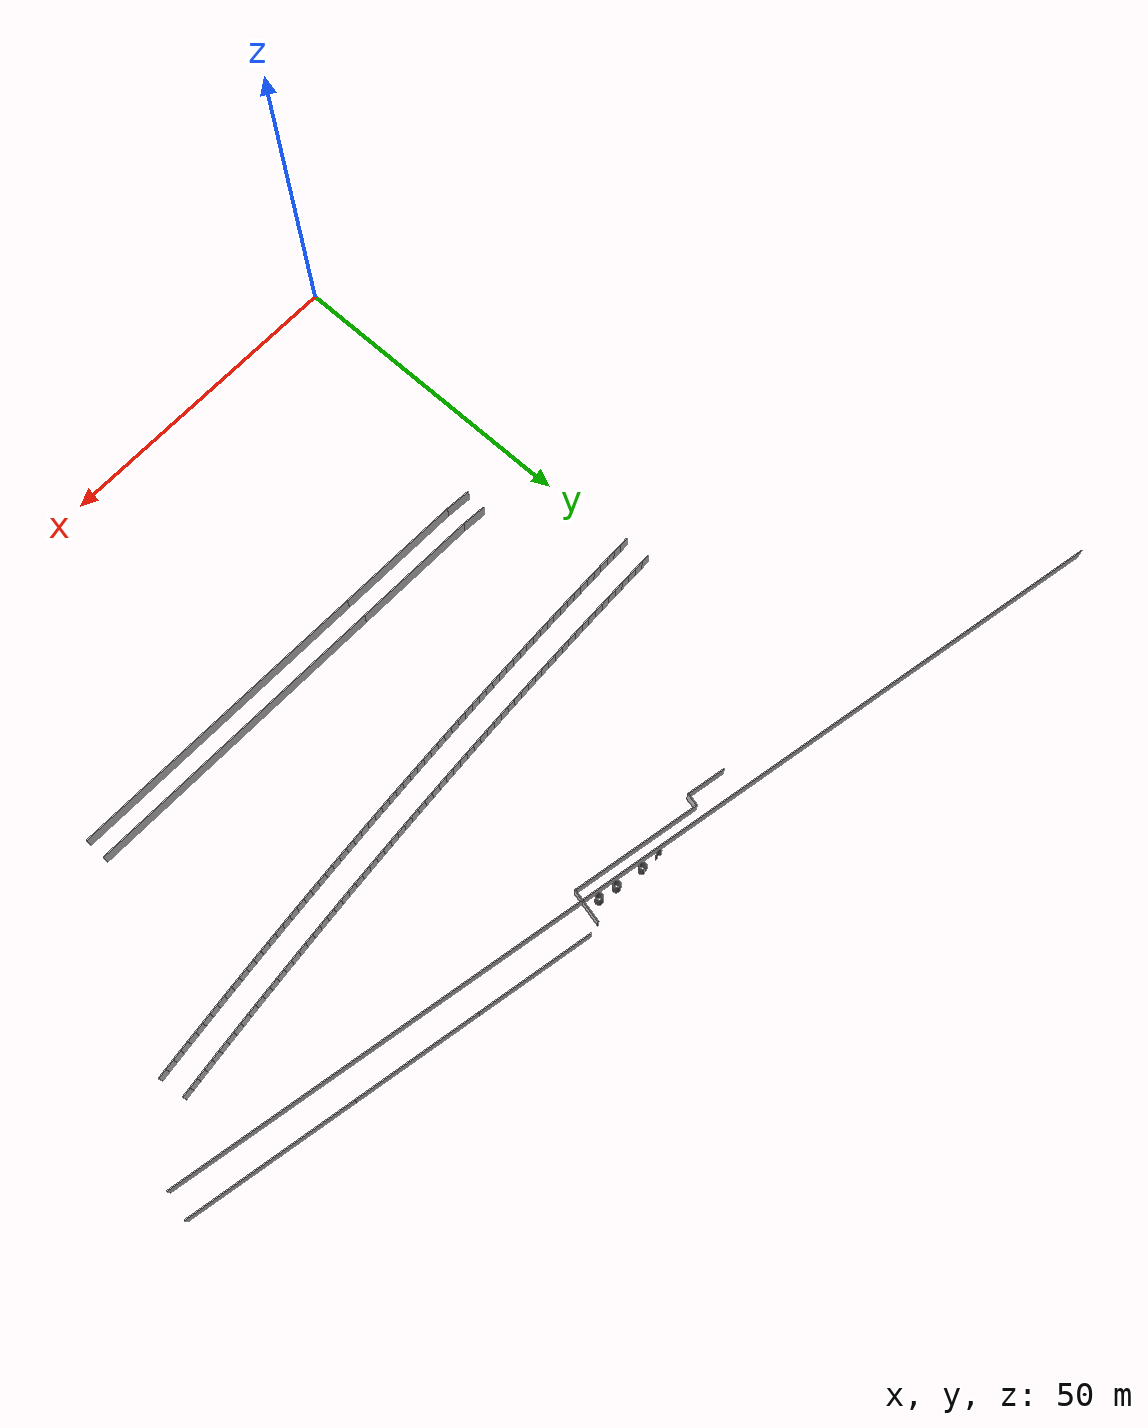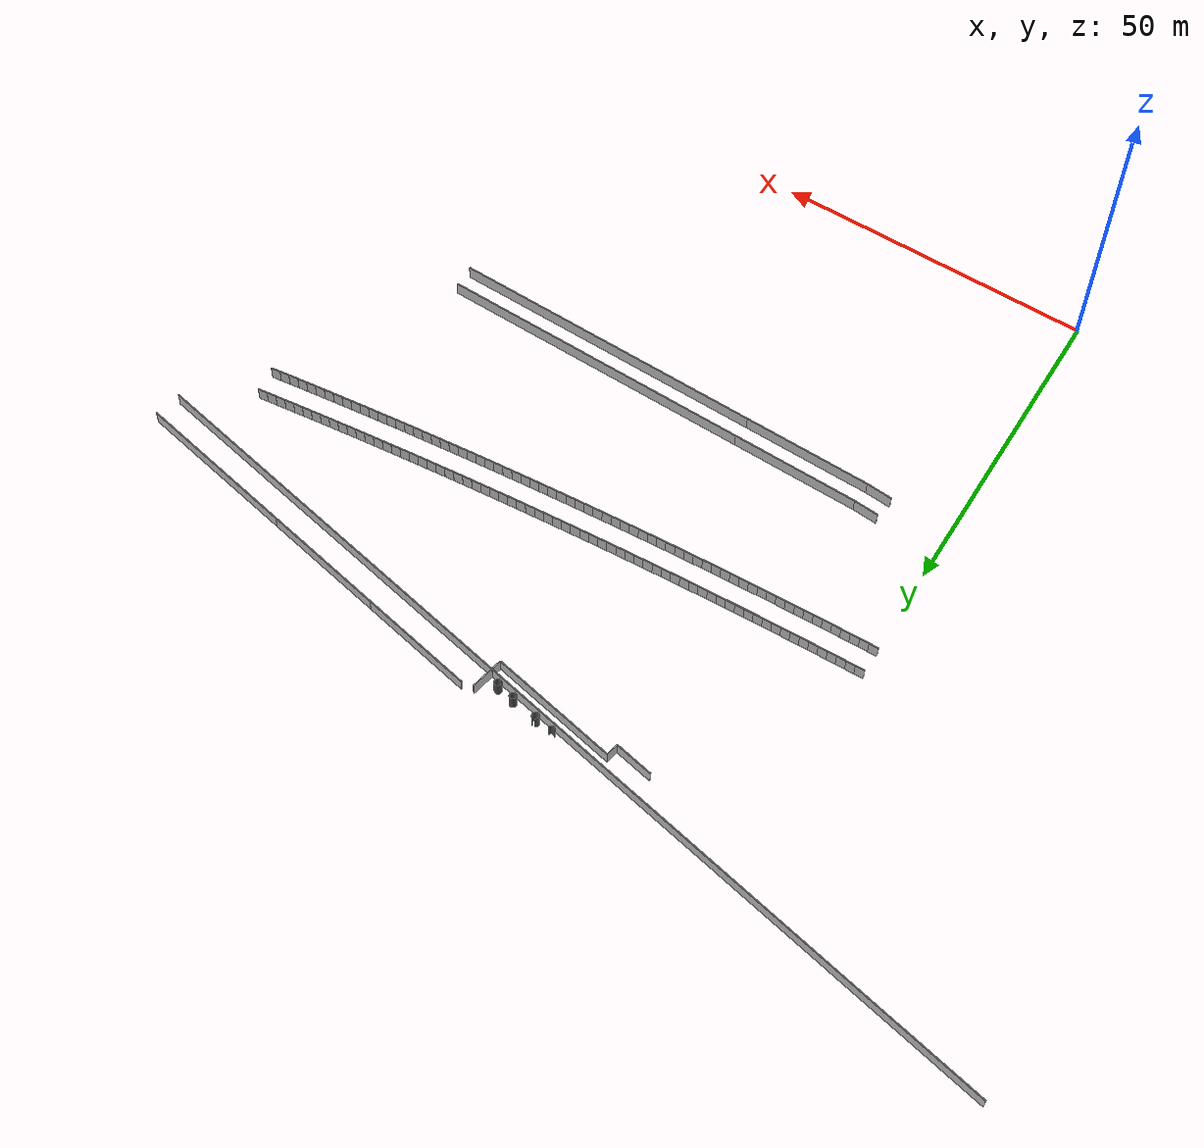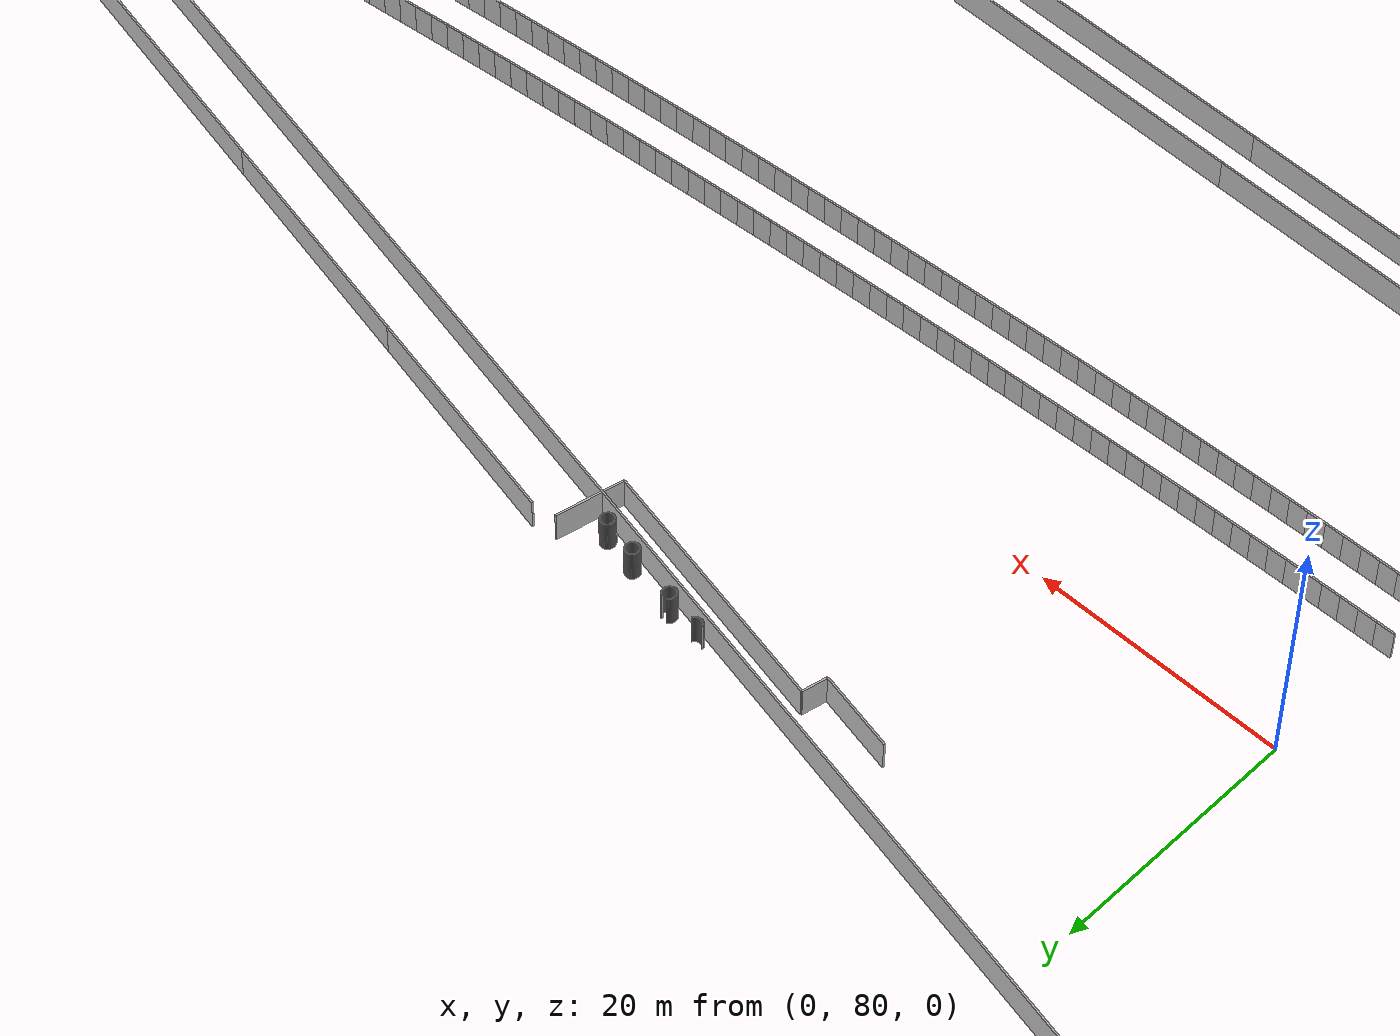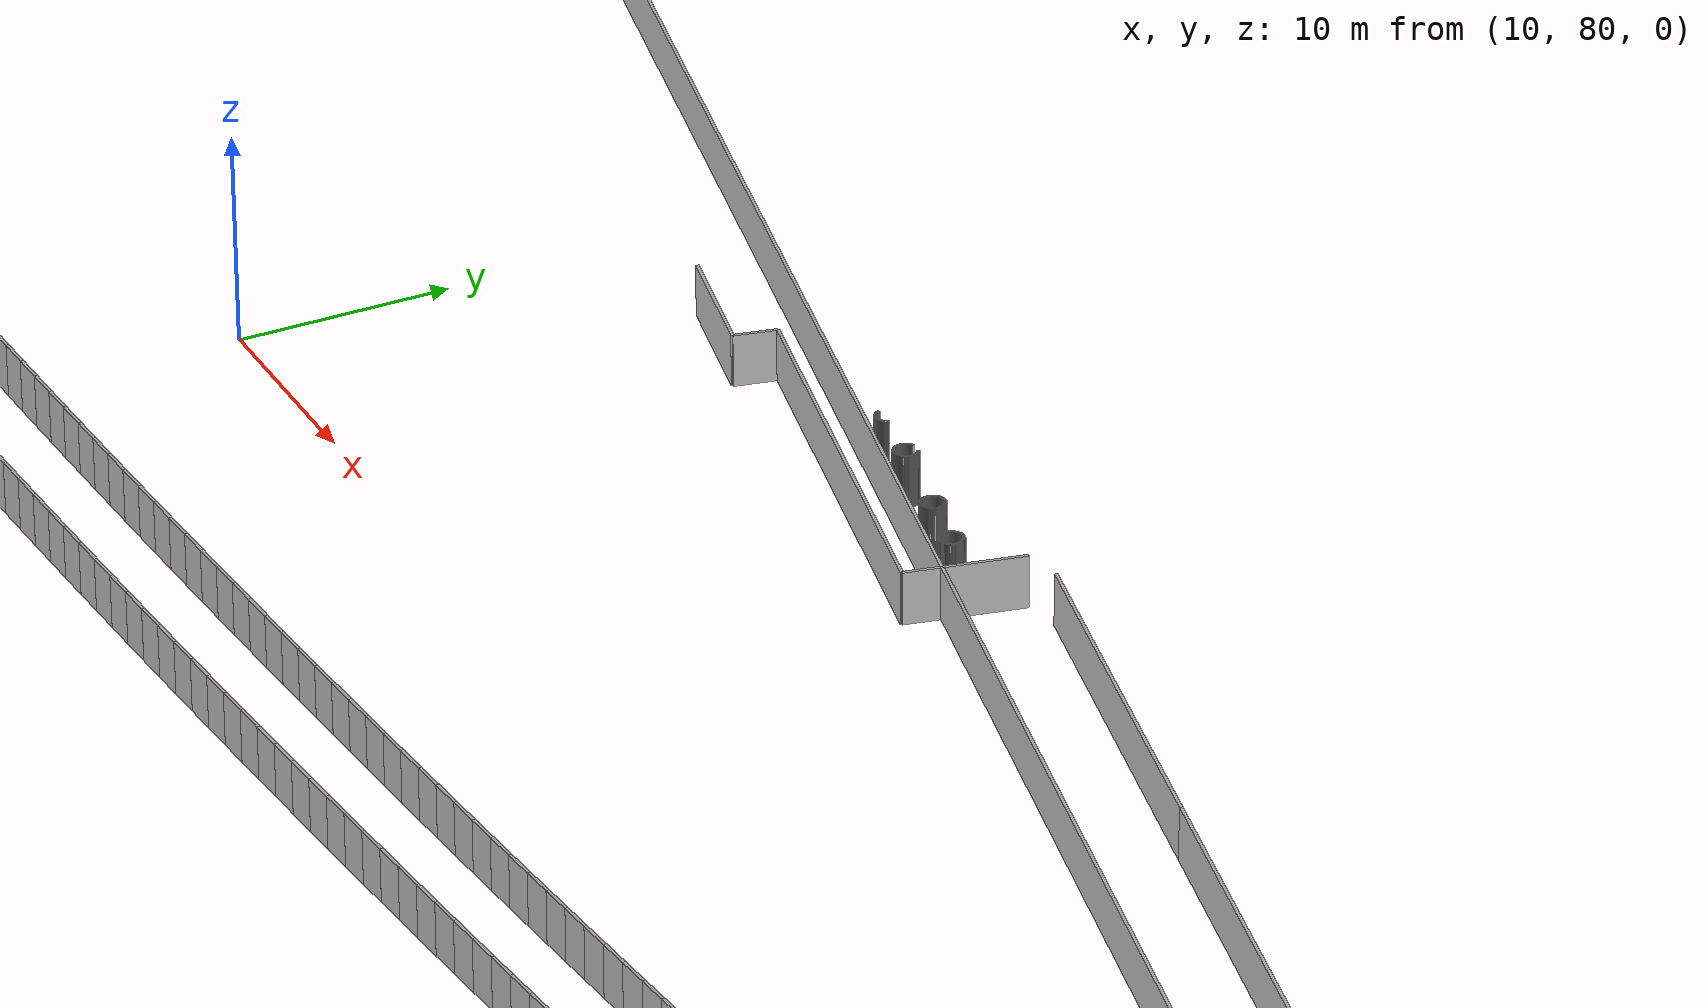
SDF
<?xml version="1.0" ?>
<sdf version="1.6">
  <model name="sps_1301">
    <pose frame="">0 0 0 0 -0 0</pose>
    <static>1</static>
    <self_collide>0</self_collide>
    <allow_auto_disable>0</allow_auto_disable>
    <link name="Wall237">
      <kinematic>0</kinematic>
      <gravity>1</gravity>
      <self_collide>0</self_collide>
      <collision name="collision">
        <geometry>
          <box>
            <size>18.5004 0.15 2.5</size>
          </box>
        </geometry>
        <pose frame="">0 0 0 0 -0 0</pose>
      </collision>
      <visual name="visual">
        <geometry>
          <box>
            <size>18.5004 0.15 2.5</size>
          </box>
        </geometry>
        <pose frame="">0 0 0 0 -0 0</pose>
        <cast_shadows>1</cast_shadows>
        <transparency>0.0</transparency>
      </visual>
      <pose frame="">56.1314 98.5066 1.25 0 0 -0.214248</pose>
    </link>
    <link name="Wall238">
      <kinematic>0</kinematic>
      <gravity>1</gravity>
      <self_collide>0</self_collide>
      <collision name="collision">
        <geometry>
          <box>
            <size>19.751 0.15 2.5</size>
          </box>
        </geometry>
        <pose frame="">0 0 0 0 -0 0</pose>
      </collision>
      <visual name="visual">
        <geometry>
          <box>
            <size>19.751 0.15 2.5</size>
          </box>
        </geometry>
        <pose frame="">0 0 0 0 -0 0</pose>
        <cast_shadows>1</cast_shadows>
        <transparency>0.0</transparency>
      </visual>
      <pose frame="">74.8198 94.4402 1.25 0 0 -0.214253</pose>
    </link>
    <link name="Wall239">
      <kinematic>0</kinematic>
      <gravity>1</gravity>
      <self_collide>0</self_collide>
      <collision name="collision">
        <geometry>
          <box>
            <size>26.0944 0.15 2.5</size>
          </box>
        </geometry>
        <pose frame="">0 0 0 0 -0 0</pose>
      </collision>
      <visual name="visual">
        <geometry>
          <box>
            <size>26.0944 0.15 2.5</size>
          </box>
        </geometry>
        <pose frame="">0 0 0 0 -0 0</pose>
        <cast_shadows>1</cast_shadows>
        <transparency>0.0</transparency>
      </visual>
      <pose frame="">97.2183 89.5664 1.25 0 0 -0.214253</pose>
    </link>
    <link name="Wall306">
      <kinematic>0</kinematic>
      <gravity>1</gravity>
      <self_collide>0</self_collide>
      <collision name="collision">
        <geometry>
          <box>
            <size>4.00867 0.15 2.5</size>
          </box>
        </geometry>
        <pose frame="">0 0 0 0 -0 0</pose>
      </collision>
      <visual name="visual">
        <geometry>
          <box>
            <size>4.00867 0.15 2.5</size>
          </box>
        </geometry>
        <pose frame="">0 0 0 0 -0 0</pose>
        <cast_shadows>1</cast_shadows>
        <transparency>0.0</transparency>
      </visual>
      <pose frame="">12.0576 45.632 1.25 0 0 -0.0807692</pose>
    </link>
    <link name="Wall461">
      <kinematic>0</kinematic>
      <gravity>1</gravity>
      <self_collide>0</self_collide>
      <collision name="collision">
        <geometry>
          <box>
            <size>50.0165 0.15 2.5</size>
          </box>
        </geometry>
        <pose frame="">0 0 0 0 -0 0</pose>
      </collision>
      <visual name="visual">
        <geometry>
          <box>
            <size>50.0165 0.15 2.5</size>
          </box>
        </geometry>
        <pose frame="">0 0 0 0 -0 0</pose>
        <cast_shadows>1</cast_shadows>
        <transparency>0.0</transparency>
      </visual>
      <pose frame="">59.4694 40.8028 1.25 0 -0 3.11591</pose>
    </link>
    <link name="Wall462">
      <kinematic>0</kinematic>
      <gravity>1</gravity>
      <self_collide>0</self_collide>
      <collision name="collision">
        <geometry>
          <box>
            <size>20.6064 0.15 2.5</size>
          </box>
        </geometry>
        <pose frame="">0 0 0 0 -0 0</pose>
      </collision>
      <visual name="visual">
        <geometry>
          <box>
            <size>20.6064 0.15 2.5</size>
          </box>
        </geometry>
        <pose frame="">0 0 0 0 -0 0</pose>
        <cast_shadows>1</cast_shadows>
        <transparency>0.0</transparency>
      </visual>
      <pose frame="">24.1696 41.7095 1.25 0 -0 3.11591</pose>
    </link>
    <link name="Wall463">
      <kinematic>0</kinematic>
      <gravity>1</gravity>
      <self_collide>0</self_collide>
      <collision name="collision">
        <geometry>
          <box>
            <size>20.4207 0.15 2.5</size>
          </box>
        </geometry>
        <pose frame="">0 0 0 0 -0 0</pose>
      </collision>
      <visual name="visual">
        <geometry>
          <box>
            <size>20.4207 0.15 2.5</size>
          </box>
        </geometry>
        <pose frame="">0 0 0 0 -0 0</pose>
        <cast_shadows>1</cast_shadows>
        <transparency>0.0</transparency>
      </visual>
      <pose frame="">24.2624 45.2081 1.25 0 0 -0.0256802</pose>
    </link>
    <link name="Wall464">
      <kinematic>0</kinematic>
      <gravity>1</gravity>
      <self_collide>0</self_collide>
      <collision name="collision">
        <geometry>
          <box>
            <size>50.0165 0.15 2.5</size>
          </box>
        </geometry>
        <pose frame="">0 0 0 0 -0 0</pose>
      </collision>
      <visual name="visual">
        <geometry>
          <box>
            <size>50.0165 0.15 2.5</size>
          </box>
        </geometry>
        <pose frame="">0 0 0 0 -0 0</pose>
        <cast_shadows>1</cast_shadows>
        <transparency>0.0</transparency>
      </visual>
      <pose frame="">59.4694 44.3038 1.25 0 0 -0.0256802</pose>
    </link>
    <link name="Wall562">
      <kinematic>0</kinematic>
      <gravity>1</gravity>
      <self_collide>0</self_collide>
      <collision name="collision">
        <geometry>
          <box>
            <size>4.19887 0.15 2.5</size>
          </box>
        </geometry>
        <pose frame="">0 0 0 0 -0 0</pose>
      </collision>
      <visual name="visual">
        <geometry>
          <box>
            <size>4.19887 0.15 2.5</size>
          </box>
        </geometry>
        <pose frame="">0 0 0 0 -0 0</pose>
        <cast_shadows>1</cast_shadows>
        <transparency>0.0</transparency>
      </visual>
      <pose frame="">11.7772 42.1435 1.25 0 -0 3.06082</pose>
    </link>
    <link name="Wall697">
      <kinematic>0</kinematic>
      <gravity>1</gravity>
      <self_collide>0</self_collide>
      <collision name="collision">
        <geometry>
          <box>
            <size>0.0454008 0.15 2.5</size>
          </box>
        </geometry>
        <pose frame="">0 0 0 0 -0 0</pose>
      </collision>
      <visual name="visual">
        <geometry>
          <box>
            <size>0.0454008 0.15 2.5</size>
          </box>
        </geometry>
        <pose frame="">0 0 0 0 -0 0</pose>
        <cast_shadows>1</cast_shadows>
        <transparency>0.0</transparency>
      </visual>
      <pose frame="">42.9055 98.3673 1.25 0 0 -0.654794</pose>
    </link>
    <link name="Wall698">
      <kinematic>0</kinematic>
      <gravity>1</gravity>
      <self_collide>0</self_collide>
      <collision name="collision">
        <geometry>
          <box>
            <size>0.0452735 0.15 2.5</size>
          </box>
        </geometry>
        <pose frame="">0 0 0 0 -0 0</pose>
      </collision>
      <visual name="visual">
        <geometry>
          <box>
            <size>0.0452735 0.15 2.5</size>
          </box>
        </geometry>
        <pose frame="">0 0 0 0 -0 0</pose>
        <cast_shadows>1</cast_shadows>
        <transparency>0.0</transparency>
      </visual>
      <pose frame="">42.9402 98.3382 1.25 0 0 -0.741533</pose>
    </link>
    <link name="Wall699">
      <kinematic>0</kinematic>
      <gravity>1</gravity>
      <self_collide>0</self_collide>
      <collision name="collision">
        <geometry>
          <box>
            <size>0.0454087 0.15 2.5</size>
          </box>
        </geometry>
        <pose frame="">0 0 0 0 -0 0</pose>
      </collision>
      <visual name="visual">
        <geometry>
          <box>
            <size>0.0454087 0.15 2.5</size>
          </box>
        </geometry>
        <pose frame="">0 0 0 0 -0 0</pose>
        <cast_shadows>1</cast_shadows>
        <transparency>0.0</transparency>
      </visual>
      <pose frame="">42.9722 98.3061 1.25 0 0 -0.831987</pose>
    </link>
    <link name="Wall700">
      <kinematic>0</kinematic>
      <gravity>1</gravity>
      <self_collide>0</self_collide>
      <collision name="collision">
        <geometry>
          <box>
            <size>0.0453637 0.15 2.5</size>
          </box>
        </geometry>
        <pose frame="">0 0 0 0 -0 0</pose>
      </collision>
      <visual name="visual">
        <geometry>
          <box>
            <size>0.0453637 0.15 2.5</size>
          </box>
        </geometry>
        <pose frame="">0 0 0 0 -0 0</pose>
        <cast_shadows>1</cast_shadows>
        <transparency>0.0</transparency>
      </visual>
      <pose frame="">43.0012 98.2713 1.25 0 0 -0.91707</pose>
    </link>
    <link name="Wall701">
      <kinematic>0</kinematic>
      <gravity>1</gravity>
      <self_collide>0</self_collide>
      <collision name="collision">
        <geometry>
          <box>
            <size>0.045342 0.15 2.5</size>
          </box>
        </geometry>
        <pose frame="">0 0 0 0 -0 0</pose>
      </collision>
      <visual name="visual">
        <geometry>
          <box>
            <size>0.045342 0.15 2.5</size>
          </box>
        </geometry>
        <pose frame="">0 0 0 0 -0 0</pose>
        <cast_shadows>1</cast_shadows>
        <transparency>0.0</transparency>
      </visual>
      <pose frame="">43.0272 98.2342 1.25 0 0 -1.00221</pose>
    </link>
    <link name="Wall702">
      <kinematic>0</kinematic>
      <gravity>1</gravity>
      <self_collide>0</self_collide>
      <collision name="collision">
        <geometry>
          <box>
            <size>0.0453724 0.15 2.5</size>
          </box>
        </geometry>
        <pose frame="">0 0 0 0 -0 0</pose>
      </collision>
      <visual name="visual">
        <geometry>
          <box>
            <size>0.0453724 0.15 2.5</size>
          </box>
        </geometry>
        <pose frame="">0 0 0 0 -0 0</pose>
        <cast_shadows>1</cast_shadows>
        <transparency>0.0</transparency>
      </visual>
      <pose frame="">43.0499 98.195 1.25 0 0 -1.0897</pose>
    </link>
    <link name="Wall703">
      <kinematic>0</kinematic>
      <gravity>1</gravity>
      <self_collide>0</self_collide>
      <collision name="collision">
        <geometry>
          <box>
            <size>0.0453827 0.15 2.5</size>
          </box>
        </geometry>
        <pose frame="">0 0 0 0 -0 0</pose>
      </collision>
      <visual name="visual">
        <geometry>
          <box>
            <size>0.0453827 0.15 2.5</size>
          </box>
        </geometry>
        <pose frame="">0 0 0 0 -0 0</pose>
        <cast_shadows>1</cast_shadows>
        <transparency>0.0</transparency>
      </visual>
      <pose frame="">43.0691 98.1539 1.25 0 0 -1.1818</pose>
    </link>
    <link name="Wall704">
      <kinematic>0</kinematic>
      <gravity>1</gravity>
      <self_collide>0</self_collide>
      <collision name="collision">
        <geometry>
          <box>
            <size>0.0453611 0.15 2.5</size>
          </box>
        </geometry>
        <pose frame="">0 0 0 0 -0 0</pose>
      </collision>
      <visual name="visual">
        <geometry>
          <box>
            <size>0.0453611 0.15 2.5</size>
          </box>
        </geometry>
        <pose frame="">0 0 0 0 -0 0</pose>
        <cast_shadows>1</cast_shadows>
        <transparency>0.0</transparency>
      </visual>
      <pose frame="">43.0846 98.1113 1.25 0 0 -1.26181</pose>
    </link>
    <link name="Wall705">
      <kinematic>0</kinematic>
      <gravity>1</gravity>
      <self_collide>0</self_collide>
      <collision name="collision">
        <geometry>
          <box>
            <size>0.0452165 0.15 2.5</size>
          </box>
        </geometry>
        <pose frame="">0 0 0 0 -0 0</pose>
      </collision>
      <visual name="visual">
        <geometry>
          <box>
            <size>0.0452165 0.15 2.5</size>
          </box>
        </geometry>
        <pose frame="">0 0 0 0 -0 0</pose>
        <cast_shadows>1</cast_shadows>
        <transparency>0.0</transparency>
      </visual>
      <pose frame="">43.0962 98.0676 1.25 0 0 -1.35725</pose>
    </link>
    <link name="Wall706">
      <kinematic>0</kinematic>
      <gravity>1</gravity>
      <self_collide>0</self_collide>
      <collision name="collision">
        <geometry>
          <box>
            <size>0.0453869 0.15 2.5</size>
          </box>
        </geometry>
        <pose frame="">0 0 0 0 -0 0</pose>
      </collision>
      <visual name="visual">
        <geometry>
          <box>
            <size>0.0453869 0.15 2.5</size>
          </box>
        </geometry>
        <pose frame="">0 0 0 0 -0 0</pose>
        <cast_shadows>1</cast_shadows>
        <transparency>0.0</transparency>
      </visual>
      <pose frame="">43.1041 98.023 1.25 0 0 -1.43727</pose>
    </link>
    <link name="Wall707">
      <kinematic>0</kinematic>
      <gravity>1</gravity>
      <self_collide>0</self_collide>
      <collision name="collision">
        <geometry>
          <box>
            <size>0.0454521 0.15 2.5</size>
          </box>
        </geometry>
        <pose frame="">0 0 0 0 -0 0</pose>
      </collision>
      <visual name="visual">
        <geometry>
          <box>
            <size>0.0454521 0.15 2.5</size>
          </box>
        </geometry>
        <pose frame="">0 0 0 0 -0 0</pose>
        <cast_shadows>1</cast_shadows>
        <transparency>0.0</transparency>
      </visual>
      <pose frame="">43.1081 97.9778 1.25 0 0 -1.52781</pose>
    </link>
    <link name="Wall708">
      <kinematic>0</kinematic>
      <gravity>1</gravity>
      <self_collide>0</self_collide>
      <collision name="collision">
        <geometry>
          <box>
            <size>0.0452692 0.15 2.5</size>
          </box>
        </geometry>
        <pose frame="">0 0 0 0 -0 0</pose>
      </collision>
      <visual name="visual">
        <geometry>
          <box>
            <size>0.0452692 0.15 2.5</size>
          </box>
        </geometry>
        <pose frame="">0 0 0 0 -0 0</pose>
        <cast_shadows>1</cast_shadows>
        <transparency>0.0</transparency>
      </visual>
      <pose frame="">43.1081 97.9325 1.25 0 0 -1.61395</pose>
    </link>
    <link name="Wall709">
      <kinematic>0</kinematic>
      <gravity>1</gravity>
      <self_collide>0</self_collide>
      <collision name="collision">
        <geometry>
          <box>
            <size>0.0453869 0.15 2.5</size>
          </box>
        </geometry>
        <pose frame="">0 0 0 0 -0 0</pose>
      </collision>
      <visual name="visual">
        <geometry>
          <box>
            <size>0.0453869 0.15 2.5</size>
          </box>
        </geometry>
        <pose frame="">0 0 0 0 -0 0</pose>
        <cast_shadows>1</cast_shadows>
        <transparency>0.0</transparency>
      </visual>
      <pose frame="">43.1041 97.8874 1.25 0 0 -1.70433</pose>
    </link>
    <link name="Wall710">
      <kinematic>0</kinematic>
      <gravity>1</gravity>
      <self_collide>0</self_collide>
      <collision name="collision">
        <geometry>
          <box>
            <size>0.0454345 0.15 2.5</size>
          </box>
        </geometry>
        <pose frame="">0 0 0 0 -0 0</pose>
      </collision>
      <visual name="visual">
        <geometry>
          <box>
            <size>0.0454345 0.15 2.5</size>
          </box>
        </geometry>
        <pose frame="">0 0 0 0 -0 0</pose>
        <cast_shadows>1</cast_shadows>
        <transparency>0.0</transparency>
      </visual>
      <pose frame="">43.0962 97.8427 1.25 0 0 -1.78743</pose>
    </link>
    <link name="Wall711">
      <kinematic>0</kinematic>
      <gravity>1</gravity>
      <self_collide>0</self_collide>
      <collision name="collision">
        <geometry>
          <box>
            <size>0.0453057 0.15 2.5</size>
          </box>
        </geometry>
        <pose frame="">0 0 0 0 -0 0</pose>
      </collision>
      <visual name="visual">
        <geometry>
          <box>
            <size>0.0453057 0.15 2.5</size>
          </box>
        </geometry>
        <pose frame="">0 0 0 0 -0 0</pose>
        <cast_shadows>1</cast_shadows>
        <transparency>0.0</transparency>
      </visual>
      <pose frame="">43.0845 97.7989 1.25 0 0 -1.87593</pose>
    </link>
    <link name="Wall712">
      <kinematic>0</kinematic>
      <gravity>1</gravity>
      <self_collide>0</self_collide>
      <collision name="collision">
        <geometry>
          <box>
            <size>0.0454525 0.15 2.5</size>
          </box>
        </geometry>
        <pose frame="">0 0 0 0 -0 0</pose>
      </collision>
      <visual name="visual">
        <geometry>
          <box>
            <size>0.0454525 0.15 2.5</size>
          </box>
        </geometry>
        <pose frame="">0 0 0 0 -0 0</pose>
        <cast_shadows>1</cast_shadows>
        <transparency>0.0</transparency>
      </visual>
      <pose frame="">43.069 97.7563 1.25 0 0 -1.96352</pose>
    </link>
    <link name="Wall713">
      <kinematic>0</kinematic>
      <gravity>1</gravity>
      <self_collide>0</self_collide>
      <collision name="collision">
        <geometry>
          <box>
            <size>0.0453724 0.15 2.5</size>
          </box>
        </geometry>
        <pose frame="">0 0 0 0 -0 0</pose>
      </collision>
      <visual name="visual">
        <geometry>
          <box>
            <size>0.0453724 0.15 2.5</size>
          </box>
        </geometry>
        <pose frame="">0 0 0 0 -0 0</pose>
        <cast_shadows>1</cast_shadows>
        <transparency>0.0</transparency>
      </visual>
      <pose frame="">43.0498 97.7152 1.25 0 0 -2.05189</pose>
    </link>
    <link name="Wall714">
      <kinematic>0</kinematic>
      <gravity>1</gravity>
      <self_collide>0</self_collide>
      <collision name="collision">
        <geometry>
          <box>
            <size>0.045342 0.15 2.5</size>
          </box>
        </geometry>
        <pose frame="">0 0 0 0 -0 0</pose>
      </collision>
      <visual name="visual">
        <geometry>
          <box>
            <size>0.045342 0.15 2.5</size>
          </box>
        </geometry>
        <pose frame="">0 0 0 0 -0 0</pose>
        <cast_shadows>1</cast_shadows>
        <transparency>0.0</transparency>
      </visual>
      <pose frame="">43.0271 97.676 1.25 0 0 -2.13938</pose>
    </link>
    <link name="Wall715">
      <kinematic>0</kinematic>
      <gravity>1</gravity>
      <self_collide>0</self_collide>
      <collision name="collision">
        <geometry>
          <box>
            <size>0.0453637 0.15 2.5</size>
          </box>
        </geometry>
        <pose frame="">0 0 0 0 -0 0</pose>
      </collision>
      <visual name="visual">
        <geometry>
          <box>
            <size>0.0453637 0.15 2.5</size>
          </box>
        </geometry>
        <pose frame="">0 0 0 0 -0 0</pose>
        <cast_shadows>1</cast_shadows>
        <transparency>0.0</transparency>
      </visual>
      <pose frame="">43.0011 97.6389 1.25 0 0 -2.22452</pose>
    </link>
    <link name="Wall716">
      <kinematic>0</kinematic>
      <gravity>1</gravity>
      <self_collide>0</self_collide>
      <collision name="collision">
        <geometry>
          <box>
            <size>0.0453148 0.15 2.5</size>
          </box>
        </geometry>
        <pose frame="">0 0 0 0 -0 0</pose>
      </collision>
      <visual name="visual">
        <geometry>
          <box>
            <size>0.0453148 0.15 2.5</size>
          </box>
        </geometry>
        <pose frame="">0 0 0 0 -0 0</pose>
        <cast_shadows>1</cast_shadows>
        <transparency>0.0</transparency>
      </visual>
      <pose frame="">42.9719 97.6042 1.25 0 0 -2.31332</pose>
    </link>
    <link name="Wall717">
      <kinematic>0</kinematic>
      <gravity>1</gravity>
      <self_collide>0</self_collide>
      <collision name="collision">
        <geometry>
          <box>
            <size>0.0453974 0.15 2.5</size>
          </box>
        </geometry>
        <pose frame="">0 0 0 0 -0 0</pose>
      </collision>
      <visual name="visual">
        <geometry>
          <box>
            <size>0.0453974 0.15 2.5</size>
          </box>
        </geometry>
        <pose frame="">0 0 0 0 -0 0</pose>
        <cast_shadows>1</cast_shadows>
        <transparency>0.0</transparency>
      </visual>
      <pose frame="">42.9399 97.5721 1.25 0 0 -2.39709</pose>
    </link>
    <link name="Wall718">
      <kinematic>0</kinematic>
      <gravity>1</gravity>
      <self_collide>0</self_collide>
      <collision name="collision">
        <geometry>
          <box>
            <size>0.0454008 0.15 2.5</size>
          </box>
        </geometry>
        <pose frame="">0 0 0 0 -0 0</pose>
      </collision>
      <visual name="visual">
        <geometry>
          <box>
            <size>0.0454008 0.15 2.5</size>
          </box>
        </geometry>
        <pose frame="">0 0 0 0 -0 0</pose>
        <cast_shadows>1</cast_shadows>
        <transparency>0.0</transparency>
      </visual>
      <pose frame="">42.9052 97.5429 1.25 0 0 -2.4868</pose>
    </link>
    <link name="Wall719">
      <kinematic>0</kinematic>
      <gravity>1</gravity>
      <self_collide>0</self_collide>
      <collision name="collision">
        <geometry>
          <box>
            <size>0.0453659 0.15 2.5</size>
          </box>
        </geometry>
        <pose frame="">0 0 0 0 -0 0</pose>
      </collision>
      <visual name="visual">
        <geometry>
          <box>
            <size>0.0453659 0.15 2.5</size>
          </box>
        </geometry>
        <pose frame="">0 0 0 0 -0 0</pose>
        <cast_shadows>1</cast_shadows>
        <transparency>0.0</transparency>
      </visual>
      <pose frame="">42.868 97.517 1.25 0 0 -2.57971</pose>
    </link>
    <link name="Wall720">
      <kinematic>0</kinematic>
      <gravity>1</gravity>
      <self_collide>0</self_collide>
      <collision name="collision">
        <geometry>
          <box>
            <size>0.0453183 0.15 2.5</size>
          </box>
        </geometry>
        <pose frame="">0 0 0 0 -0 0</pose>
      </collision>
      <visual name="visual">
        <geometry>
          <box>
            <size>0.0453183 0.15 2.5</size>
          </box>
        </geometry>
        <pose frame="">0 0 0 0 -0 0</pose>
        <cast_shadows>1</cast_shadows>
        <transparency>0.0</transparency>
      </visual>
      <pose frame="">42.8288 97.4944 1.25 0 0 -2.65987</pose>
    </link>
    <link name="Wall721">
      <kinematic>0</kinematic>
      <gravity>1</gravity>
      <self_collide>0</self_collide>
      <collision name="collision">
        <geometry>
          <box>
            <size>0.0454525 0.15 2.5</size>
          </box>
        </geometry>
        <pose frame="">0 0 0 0 -0 0</pose>
      </collision>
      <visual name="visual">
        <geometry>
          <box>
            <size>0.0454525 0.15 2.5</size>
          </box>
        </geometry>
        <pose frame="">0 0 0 0 -0 0</pose>
        <cast_shadows>1</cast_shadows>
        <transparency>0.0</transparency>
      </visual>
      <pose frame="">42.7877 97.4752 1.25 0 0 -2.74887</pose>
    </link>
    <link name="Wall722">
      <kinematic>0</kinematic>
      <gravity>1</gravity>
      <self_collide>0</self_collide>
      <collision name="collision">
        <geometry>
          <box>
            <size>0.0453057 0.15 2.5</size>
          </box>
        </geometry>
        <pose frame="">0 0 0 0 -0 0</pose>
      </collision>
      <visual name="visual">
        <geometry>
          <box>
            <size>0.0453057 0.15 2.5</size>
          </box>
        </geometry>
        <pose frame="">0 0 0 0 -0 0</pose>
        <cast_shadows>1</cast_shadows>
        <transparency>0.0</transparency>
      </visual>
      <pose frame="">42.7451 97.4597 1.25 0 0 -2.83646</pose>
    </link>
    <link name="Wall723">
      <kinematic>0</kinematic>
      <gravity>1</gravity>
      <self_collide>0</self_collide>
      <collision name="collision">
        <geometry>
          <box>
            <size>0.0452689 0.15 2.5</size>
          </box>
        </geometry>
        <pose frame="">0 0 0 0 -0 0</pose>
      </collision>
      <visual name="visual">
        <geometry>
          <box>
            <size>0.0452689 0.15 2.5</size>
          </box>
        </geometry>
        <pose frame="">0 0 0 0 -0 0</pose>
        <cast_shadows>1</cast_shadows>
        <transparency>0.0</transparency>
      </visual>
      <pose frame="">42.7014 97.448 1.25 0 0 -2.92278</pose>
    </link>
    <link name="Wall724">
      <kinematic>0</kinematic>
      <gravity>1</gravity>
      <self_collide>0</self_collide>
      <collision name="collision">
        <geometry>
          <box>
            <size>0.0454156 0.15 2.5</size>
          </box>
        </geometry>
        <pose frame="">0 0 0 0 -0 0</pose>
      </collision>
      <visual name="visual">
        <geometry>
          <box>
            <size>0.0454156 0.15 2.5</size>
          </box>
        </geometry>
        <pose frame="">0 0 0 0 -0 0</pose>
        <cast_shadows>1</cast_shadows>
        <transparency>0.0</transparency>
      </visual>
      <pose frame="">42.6568 97.4402 1.25 0 0 -3.01357</pose>
    </link>
    <link name="Wall725">
      <kinematic>0</kinematic>
      <gravity>1</gravity>
      <self_collide>0</self_collide>
      <collision name="collision">
        <geometry>
          <box>
            <size>0.0454521 0.15 2.5</size>
          </box>
        </geometry>
        <pose frame="">0 0 0 0 -0 0</pose>
      </collision>
      <visual name="visual">
        <geometry>
          <box>
            <size>0.0454521 0.15 2.5</size>
          </box>
        </geometry>
        <pose frame="">0 0 0 0 -0 0</pose>
        <cast_shadows>1</cast_shadows>
        <transparency>0.0</transparency>
      </visual>
      <pose frame="">42.6115 97.4363 1.25 0 0 -3.09861</pose>
    </link>
    <link name="Wall726">
      <kinematic>0</kinematic>
      <gravity>1</gravity>
      <self_collide>0</self_collide>
      <collision name="collision">
        <geometry>
          <box>
            <size>0.0452082 0.15 2.5</size>
          </box>
        </geometry>
        <pose frame="">0 0 0 0 -0 0</pose>
      </collision>
      <visual name="visual">
        <geometry>
          <box>
            <size>0.0452082 0.15 2.5</size>
          </box>
        </geometry>
        <pose frame="">0 0 0 0 -0 0</pose>
        <cast_shadows>1</cast_shadows>
        <transparency>0.0</transparency>
      </visual>
      <pose frame="">42.5662 97.4363 1.25 0 -0 3.09838</pose>
    </link>
    <link name="Wall727">
      <kinematic>0</kinematic>
      <gravity>1</gravity>
      <self_collide>0</self_collide>
      <collision name="collision">
        <geometry>
          <box>
            <size>0.0453551 0.15 2.5</size>
          </box>
        </geometry>
        <pose frame="">0 0 0 0 -0 0</pose>
      </collision>
      <visual name="visual">
        <geometry>
          <box>
            <size>0.0453551 0.15 2.5</size>
          </box>
        </geometry>
        <pose frame="">0 0 0 0 -0 0</pose>
        <cast_shadows>1</cast_shadows>
        <transparency>0.0</transparency>
      </visual>
      <pose frame="">42.5212 97.4402 1.25 0 -0 3.0134</pose>
    </link>
    <link name="Wall728">
      <kinematic>0</kinematic>
      <gravity>1</gravity>
      <self_collide>0</self_collide>
      <collision name="collision">
        <geometry>
          <box>
            <size>0.0455471 0.15 2.5</size>
          </box>
        </geometry>
        <pose frame="">0 0 0 0 -0 0</pose>
      </collision>
      <visual name="visual">
        <geometry>
          <box>
            <size>0.0455471 0.15 2.5</size>
          </box>
        </geometry>
        <pose frame="">0 0 0 0 -0 0</pose>
        <cast_shadows>1</cast_shadows>
        <transparency>0.0</transparency>
      </visual>
      <pose frame="">42.4765 97.4481 1.25 0 -0 2.92002</pose>
    </link>
    <link name="Wall729">
      <kinematic>0</kinematic>
      <gravity>1</gravity>
      <self_collide>0</self_collide>
      <collision name="collision">
        <geometry>
          <box>
            <size>0.0453057 0.15 2.5</size>
          </box>
        </geometry>
        <pose frame="">0 0 0 0 -0 0</pose>
      </collision>
      <visual name="visual">
        <geometry>
          <box>
            <size>0.0453057 0.15 2.5</size>
          </box>
        </geometry>
        <pose frame="">0 0 0 0 -0 0</pose>
        <cast_shadows>1</cast_shadows>
        <transparency>0.0</transparency>
      </visual>
      <pose frame="">42.4326 97.4599 1.25 0 -0 2.83646</pose>
    </link>
    <link name="Wall730">
      <kinematic>0</kinematic>
      <gravity>1</gravity>
      <self_collide>0</self_collide>
      <collision name="collision">
        <geometry>
          <box>
            <size>0.0454525 0.15 2.5</size>
          </box>
        </geometry>
        <pose frame="">0 0 0 0 -0 0</pose>
      </collision>
      <visual name="visual">
        <geometry>
          <box>
            <size>0.0454525 0.15 2.5</size>
          </box>
        </geometry>
        <pose frame="">0 0 0 0 -0 0</pose>
        <cast_shadows>1</cast_shadows>
        <transparency>0.0</transparency>
      </visual>
      <pose frame="">42.39 97.4754 1.25 0 -0 2.74887</pose>
    </link>
    <link name="Wall731">
      <kinematic>0</kinematic>
      <gravity>1</gravity>
      <self_collide>0</self_collide>
      <collision name="collision">
        <geometry>
          <box>
            <size>0.0452338 0.15 2.5</size>
          </box>
        </geometry>
        <pose frame="">0 0 0 0 -0 0</pose>
      </collision>
      <visual name="visual">
        <geometry>
          <box>
            <size>0.0452338 0.15 2.5</size>
          </box>
        </geometry>
        <pose frame="">0 0 0 0 -0 0</pose>
        <cast_shadows>1</cast_shadows>
        <transparency>0.0</transparency>
      </visual>
      <pose frame="">42.349 97.4945 1.25 0 -0 2.66346</pose>
    </link>
    <link name="Wall732">
      <kinematic>0</kinematic>
      <gravity>1</gravity>
      <self_collide>0</self_collide>
      <collision name="collision">
        <geometry>
          <box>
            <size>0.045342 0.15 2.5</size>
          </box>
        </geometry>
        <pose frame="">0 0 0 0 -0 0</pose>
      </collision>
      <visual name="visual">
        <geometry>
          <box>
            <size>0.045342 0.15 2.5</size>
          </box>
        </geometry>
        <pose frame="">0 0 0 0 -0 0</pose>
        <cast_shadows>1</cast_shadows>
        <transparency>0.0</transparency>
      </visual>
      <pose frame="">42.3098 97.5171 1.25 0 -0 2.57301</pose>
    </link>
    <link name="Wall733">
      <kinematic>0</kinematic>
      <gravity>1</gravity>
      <self_collide>0</self_collide>
      <collision name="collision">
        <geometry>
          <box>
            <size>0.0454753 0.15 2.5</size>
          </box>
        </geometry>
        <pose frame="">0 0 0 0 -0 0</pose>
      </collision>
      <visual name="visual">
        <geometry>
          <box>
            <size>0.0454753 0.15 2.5</size>
          </box>
        </geometry>
        <pose frame="">0 0 0 0 -0 0</pose>
        <cast_shadows>1</cast_shadows>
        <transparency>0.0</transparency>
      </visual>
      <pose frame="">42.2727 97.5432 1.25 0 -0 2.48467</pose>
    </link>
    <link name="Wall734">
      <kinematic>0</kinematic>
      <gravity>1</gravity>
      <self_collide>0</self_collide>
      <collision name="collision">
        <geometry>
          <box>
            <size>0.0453148 0.15 2.5</size>
          </box>
        </geometry>
        <pose frame="">0 0 0 0 -0 0</pose>
      </collision>
      <visual name="visual">
        <geometry>
          <box>
            <size>0.0453148 0.15 2.5</size>
          </box>
        </geometry>
        <pose frame="">0 0 0 0 -0 0</pose>
        <cast_shadows>1</cast_shadows>
        <transparency>0.0</transparency>
      </visual>
      <pose frame="">42.238 97.5724 1.25 0 -0 2.39907</pose>
    </link>
    <link name="Wall735">
      <kinematic>0</kinematic>
      <gravity>1</gravity>
      <self_collide>0</self_collide>
      <collision name="collision">
        <geometry>
          <box>
            <size>0.0453148 0.15 2.5</size>
          </box>
        </geometry>
        <pose frame="">0 0 0 0 -0 0</pose>
      </collision>
      <visual name="visual">
        <geometry>
          <box>
            <size>0.0453148 0.15 2.5</size>
          </box>
        </geometry>
        <pose frame="">0 0 0 0 -0 0</pose>
        <cast_shadows>1</cast_shadows>
        <transparency>0.0</transparency>
      </visual>
      <pose frame="">42.206 97.6044 1.25 0 -0 2.31332</pose>
    </link>
    <link name="Wall736">
      <kinematic>0</kinematic>
      <gravity>1</gravity>
      <self_collide>0</self_collide>
      <collision name="collision">
        <geometry>
          <box>
            <size>0.0453637 0.15 2.5</size>
          </box>
        </geometry>
        <pose frame="">0 0 0 0 -0 0</pose>
      </collision>
      <visual name="visual">
        <geometry>
          <box>
            <size>0.0453637 0.15 2.5</size>
          </box>
        </geometry>
        <pose frame="">0 0 0 0 -0 0</pose>
        <cast_shadows>1</cast_shadows>
        <transparency>0.0</transparency>
      </visual>
      <pose frame="">42.1768 97.6391 1.25 0 -0 2.22452</pose>
    </link>
    <link name="Wall737">
      <kinematic>0</kinematic>
      <gravity>1</gravity>
      <self_collide>0</self_collide>
      <collision name="collision">
        <geometry>
          <box>
            <size>0.0452906 0.15 2.5</size>
          </box>
        </geometry>
        <pose frame="">0 0 0 0 -0 0</pose>
      </collision>
      <visual name="visual">
        <geometry>
          <box>
            <size>0.0452906 0.15 2.5</size>
          </box>
        </geometry>
        <pose frame="">0 0 0 0 -0 0</pose>
        <cast_shadows>1</cast_shadows>
        <transparency>0.0</transparency>
      </visual>
      <pose frame="">42.1508 97.6762 1.25 0 -0 2.14011</pose>
    </link>
    <link name="Wall738">
      <kinematic>0</kinematic>
      <gravity>1</gravity>
      <self_collide>0</self_collide>
      <collision name="collision">
        <geometry>
          <box>
            <size>0.0455348 0.15 2.5</size>
          </box>
        </geometry>
        <pose frame="">0 0 0 0 -0 0</pose>
      </collision>
      <visual name="visual">
        <geometry>
          <box>
            <size>0.0455348 0.15 2.5</size>
          </box>
        </geometry>
        <pose frame="">0 0 0 0 -0 0</pose>
        <cast_shadows>1</cast_shadows>
        <transparency>0.0</transparency>
      </visual>
      <pose frame="">42.1281 97.7155 1.25 0 -0 2.05003</pose>
    </link>
    <link name="Wall739">
      <kinematic>0</kinematic>
      <gravity>1</gravity>
      <self_collide>0</self_collide>
      <collision name="collision">
        <geometry>
          <box>
            <size>0.0452834 0.15 2.5</size>
          </box>
        </geometry>
        <pose frame="">0 0 0 0 -0 0</pose>
      </collision>
      <visual name="visual">
        <geometry>
          <box>
            <size>0.0452834 0.15 2.5</size>
          </box>
        </geometry>
        <pose frame="">0 0 0 0 -0 0</pose>
        <cast_shadows>1</cast_shadows>
        <transparency>0.0</transparency>
      </visual>
      <pose frame="">42.1089 97.7566 1.25 0 -0 1.96507</pose>
    </link>
    <link name="Wall740">
      <kinematic>0</kinematic>
      <gravity>1</gravity>
      <self_collide>0</self_collide>
      <collision name="collision">
        <geometry>
          <box>
            <size>0.0454804 0.15 2.5</size>
          </box>
        </geometry>
        <pose frame="">0 0 0 0 -0 0</pose>
      </collision>
      <visual name="visual">
        <geometry>
          <box>
            <size>0.0454804 0.15 2.5</size>
          </box>
        </geometry>
        <pose frame="">0 0 0 0 -0 0</pose>
        <cast_shadows>1</cast_shadows>
        <transparency>0.0</transparency>
      </visual>
      <pose frame="">42.0934 97.7992 1.25 0 -0 1.87472</pose>
    </link>
    <link name="Wall741">
      <kinematic>0</kinematic>
      <gravity>1</gravity>
      <self_collide>0</self_collide>
      <collision name="collision">
        <geometry>
          <box>
            <size>0.0452557 0.15 2.5</size>
          </box>
        </geometry>
        <pose frame="">0 0 0 0 -0 0</pose>
      </collision>
      <visual name="visual">
        <geometry>
          <box>
            <size>0.0452557 0.15 2.5</size>
          </box>
        </geometry>
        <pose frame="">0 0 0 0 -0 0</pose>
        <cast_shadows>1</cast_shadows>
        <transparency>0.0</transparency>
      </visual>
      <pose frame="">42.0817 97.843 1.25 0 -0 1.78829</pose>
    </link>
    <link name="Wall742">
      <kinematic>0</kinematic>
      <gravity>1</gravity>
      <self_collide>0</self_collide>
      <collision name="collision">
        <geometry>
          <box>
            <size>0.0454156 0.15 2.5</size>
          </box>
        </geometry>
        <pose frame="">0 0 0 0 -0 0</pose>
      </collision>
      <visual name="visual">
        <geometry>
          <box>
            <size>0.0454156 0.15 2.5</size>
          </box>
        </geometry>
        <pose frame="">0 0 0 0 -0 0</pose>
        <cast_shadows>1</cast_shadows>
        <transparency>0.0</transparency>
      </visual>
      <pose frame="">42.074 97.8876 1.25 0 -0 1.69882</pose>
    </link>
    <link name="Wall743">
      <kinematic>0</kinematic>
      <gravity>1</gravity>
      <self_collide>0</self_collide>
      <collision name="collision">
        <geometry>
          <box>
            <size>0.0452109 0.15 2.5</size>
          </box>
        </geometry>
        <pose frame="">0 0 0 0 -0 0</pose>
      </collision>
      <visual name="visual">
        <geometry>
          <box>
            <size>0.0452109 0.15 2.5</size>
          </box>
        </geometry>
        <pose frame="">0 0 0 0 -0 0</pose>
        <cast_shadows>1</cast_shadows>
        <transparency>0.0</transparency>
      </visual>
      <pose frame="">42.0701 97.9327 1.25 0 -0 1.61536</pose>
    </link>
    <link name="Wall744">
      <kinematic>0</kinematic>
      <gravity>1</gravity>
      <self_collide>0</self_collide>
      <collision name="collision">
        <geometry>
          <box>
            <size>0.0454548 0.15 2.5</size>
          </box>
        </geometry>
        <pose frame="">0 0 0 0 -0 0</pose>
      </collision>
      <visual name="visual">
        <geometry>
          <box>
            <size>0.0454548 0.15 2.5</size>
          </box>
        </geometry>
        <pose frame="">0 0 0 0 -0 0</pose>
        <cast_shadows>1</cast_shadows>
        <transparency>0.0</transparency>
      </visual>
      <pose frame="">42.0701 97.978 1.25 0 -0 1.52647</pose>
    </link>
    <link name="Wall745">
      <kinematic>0</kinematic>
      <gravity>1</gravity>
      <self_collide>0</self_collide>
      <collision name="collision">
        <geometry>
          <box>
            <size>0.0453788 0.15 2.5</size>
          </box>
        </geometry>
        <pose frame="">0 0 0 0 -0 0</pose>
      </collision>
      <visual name="visual">
        <geometry>
          <box>
            <size>0.0453788 0.15 2.5</size>
          </box>
        </geometry>
        <pose frame="">0 0 0 0 -0 0</pose>
        <cast_shadows>1</cast_shadows>
        <transparency>0.0</transparency>
      </visual>
      <pose frame="">42.0741 98.0232 1.25 0 -0 1.4386</pose>
    </link>
    <link name="Wall746">
      <kinematic>0</kinematic>
      <gravity>1</gravity>
      <self_collide>0</self_collide>
      <collision name="collision">
        <geometry>
          <box>
            <size>0.0453285 0.15 2.5</size>
          </box>
        </geometry>
        <pose frame="">0 0 0 0 -0 0</pose>
      </collision>
      <visual name="visual">
        <geometry>
          <box>
            <size>0.0453285 0.15 2.5</size>
          </box>
        </geometry>
        <pose frame="">0 0 0 0 -0 0</pose>
        <cast_shadows>1</cast_shadows>
        <transparency>0.0</transparency>
      </visual>
      <pose frame="">42.082 98.0678 1.25 0 -0 1.35227</pose>
    </link>
    <link name="Wall747">
      <kinematic>0</kinematic>
      <gravity>1</gravity>
      <self_collide>0</self_collide>
      <collision name="collision">
        <geometry>
          <box>
            <size>0.0454804 0.15 2.5</size>
          </box>
        </geometry>
        <pose frame="">0 0 0 0 -0 0</pose>
      </collision>
      <visual name="visual">
        <geometry>
          <box>
            <size>0.0454804 0.15 2.5</size>
          </box>
        </geometry>
        <pose frame="">0 0 0 0 -0 0</pose>
        <cast_shadows>1</cast_shadows>
        <transparency>0.0</transparency>
      </visual>
      <pose frame="">42.0937 98.1116 1.25 0 -0 1.26687</pose>
    </link>
    <link name="Wall748">
      <kinematic>0</kinematic>
      <gravity>1</gravity>
      <self_collide>0</self_collide>
      <collision name="collision">
        <geometry>
          <box>
            <size>0.0452271 0.15 2.5</size>
          </box>
        </geometry>
        <pose frame="">0 0 0 0 -0 0</pose>
      </collision>
      <visual name="visual">
        <geometry>
          <box>
            <size>0.0452271 0.15 2.5</size>
          </box>
        </geometry>
        <pose frame="">0 0 0 0 -0 0</pose>
        <cast_shadows>1</cast_shadows>
        <transparency>0.0</transparency>
      </visual>
      <pose frame="">42.1092 98.1542 1.25 0 -0 1.17601</pose>
    </link>
    <link name="Wall749">
      <kinematic>0</kinematic>
      <gravity>1</gravity>
      <self_collide>0</self_collide>
      <collision name="collision">
        <geometry>
          <box>
            <size>0.0454228 0.15 2.5</size>
          </box>
        </geometry>
        <pose frame="">0 0 0 0 -0 0</pose>
      </collision>
      <visual name="visual">
        <geometry>
          <box>
            <size>0.0454228 0.15 2.5</size>
          </box>
        </geometry>
        <pose frame="">0 0 0 0 -0 0</pose>
        <cast_shadows>1</cast_shadows>
        <transparency>0.0</transparency>
      </visual>
      <pose frame="">42.1283 98.1953 1.25 0 -0 1.09633</pose>
    </link>
    <link name="Wall750">
      <kinematic>0</kinematic>
      <gravity>1</gravity>
      <self_collide>0</self_collide>
      <collision name="collision">
        <geometry>
          <box>
            <size>0.0454409 0.15 2.5</size>
          </box>
        </geometry>
        <pose frame="">0 0 0 0 -0 0</pose>
      </collision>
      <visual name="visual">
        <geometry>
          <box>
            <size>0.0454409 0.15 2.5</size>
          </box>
        </geometry>
        <pose frame="">0 0 0 0 -0 0</pose>
        <cast_shadows>1</cast_shadows>
        <transparency>0.0</transparency>
      </visual>
      <pose frame="">42.1509 98.2346 1.25 0 -0 0.998813</pose>
    </link>
    <link name="Wall751">
      <kinematic>0</kinematic>
      <gravity>1</gravity>
      <self_collide>0</self_collide>
      <collision name="collision">
        <geometry>
          <box>
            <size>0.0454008 0.15 2.5</size>
          </box>
        </geometry>
        <pose frame="">0 0 0 0 -0 0</pose>
      </collision>
      <visual name="visual">
        <geometry>
          <box>
            <size>0.0454008 0.15 2.5</size>
          </box>
        </geometry>
        <pose frame="">0 0 0 0 -0 0</pose>
        <cast_shadows>1</cast_shadows>
        <transparency>0.0</transparency>
      </visual>
      <pose frame="">42.1771 98.2717 1.25 0 -0 0.916002</pose>
    </link>
    <link name="Wall752">
      <kinematic>0</kinematic>
      <gravity>1</gravity>
      <self_collide>0</self_collide>
      <collision name="collision">
        <geometry>
          <box>
            <size>0.0452735 0.15 2.5</size>
          </box>
        </geometry>
        <pose frame="">0 0 0 0 -0 0</pose>
      </collision>
      <visual name="visual">
        <geometry>
          <box>
            <size>0.0452735 0.15 2.5</size>
          </box>
        </geometry>
        <pose frame="">0 0 0 0 -0 0</pose>
        <cast_shadows>1</cast_shadows>
        <transparency>0.0</transparency>
      </visual>
      <pose frame="">42.2062 98.3064 1.25 0 -0 0.829263</pose>
    </link>
    <link name="Wall753">
      <kinematic>0</kinematic>
      <gravity>1</gravity>
      <self_collide>0</self_collide>
      <collision name="collision">
        <geometry>
          <box>
            <size>0.0453148 0.15 2.5</size>
          </box>
        </geometry>
        <pose frame="">0 0 0 0 -0 0</pose>
      </collision>
      <visual name="visual">
        <geometry>
          <box>
            <size>0.0453148 0.15 2.5</size>
          </box>
        </geometry>
        <pose frame="">0 0 0 0 -0 0</pose>
        <cast_shadows>1</cast_shadows>
        <transparency>0.0</transparency>
      </visual>
      <pose frame="">42.2382 98.3384 1.25 0 -0 0.742526</pose>
    </link>
    <link name="Wall754">
      <kinematic>0</kinematic>
      <gravity>1</gravity>
      <self_collide>0</self_collide>
      <collision name="collision">
        <geometry>
          <box>
            <size>0.0453637 0.15 2.5</size>
          </box>
        </geometry>
        <pose frame="">0 0 0 0 -0 0</pose>
      </collision>
      <visual name="visual">
        <geometry>
          <box>
            <size>0.0453637 0.15 2.5</size>
          </box>
        </geometry>
        <pose frame="">0 0 0 0 -0 0</pose>
        <cast_shadows>1</cast_shadows>
        <transparency>0.0</transparency>
      </visual>
      <pose frame="">42.2728 98.3675 1.25 0 -0 0.653727</pose>
    </link>
    <link name="Wall755">
      <kinematic>0</kinematic>
      <gravity>1</gravity>
      <self_collide>0</self_collide>
      <collision name="collision">
        <geometry>
          <box>
            <size>0.0454964 0.15 2.5</size>
          </box>
        </geometry>
        <pose frame="">0 0 0 0 -0 0</pose>
      </collision>
      <visual name="visual">
        <geometry>
          <box>
            <size>0.0454964 0.15 2.5</size>
          </box>
        </geometry>
        <pose frame="">0 0 0 0 -0 0</pose>
        <cast_shadows>1</cast_shadows>
        <transparency>0.0</transparency>
      </visual>
      <pose frame="">42.3101 98.3935 1.25 0 -0 0.566421</pose>
    </link>
    <link name="Wall756">
      <kinematic>0</kinematic>
      <gravity>1</gravity>
      <self_collide>0</self_collide>
      <collision name="collision">
        <geometry>
          <box>
            <size>0.04526 0.15 2.5</size>
          </box>
        </geometry>
        <pose frame="">0 0 0 0 -0 0</pose>
      </collision>
      <visual name="visual">
        <geometry>
          <box>
            <size>0.04526 0.15 2.5</size>
          </box>
        </geometry>
        <pose frame="">0 0 0 0 -0 0</pose>
        <cast_shadows>1</cast_shadows>
        <transparency>0.0</transparency>
      </visual>
      <pose frame="">42.3494 98.4161 1.25 0 -0 0.476313</pose>
    </link>
    <link name="Wall757">
      <kinematic>0</kinematic>
      <gravity>1</gravity>
      <self_collide>0</self_collide>
      <collision name="collision">
        <geometry>
          <box>
            <size>0.0453069 0.15 2.5</size>
          </box>
        </geometry>
        <pose frame="">0 0 0 0 -0 0</pose>
      </collision>
      <visual name="visual">
        <geometry>
          <box>
            <size>0.0453069 0.15 2.5</size>
          </box>
        </geometry>
        <pose frame="">0 0 0 0 -0 0</pose>
        <cast_shadows>1</cast_shadows>
        <transparency>0.0</transparency>
      </visual>
      <pose frame="">42.3904 98.4352 1.25 0 -0 0.395517</pose>
    </link>
    <link name="Wall758">
      <kinematic>0</kinematic>
      <gravity>1</gravity>
      <self_collide>0</self_collide>
      <collision name="collision">
        <geometry>
          <box>
            <size>0.0454622 0.15 2.5</size>
          </box>
        </geometry>
        <pose frame="">0 0 0 0 -0 0</pose>
      </collision>
      <visual name="visual">
        <geometry>
          <box>
            <size>0.0454622 0.15 2.5</size>
          </box>
        </geometry>
        <pose frame="">0 0 0 0 -0 0</pose>
        <cast_shadows>1</cast_shadows>
        <transparency>0.0</transparency>
      </visual>
      <pose frame="">42.433 98.4507 1.25 0 -0 0.302645</pose>
    </link>
    <link name="Wall759">
      <kinematic>0</kinematic>
      <gravity>1</gravity>
      <self_collide>0</self_collide>
      <collision name="collision">
        <geometry>
          <box>
            <size>0.0452689 0.15 2.5</size>
          </box>
        </geometry>
        <pose frame="">0 0 0 0 -0 0</pose>
      </collision>
      <visual name="visual">
        <geometry>
          <box>
            <size>0.0452689 0.15 2.5</size>
          </box>
        </geometry>
        <pose frame="">0 0 0 0 -0 0</pose>
        <cast_shadows>1</cast_shadows>
        <transparency>0.0</transparency>
      </visual>
      <pose frame="">42.4768 98.4624 1.25 0 -0 0.218815</pose>
    </link>
    <link name="Wall760">
      <kinematic>0</kinematic>
      <gravity>1</gravity>
      <self_collide>0</self_collide>
      <collision name="collision">
        <geometry>
          <box>
            <size>0.0453788 0.15 2.5</size>
          </box>
        </geometry>
        <pose frame="">0 0 0 0 -0 0</pose>
      </collision>
      <visual name="visual">
        <geometry>
          <box>
            <size>0.0453788 0.15 2.5</size>
          </box>
        </geometry>
        <pose frame="">0 0 0 0 -0 0</pose>
        <cast_shadows>1</cast_shadows>
        <transparency>0.0</transparency>
      </visual>
      <pose frame="">42.5214 98.4703 1.25 0 -0 0.132196</pose>
    </link>
    <link name="Wall761">
      <kinematic>0</kinematic>
      <gravity>1</gravity>
      <self_collide>0</self_collide>
      <collision name="collision">
        <geometry>
          <box>
            <size>0.0454548 0.15 2.5</size>
          </box>
        </geometry>
        <pose frame="">0 0 0 0 -0 0</pose>
      </collision>
      <visual name="visual">
        <geometry>
          <box>
            <size>0.0454548 0.15 2.5</size>
          </box>
        </geometry>
        <pose frame="">0 0 0 0 -0 0</pose>
        <cast_shadows>1</cast_shadows>
        <transparency>0.0</transparency>
      </visual>
      <pose frame="">42.5666 98.4743 1.25 0 -0 0.0443258</pose>
    </link>
    <link name="Wall762">
      <kinematic>0</kinematic>
      <gravity>1</gravity>
      <self_collide>0</self_collide>
      <collision name="collision">
        <geometry>
          <box>
            <size>0.0452719 0.15 2.5</size>
          </box>
        </geometry>
        <pose frame="">0 0 0 0 -0 0</pose>
      </collision>
      <visual name="visual">
        <geometry>
          <box>
            <size>0.0452719 0.15 2.5</size>
          </box>
        </geometry>
        <pose frame="">0 0 0 0 -0 0</pose>
        <cast_shadows>1</cast_shadows>
        <transparency>0.0</transparency>
      </visual>
      <pose frame="">42.6119 98.4743 1.25 0 0 -0.044505</pose>
    </link>
    <link name="Wall763">
      <kinematic>0</kinematic>
      <gravity>1</gravity>
      <self_collide>0</self_collide>
      <collision name="collision">
        <geometry>
          <box>
            <size>0.0453788 0.15 2.5</size>
          </box>
        </geometry>
        <pose frame="">0 0 0 0 -0 0</pose>
      </collision>
      <visual name="visual">
        <geometry>
          <box>
            <size>0.0453788 0.15 2.5</size>
          </box>
        </geometry>
        <pose frame="">0 0 0 0 -0 0</pose>
        <cast_shadows>1</cast_shadows>
        <transparency>0.0</transparency>
      </visual>
      <pose frame="">42.657 98.4703 1.25 0 0 -0.132196</pose>
    </link>
    <link name="Wall764">
      <kinematic>0</kinematic>
      <gravity>1</gravity>
      <self_collide>0</self_collide>
      <collision name="collision">
        <geometry>
          <box>
            <size>0.0454476 0.15 2.5</size>
          </box>
        </geometry>
        <pose frame="">0 0 0 0 -0 0</pose>
      </collision>
      <visual name="visual">
        <geometry>
          <box>
            <size>0.0454476 0.15 2.5</size>
          </box>
        </geometry>
        <pose frame="">0 0 0 0 -0 0</pose>
        <cast_shadows>1</cast_shadows>
        <transparency>0.0</transparency>
      </visual>
      <pose frame="">42.7017 98.4624 1.25 0 0 -0.217941</pose>
    </link>
    <link name="Wall765">
      <kinematic>0</kinematic>
      <gravity>1</gravity>
      <self_collide>0</self_collide>
      <collision name="collision">
        <geometry>
          <box>
            <size>0.0452874 0.15 2.5</size>
          </box>
        </geometry>
        <pose frame="">0 0 0 0 -0 0</pose>
      </collision>
      <visual name="visual">
        <geometry>
          <box>
            <size>0.0452874 0.15 2.5</size>
          </box>
        </geometry>
        <pose frame="">0 0 0 0 -0 0</pose>
        <cast_shadows>1</cast_shadows>
        <transparency>0.0</transparency>
      </visual>
      <pose frame="">42.7454 98.4507 1.25 0 0 -0.30385</pose>
    </link>
    <link name="Wall766">
      <kinematic>0</kinematic>
      <gravity>1</gravity>
      <self_collide>0</self_collide>
      <collision name="collision">
        <geometry>
          <box>
            <size>0.0453069 0.15 2.5</size>
          </box>
        </geometry>
        <pose frame="">0 0 0 0 -0 0</pose>
      </collision>
      <visual name="visual">
        <geometry>
          <box>
            <size>0.0453069 0.15 2.5</size>
          </box>
        </geometry>
        <pose frame="">0 0 0 0 -0 0</pose>
        <cast_shadows>1</cast_shadows>
        <transparency>0.0</transparency>
      </visual>
      <pose frame="">42.788 98.4352 1.25 0 0 -0.395517</pose>
    </link>
    <link name="Wall767">
      <kinematic>0</kinematic>
      <gravity>1</gravity>
      <self_collide>0</self_collide>
      <collision name="collision">
        <geometry>
          <box>
            <size>0.0455348 0.15 2.5</size>
          </box>
        </geometry>
        <pose frame="">0 0 0 0 -0 0</pose>
      </collision>
      <visual name="visual">
        <geometry>
          <box>
            <size>0.0455348 0.15 2.5</size>
          </box>
        </geometry>
        <pose frame="">0 0 0 0 -0 0</pose>
        <cast_shadows>1</cast_shadows>
        <transparency>0.0</transparency>
      </visual>
      <pose frame="">42.8291 98.416 1.25 0 0 -0.479234</pose>
    </link>
    <link name="Wall768">
      <kinematic>0</kinematic>
      <gravity>1</gravity>
      <self_collide>0</self_collide>
      <collision name="collision">
        <geometry>
          <box>
            <size>0.0453092 0.15 2.5</size>
          </box>
        </geometry>
        <pose frame="">0 0 0 0 -0 0</pose>
      </collision>
      <visual name="visual">
        <geometry>
          <box>
            <size>0.0453092 0.15 2.5</size>
          </box>
        </geometry>
        <pose frame="">0 0 0 0 -0 0</pose>
        <cast_shadows>1</cast_shadows>
        <transparency>0.0</transparency>
      </visual>
      <pose frame="">42.8684 98.3933 1.25 0 0 -0.567452</pose>
    </link>
    <link name="Wall987">
      <kinematic>0</kinematic>
      <gravity>1</gravity>
      <self_collide>0</self_collide>
      <collision name="collision">
        <geometry>
          <box>
            <size>5.43506 0.15 2.5</size>
          </box>
        </geometry>
        <pose frame="">0 0 0 0 -0 0</pose>
      </collision>
      <visual name="visual">
        <geometry>
          <box>
            <size>5.43506 0.15 2.5</size>
          </box>
        </geometry>
        <pose frame="">0 0 0 0 -0 0</pose>
        <cast_shadows>1</cast_shadows>
        <transparency>0.0</transparency>
      </visual>
      <pose frame="">44.6872 97.5127 1.25 0 0 -1.78505</pose>
    </link>
    <link name="Wall988">
      <kinematic>0</kinematic>
      <gravity>1</gravity>
      <self_collide>0</self_collide>
      <collision name="collision">
        <geometry>
          <box>
            <size>20.9004 0.15 2.5</size>
          </box>
        </geometry>
        <pose frame="">0 0 0 0 -0 0</pose>
      </collision>
      <visual name="visual">
        <geometry>
          <box>
            <size>20.9004 0.15 2.5</size>
          </box>
        </geometry>
        <pose frame="">0 0 0 0 -0 0</pose>
        <cast_shadows>1</cast_shadows>
        <transparency>0.0</transparency>
      </visual>
      <pose frame="">33.8982 97.0791 1.25 0 -0 2.92735</pose>
    </link>
    <link name="Wall989">
      <kinematic>0</kinematic>
      <gravity>1</gravity>
      <self_collide>0</self_collide>
      <collision name="collision">
        <geometry>
          <box>
            <size>2.01466 0.15 2.5</size>
          </box>
        </geometry>
        <pose frame="">0 0 0 0 -0 0</pose>
      </collision>
      <visual name="visual">
        <geometry>
          <box>
            <size>2.01466 0.15 2.5</size>
          </box>
        </geometry>
        <pose frame="">0 0 0 0 -0 0</pose>
        <cast_shadows>1</cast_shadows>
        <transparency>0.0</transparency>
      </visual>
      <pose frame="">23.4727 98.3166 1.25 0 0 -1.78498</pose>
    </link>
    <link name="Wall990">
      <kinematic>0</kinematic>
      <gravity>1</gravity>
      <self_collide>0</self_collide>
      <collision name="collision">
        <geometry>
          <box>
            <size>6.36018 0.15 2.5</size>
          </box>
        </geometry>
        <pose frame="">0 0 0 0 -0 0</pose>
      </collision>
      <visual name="visual">
        <geometry>
          <box>
            <size>6.36018 0.15 2.5</size>
          </box>
        </geometry>
        <pose frame="">0 0 0 0 -0 0</pose>
        <cast_shadows>1</cast_shadows>
        <transparency>0.0</transparency>
      </visual>
      <pose frame="">20.1512 98.0084 1.25 0 -0 2.92736</pose>
    </link>
    <link name="Wall1014">
      <kinematic>0</kinematic>
      <gravity>1</gravity>
      <self_collide>0</self_collide>
      <collision name="collision">
        <geometry>
          <box>
            <size>0.0453524 0.15 2.5</size>
          </box>
        </geometry>
        <pose frame="">0 0 0 0 -0 0</pose>
      </collision>
      <visual name="visual">
        <geometry>
          <box>
            <size>0.0453524 0.15 2.5</size>
          </box>
        </geometry>
        <pose frame="">0 0 0 0 -0 0</pose>
        <cast_shadows>1</cast_shadows>
        <transparency>0.0</transparency>
      </visual>
      <pose frame="">39.9741 99.0053 1.25 0 0 -0.655614</pose>
    </link>
    <link name="Wall1015">
      <kinematic>0</kinematic>
      <gravity>1</gravity>
      <self_collide>0</self_collide>
      <collision name="collision">
        <geometry>
          <box>
            <size>0.0454423 0.15 2.5</size>
          </box>
        </geometry>
        <pose frame="">0 0 0 0 -0 0</pose>
      </collision>
      <visual name="visual">
        <geometry>
          <box>
            <size>0.0454423 0.15 2.5</size>
          </box>
        </geometry>
        <pose frame="">0 0 0 0 -0 0</pose>
        <cast_shadows>1</cast_shadows>
        <transparency>0.0</transparency>
      </visual>
      <pose frame="">40.0088 98.9761 1.25 0 0 -0.743597</pose>
    </link>
    <link name="Wall1016">
      <kinematic>0</kinematic>
      <gravity>1</gravity>
      <self_collide>0</self_collide>
      <collision name="collision">
        <geometry>
          <box>
            <size>0.0452735 0.15 2.5</size>
          </box>
        </geometry>
        <pose frame="">0 0 0 0 -0 0</pose>
      </collision>
      <visual name="visual">
        <geometry>
          <box>
            <size>0.0452735 0.15 2.5</size>
          </box>
        </geometry>
        <pose frame="">0 0 0 0 -0 0</pose>
        <cast_shadows>1</cast_shadows>
        <transparency>0.0</transparency>
      </visual>
      <pose frame="">40.0408 98.944 1.25 0 0 -0.829263</pose>
    </link>
    <link name="Wall1017">
      <kinematic>0</kinematic>
      <gravity>1</gravity>
      <self_collide>0</self_collide>
      <collision name="collision">
        <geometry>
          <box>
            <size>0.0453637 0.15 2.5</size>
          </box>
        </geometry>
        <pose frame="">0 0 0 0 -0 0</pose>
      </collision>
      <visual name="visual">
        <geometry>
          <box>
            <size>0.0453637 0.15 2.5</size>
          </box>
        </geometry>
        <pose frame="">0 0 0 0 -0 0</pose>
        <cast_shadows>1</cast_shadows>
        <transparency>0.0</transparency>
      </visual>
      <pose frame="">40.0698 98.9093 1.25 0 0 -0.91707</pose>
    </link>
    <link name="Wall1018">
      <kinematic>0</kinematic>
      <gravity>1</gravity>
      <self_collide>0</self_collide>
      <collision name="collision">
        <geometry>
          <box>
            <size>0.045342 0.15 2.5</size>
          </box>
        </geometry>
        <pose frame="">0 0 0 0 -0 0</pose>
      </collision>
      <visual name="visual">
        <geometry>
          <box>
            <size>0.045342 0.15 2.5</size>
          </box>
        </geometry>
        <pose frame="">0 0 0 0 -0 0</pose>
        <cast_shadows>1</cast_shadows>
        <transparency>0.0</transparency>
      </visual>
      <pose frame="">40.0958 98.8722 1.25 0 0 -1.00221</pose>
    </link>
    <link name="Wall1019">
      <kinematic>0</kinematic>
      <gravity>1</gravity>
      <self_collide>0</self_collide>
      <collision name="collision">
        <geometry>
          <box>
            <size>0.0453724 0.15 2.5</size>
          </box>
        </geometry>
        <pose frame="">0 0 0 0 -0 0</pose>
      </collision>
      <visual name="visual">
        <geometry>
          <box>
            <size>0.0453724 0.15 2.5</size>
          </box>
        </geometry>
        <pose frame="">0 0 0 0 -0 0</pose>
        <cast_shadows>1</cast_shadows>
        <transparency>0.0</transparency>
      </visual>
      <pose frame="">40.1186 98.833 1.25 0 0 -1.0897</pose>
    </link>
    <link name="Wall1020">
      <kinematic>0</kinematic>
      <gravity>1</gravity>
      <self_collide>0</self_collide>
      <collision name="collision">
        <geometry>
          <box>
            <size>0.0454525 0.15 2.5</size>
          </box>
        </geometry>
        <pose frame="">0 0 0 0 -0 0</pose>
      </collision>
      <visual name="visual">
        <geometry>
          <box>
            <size>0.0454525 0.15 2.5</size>
          </box>
        </geometry>
        <pose frame="">0 0 0 0 -0 0</pose>
        <cast_shadows>1</cast_shadows>
        <transparency>0.0</transparency>
      </visual>
      <pose frame="">40.1377 98.7919 1.25 0 0 -1.17807</pose>
    </link>
    <link name="Wall1021">
      <kinematic>0</kinematic>
      <gravity>1</gravity>
      <self_collide>0</self_collide>
      <collision name="collision">
        <geometry>
          <box>
            <size>0.0453057 0.15 2.5</size>
          </box>
        </geometry>
        <pose frame="">0 0 0 0 -0 0</pose>
      </collision>
      <visual name="visual">
        <geometry>
          <box>
            <size>0.0453057 0.15 2.5</size>
          </box>
        </geometry>
        <pose frame="">0 0 0 0 -0 0</pose>
        <cast_shadows>1</cast_shadows>
        <transparency>0.0</transparency>
      </visual>
      <pose frame="">40.1533 98.7493 1.25 0 0 -1.26566</pose>
    </link>
    <link name="Wall1022">
      <kinematic>0</kinematic>
      <gravity>1</gravity>
      <self_collide>0</self_collide>
      <collision name="collision">
        <geometry>
          <box>
            <size>0.0454476 0.15 2.5</size>
          </box>
        </geometry>
        <pose frame="">0 0 0 0 -0 0</pose>
      </collision>
      <visual name="visual">
        <geometry>
          <box>
            <size>0.0454476 0.15 2.5</size>
          </box>
        </geometry>
        <pose frame="">0 0 0 0 -0 0</pose>
        <cast_shadows>1</cast_shadows>
        <transparency>0.0</transparency>
      </visual>
      <pose frame="">40.165 98.7055 1.25 0 0 -1.35286</pose>
    </link>
    <link name="Wall1023">
      <kinematic>0</kinematic>
      <gravity>1</gravity>
      <self_collide>0</self_collide>
      <collision name="collision">
        <geometry>
          <box>
            <size>0.0453551 0.15 2.5</size>
          </box>
        </geometry>
        <pose frame="">0 0 0 0 -0 0</pose>
      </collision>
      <visual name="visual">
        <geometry>
          <box>
            <size>0.0453551 0.15 2.5</size>
          </box>
        </geometry>
        <pose frame="">0 0 0 0 -0 0</pose>
        <cast_shadows>1</cast_shadows>
        <transparency>0.0</transparency>
      </visual>
      <pose frame="">40.1728 98.6608 1.25 0 0 -1.4426</pose>
    </link>
    <link name="Wall1024">
      <kinematic>0</kinematic>
      <gravity>1</gravity>
      <self_collide>0</self_collide>
      <collision name="collision">
        <geometry>
          <box>
            <size>0.0452692 0.15 2.5</size>
          </box>
        </geometry>
        <pose frame="">0 0 0 0 -0 0</pose>
      </collision>
      <visual name="visual">
        <geometry>
          <box>
            <size>0.0452692 0.15 2.5</size>
          </box>
        </geometry>
        <pose frame="">0 0 0 0 -0 0</pose>
        <cast_shadows>1</cast_shadows>
        <transparency>0.0</transparency>
      </visual>
      <pose frame="">40.1767 98.6157 1.25 0 0 -1.52764</pose>
    </link>
    <link name="Wall1025">
      <kinematic>0</kinematic>
      <gravity>1</gravity>
      <self_collide>0</self_collide>
      <collision name="collision">
        <geometry>
          <box>
            <size>0.0454521 0.15 2.5</size>
          </box>
        </geometry>
        <pose frame="">0 0 0 0 -0 0</pose>
      </collision>
      <visual name="visual">
        <geometry>
          <box>
            <size>0.0454521 0.15 2.5</size>
          </box>
        </geometry>
        <pose frame="">0 0 0 0 -0 0</pose>
        <cast_shadows>1</cast_shadows>
        <transparency>0.0</transparency>
      </visual>
      <pose frame="">40.1767 98.5704 1.25 0 0 -1.61378</pose>
    </link>
    <link name="Wall1026">
      <kinematic>0</kinematic>
      <gravity>1</gravity>
      <self_collide>0</self_collide>
      <collision name="collision">
        <geometry>
          <box>
            <size>0.0453869 0.15 2.5</size>
          </box>
        </geometry>
        <pose frame="">0 0 0 0 -0 0</pose>
      </collision>
      <visual name="visual">
        <geometry>
          <box>
            <size>0.0453869 0.15 2.5</size>
          </box>
        </geometry>
        <pose frame="">0 0 0 0 -0 0</pose>
        <cast_shadows>1</cast_shadows>
        <transparency>0.0</transparency>
      </visual>
      <pose frame="">40.1727 98.5252 1.25 0 0 -1.70433</pose>
    </link>
    <link name="Wall1027">
      <kinematic>0</kinematic>
      <gravity>1</gravity>
      <self_collide>0</self_collide>
      <collision name="collision">
        <geometry>
          <box>
            <size>0.0452557 0.15 2.5</size>
          </box>
        </geometry>
        <pose frame="">0 0 0 0 -0 0</pose>
      </collision>
      <visual name="visual">
        <geometry>
          <box>
            <size>0.0452557 0.15 2.5</size>
          </box>
        </geometry>
        <pose frame="">0 0 0 0 -0 0</pose>
        <cast_shadows>1</cast_shadows>
        <transparency>0.0</transparency>
      </visual>
      <pose frame="">40.1648 98.4806 1.25 0 0 -1.78829</pose>
    </link>
    <link name="Wall1028">
      <kinematic>0</kinematic>
      <gravity>1</gravity>
      <self_collide>0</self_collide>
      <collision name="collision">
        <geometry>
          <box>
            <size>0.0454804 0.15 2.5</size>
          </box>
        </geometry>
        <pose frame="">0 0 0 0 -0 0</pose>
      </collision>
      <visual name="visual">
        <geometry>
          <box>
            <size>0.0454804 0.15 2.5</size>
          </box>
        </geometry>
        <pose frame="">0 0 0 0 -0 0</pose>
        <cast_shadows>1</cast_shadows>
        <transparency>0.0</transparency>
      </visual>
      <pose frame="">40.1531 98.4368 1.25 0 0 -1.87472</pose>
    </link>
    <link name="Wall1029">
      <kinematic>0</kinematic>
      <gravity>1</gravity>
      <self_collide>0</self_collide>
      <collision name="collision">
        <geometry>
          <box>
            <size>0.0452834 0.15 2.5</size>
          </box>
        </geometry>
        <pose frame="">0 0 0 0 -0 0</pose>
      </collision>
      <visual name="visual">
        <geometry>
          <box>
            <size>0.0452834 0.15 2.5</size>
          </box>
        </geometry>
        <pose frame="">0 0 0 0 -0 0</pose>
        <cast_shadows>1</cast_shadows>
        <transparency>0.0</transparency>
      </visual>
      <pose frame="">40.1376 98.3942 1.25 0 0 -1.96507</pose>
    </link>
    <link name="Wall1030">
      <kinematic>0</kinematic>
      <gravity>1</gravity>
      <self_collide>0</self_collide>
      <collision name="collision">
        <geometry>
          <box>
            <size>0.0453724 0.15 2.5</size>
          </box>
        </geometry>
        <pose frame="">0 0 0 0 -0 0</pose>
      </collision>
      <visual name="visual">
        <geometry>
          <box>
            <size>0.0453724 0.15 2.5</size>
          </box>
        </geometry>
        <pose frame="">0 0 0 0 -0 0</pose>
        <cast_shadows>1</cast_shadows>
        <transparency>0.0</transparency>
      </visual>
      <pose frame="">40.1184 98.3532 1.25 0 0 -2.05189</pose>
    </link>
    <link name="Wall1031">
      <kinematic>0</kinematic>
      <gravity>1</gravity>
      <self_collide>0</self_collide>
      <collision name="collision">
        <geometry>
          <box>
            <size>0.0454964 0.15 2.5</size>
          </box>
        </geometry>
        <pose frame="">0 0 0 0 -0 0</pose>
      </collision>
      <visual name="visual">
        <geometry>
          <box>
            <size>0.0454964 0.15 2.5</size>
          </box>
        </geometry>
        <pose frame="">0 0 0 0 -0 0</pose>
        <cast_shadows>1</cast_shadows>
        <transparency>0.0</transparency>
      </visual>
      <pose frame="">40.0957 98.3139 1.25 0 0 -2.13722</pose>
    </link>
    <link name="Wall1032">
      <kinematic>0</kinematic>
      <gravity>1</gravity>
      <self_collide>0</self_collide>
      <collision name="collision">
        <geometry>
          <box>
            <size>0.0453637 0.15 2.5</size>
          </box>
        </geometry>
        <pose frame="">0 0 0 0 -0 0</pose>
      </collision>
      <visual name="visual">
        <geometry>
          <box>
            <size>0.0453637 0.15 2.5</size>
          </box>
        </geometry>
        <pose frame="">0 0 0 0 -0 0</pose>
        <cast_shadows>1</cast_shadows>
        <transparency>0.0</transparency>
      </visual>
      <pose frame="">40.0697 98.2767 1.25 0 0 -2.22452</pose>
    </link>
    <link name="Wall1033">
      <kinematic>0</kinematic>
      <gravity>1</gravity>
      <self_collide>0</self_collide>
      <collision name="collision">
        <geometry>
          <box>
            <size>0.0453148 0.15 2.5</size>
          </box>
        </geometry>
        <pose frame="">0 0 0 0 -0 0</pose>
      </collision>
      <visual name="visual">
        <geometry>
          <box>
            <size>0.0453148 0.15 2.5</size>
          </box>
        </geometry>
        <pose frame="">0 0 0 0 -0 0</pose>
        <cast_shadows>1</cast_shadows>
        <transparency>0.0</transparency>
      </visual>
      <pose frame="">40.0405 98.242 1.25 0 0 -2.31332</pose>
    </link>
    <link name="Wall1034">
      <kinematic>0</kinematic>
      <gravity>1</gravity>
      <self_collide>0</self_collide>
      <collision name="collision">
        <geometry>
          <box>
            <size>0.0452735 0.15 2.5</size>
          </box>
        </geometry>
        <pose frame="">0 0 0 0 -0 0</pose>
      </collision>
      <visual name="visual">
        <geometry>
          <box>
            <size>0.0452735 0.15 2.5</size>
          </box>
        </geometry>
        <pose frame="">0 0 0 0 -0 0</pose>
        <cast_shadows>1</cast_shadows>
        <transparency>0.0</transparency>
      </visual>
      <pose frame="">40.0085 98.21 1.25 0 0 -2.40006</pose>
    </link>
    <link name="Wall1035">
      <kinematic>0</kinematic>
      <gravity>1</gravity>
      <self_collide>0</self_collide>
      <collision name="collision">
        <geometry>
          <box>
            <size>0.0454008 0.15 2.5</size>
          </box>
        </geometry>
        <pose frame="">0 0 0 0 -0 0</pose>
      </collision>
      <visual name="visual">
        <geometry>
          <box>
            <size>0.0454008 0.15 2.5</size>
          </box>
        </geometry>
        <pose frame="">0 0 0 0 -0 0</pose>
        <cast_shadows>1</cast_shadows>
        <transparency>0.0</transparency>
      </visual>
      <pose frame="">39.9738 98.1809 1.25 0 0 -2.4868</pose>
    </link>
    <link name="Wall1036">
      <kinematic>0</kinematic>
      <gravity>1</gravity>
      <self_collide>0</self_collide>
      <collision name="collision">
        <geometry>
          <box>
            <size>0.0454637 0.15 2.5</size>
          </box>
        </geometry>
        <pose frame="">0 0 0 0 -0 0</pose>
      </collision>
      <visual name="visual">
        <geometry>
          <box>
            <size>0.0454637 0.15 2.5</size>
          </box>
        </geometry>
        <pose frame="">0 0 0 0 -0 0</pose>
        <cast_shadows>1</cast_shadows>
        <transparency>0.0</transparency>
      </visual>
      <pose frame="">39.9366 98.1549 1.25 0 0 -2.5763</pose>
    </link>
    <link name="Wall1037">
      <kinematic>0</kinematic>
      <gravity>1</gravity>
      <self_collide>0</self_collide>
      <collision name="collision">
        <geometry>
          <box>
            <size>0.0452338 0.15 2.5</size>
          </box>
        </geometry>
        <pose frame="">0 0 0 0 -0 0</pose>
      </collision>
      <visual name="visual">
        <geometry>
          <box>
            <size>0.0452338 0.15 2.5</size>
          </box>
        </geometry>
        <pose frame="">0 0 0 0 -0 0</pose>
        <cast_shadows>1</cast_shadows>
        <transparency>0.0</transparency>
      </visual>
      <pose frame="">39.8974 98.1323 1.25 0 0 -2.66346</pose>
    </link>
    <link name="Wall1038">
      <kinematic>0</kinematic>
      <gravity>1</gravity>
      <self_collide>0</self_collide>
      <collision name="collision">
        <geometry>
          <box>
            <size>0.0455089 0.15 2.5</size>
          </box>
        </geometry>
        <pose frame="">0 0 0 0 -0 0</pose>
      </collision>
      <visual name="visual">
        <geometry>
          <box>
            <size>0.0455089 0.15 2.5</size>
          </box>
        </geometry>
        <pose frame="">0 0 0 0 -0 0</pose>
        <cast_shadows>1</cast_shadows>
        <transparency>0.0</transparency>
      </visual>
      <pose frame="">39.8563 98.1132 1.25 0 0 -2.74938</pose>
    </link>
    <link name="Wall1039">
      <kinematic>0</kinematic>
      <gravity>1</gravity>
      <self_collide>0</self_collide>
      <collision name="collision">
        <geometry>
          <box>
            <size>0.0452475 0.15 2.5</size>
          </box>
        </geometry>
        <pose frame="">0 0 0 0 -0 0</pose>
      </collision>
      <visual name="visual">
        <geometry>
          <box>
            <size>0.0452475 0.15 2.5</size>
          </box>
        </geometry>
        <pose frame="">0 0 0 0 -0 0</pose>
        <cast_shadows>1</cast_shadows>
        <transparency>0.0</transparency>
      </visual>
      <pose frame="">39.8137 98.0977 1.25 0 0 -2.83605</pose>
    </link>
    <link name="Wall1040">
      <kinematic>0</kinematic>
      <gravity>1</gravity>
      <self_collide>0</self_collide>
      <collision name="collision">
        <geometry>
          <box>
            <size>0.0452689 0.15 2.5</size>
          </box>
        </geometry>
        <pose frame="">0 0 0 0 -0 0</pose>
      </collision>
      <visual name="visual">
        <geometry>
          <box>
            <size>0.0452689 0.15 2.5</size>
          </box>
        </geometry>
        <pose frame="">0 0 0 0 -0 0</pose>
        <cast_shadows>1</cast_shadows>
        <transparency>0.0</transparency>
      </visual>
      <pose frame="">39.77 98.086 1.25 0 0 -2.92278</pose>
    </link>
    <link name="Wall1041">
      <kinematic>0</kinematic>
      <gravity>1</gravity>
      <self_collide>0</self_collide>
      <collision name="collision">
        <geometry>
          <box>
            <size>0.0454394 0.15 2.5</size>
          </box>
        </geometry>
        <pose frame="">0 0 0 0 -0 0</pose>
      </collision>
      <visual name="visual">
        <geometry>
          <box>
            <size>0.0454394 0.15 2.5</size>
          </box>
        </geometry>
        <pose frame="">0 0 0 0 -0 0</pose>
        <cast_shadows>1</cast_shadows>
        <transparency>0.0</transparency>
      </visual>
      <pose frame="">39.7254 98.0781 1.25 0 0 -3.00957</pose>
    </link>
    <link name="Wall1042">
      <kinematic>0</kinematic>
      <gravity>1</gravity>
      <self_collide>0</self_collide>
      <collision name="collision">
        <geometry>
          <box>
            <size>0.0454548 0.15 2.5</size>
          </box>
        </geometry>
        <pose frame="">0 0 0 0 -0 0</pose>
      </collision>
      <visual name="visual">
        <geometry>
          <box>
            <size>0.0454548 0.15 2.5</size>
          </box>
        </geometry>
        <pose frame="">0 0 0 0 -0 0</pose>
        <cast_shadows>1</cast_shadows>
        <transparency>0.0</transparency>
      </visual>
      <pose frame="">39.6801 98.0741 1.25 0 0 -3.09727</pose>
    </link>
    <link name="Wall1043">
      <kinematic>0</kinematic>
      <gravity>1</gravity>
      <self_collide>0</self_collide>
      <collision name="collision">
        <geometry>
          <box>
            <size>0.0452109 0.15 2.5</size>
          </box>
        </geometry>
        <pose frame="">0 0 0 0 -0 0</pose>
      </collision>
      <visual name="visual">
        <geometry>
          <box>
            <size>0.0452109 0.15 2.5</size>
          </box>
        </geometry>
        <pose frame="">0 0 0 0 -0 0</pose>
        <cast_shadows>1</cast_shadows>
        <transparency>0.0</transparency>
      </visual>
      <pose frame="">39.6348 98.0741 1.25 0 -0 3.09703</pose>
    </link>
    <link name="Wall1044">
      <kinematic>0</kinematic>
      <gravity>1</gravity>
      <self_collide>0</self_collide>
      <collision name="collision">
        <geometry>
          <box>
            <size>0.0453788 0.15 2.5</size>
          </box>
        </geometry>
        <pose frame="">0 0 0 0 -0 0</pose>
      </collision>
      <visual name="visual">
        <geometry>
          <box>
            <size>0.0453788 0.15 2.5</size>
          </box>
        </geometry>
        <pose frame="">0 0 0 0 -0 0</pose>
        <cast_shadows>1</cast_shadows>
        <transparency>0.0</transparency>
      </visual>
      <pose frame="">39.5898 98.0781 1.25 0 -0 3.0094</pose>
    </link>
    <link name="Wall1045">
      <kinematic>0</kinematic>
      <gravity>1</gravity>
      <self_collide>0</self_collide>
      <collision name="collision">
        <geometry>
          <box>
            <size>0.0455072 0.15 2.5</size>
          </box>
        </geometry>
        <pose frame="">0 0 0 0 -0 0</pose>
      </collision>
      <visual name="visual">
        <geometry>
          <box>
            <size>0.0455072 0.15 2.5</size>
          </box>
        </geometry>
        <pose frame="">0 0 0 0 -0 0</pose>
        <cast_shadows>1</cast_shadows>
        <transparency>0.0</transparency>
      </visual>
      <pose frame="">39.5451 98.086 1.25 0 -0 2.92394</pose>
    </link>
    <link name="Wall1046">
      <kinematic>0</kinematic>
      <gravity>1</gravity>
      <self_collide>0</self_collide>
      <collision name="collision">
        <geometry>
          <box>
            <size>0.0453057 0.15 2.5</size>
          </box>
        </geometry>
        <pose frame="">0 0 0 0 -0 0</pose>
      </collision>
      <visual name="visual">
        <geometry>
          <box>
            <size>0.0453057 0.15 2.5</size>
          </box>
        </geometry>
        <pose frame="">0 0 0 0 -0 0</pose>
        <cast_shadows>1</cast_shadows>
        <transparency>0.0</transparency>
      </visual>
      <pose frame="">39.5012 98.0977 1.25 0 -0 2.83646</pose>
    </link>
    <link name="Wall1047">
      <kinematic>0</kinematic>
      <gravity>1</gravity>
      <self_collide>0</self_collide>
      <collision name="collision">
        <geometry>
          <box>
            <size>0.0454525 0.15 2.5</size>
          </box>
        </geometry>
        <pose frame="">0 0 0 0 -0 0</pose>
      </collision>
      <visual name="visual">
        <geometry>
          <box>
            <size>0.0454525 0.15 2.5</size>
          </box>
        </geometry>
        <pose frame="">0 0 0 0 -0 0</pose>
        <cast_shadows>1</cast_shadows>
        <transparency>0.0</transparency>
      </visual>
      <pose frame="">39.4586 98.1132 1.25 0 -0 2.74887</pose>
    </link>
    <link name="Wall1048">
      <kinematic>0</kinematic>
      <gravity>1</gravity>
      <self_collide>0</self_collide>
      <collision name="collision">
        <geometry>
          <box>
            <size>0.0453183 0.15 2.5</size>
          </box>
        </geometry>
        <pose frame="">0 0 0 0 -0 0</pose>
      </collision>
      <visual name="visual">
        <geometry>
          <box>
            <size>0.0453183 0.15 2.5</size>
          </box>
        </geometry>
        <pose frame="">0 0 0 0 -0 0</pose>
        <cast_shadows>1</cast_shadows>
        <transparency>0.0</transparency>
      </visual>
      <pose frame="">39.4176 98.1324 1.25 0 -0 2.65987</pose>
    </link>
    <link name="Wall1049">
      <kinematic>0</kinematic>
      <gravity>1</gravity>
      <self_collide>0</self_collide>
      <collision name="collision">
        <geometry>
          <box>
            <size>0.045342 0.15 2.5</size>
          </box>
        </geometry>
        <pose frame="">0 0 0 0 -0 0</pose>
      </collision>
      <visual name="visual">
        <geometry>
          <box>
            <size>0.045342 0.15 2.5</size>
          </box>
        </geometry>
        <pose frame="">0 0 0 0 -0 0</pose>
        <cast_shadows>1</cast_shadows>
        <transparency>0.0</transparency>
      </visual>
      <pose frame="">39.3784 98.1551 1.25 0 -0 2.57301</pose>
    </link>
    <link name="Wall1050">
      <kinematic>0</kinematic>
      <gravity>1</gravity>
      <self_collide>0</self_collide>
      <collision name="collision">
        <geometry>
          <box>
            <size>0.0453637 0.15 2.5</size>
          </box>
        </geometry>
        <pose frame="">0 0 0 0 -0 0</pose>
      </collision>
      <visual name="visual">
        <geometry>
          <box>
            <size>0.0453637 0.15 2.5</size>
          </box>
        </geometry>
        <pose frame="">0 0 0 0 -0 0</pose>
        <cast_shadows>1</cast_shadows>
        <transparency>0.0</transparency>
      </visual>
      <pose frame="">39.3413 98.1811 1.25 0 -0 2.48787</pose>
    </link>
    <link name="Wall1051">
      <kinematic>0</kinematic>
      <gravity>1</gravity>
      <self_collide>0</self_collide>
      <collision name="collision">
        <geometry>
          <box>
            <size>0.0452735 0.15 2.5</size>
          </box>
        </geometry>
        <pose frame="">0 0 0 0 -0 0</pose>
      </collision>
      <visual name="visual">
        <geometry>
          <box>
            <size>0.0452735 0.15 2.5</size>
          </box>
        </geometry>
        <pose frame="">0 0 0 0 -0 0</pose>
        <cast_shadows>1</cast_shadows>
        <transparency>0.0</transparency>
      </visual>
      <pose frame="">39.3066 98.2102 1.25 0 -0 2.40006</pose>
    </link>
    <link name="Wall1052">
      <kinematic>0</kinematic>
      <gravity>1</gravity>
      <self_collide>0</self_collide>
      <collision name="collision">
        <geometry>
          <box>
            <size>0.0454949 0.15 2.5</size>
          </box>
        </geometry>
        <pose frame="">0 0 0 0 -0 0</pose>
      </collision>
      <visual name="visual">
        <geometry>
          <box>
            <size>0.0454949 0.15 2.5</size>
          </box>
        </geometry>
        <pose frame="">0 0 0 0 -0 0</pose>
        <cast_shadows>1</cast_shadows>
        <transparency>0.0</transparency>
      </visual>
      <pose frame="">39.2746 98.2423 1.25 0 -0 2.30969</pose>
    </link>
    <link name="Wall1053">
      <kinematic>0</kinematic>
      <gravity>1</gravity>
      <self_collide>0</self_collide>
      <collision name="collision">
        <geometry>
          <box>
            <size>0.0451701 0.15 2.5</size>
          </box>
        </geometry>
        <pose frame="">0 0 0 0 -0 0</pose>
      </collision>
      <visual name="visual">
        <geometry>
          <box>
            <size>0.0451701 0.15 2.5</size>
          </box>
        </geometry>
        <pose frame="">0 0 0 0 -0 0</pose>
        <cast_shadows>1</cast_shadows>
        <transparency>0.0</transparency>
      </visual>
      <pose frame="">39.2454 98.277 1.25 0 -0 2.22781</pose>
    </link>
    <link name="Wall1054">
      <kinematic>0</kinematic>
      <gravity>1</gravity>
      <self_collide>0</self_collide>
      <collision name="collision">
        <geometry>
          <box>
            <size>0.0454964 0.15 2.5</size>
          </box>
        </geometry>
        <pose frame="">0 0 0 0 -0 0</pose>
      </collision>
      <visual name="visual">
        <geometry>
          <box>
            <size>0.0454964 0.15 2.5</size>
          </box>
        </geometry>
        <pose frame="">0 0 0 0 -0 0</pose>
        <cast_shadows>1</cast_shadows>
        <transparency>0.0</transparency>
      </visual>
      <pose frame="">39.2194 98.3141 1.25 0 -0 2.13722</pose>
    </link>
    <link name="Wall1055">
      <kinematic>0</kinematic>
      <gravity>1</gravity>
      <self_collide>0</self_collide>
      <collision name="collision">
        <geometry>
          <box>
            <size>0.0453724 0.15 2.5</size>
          </box>
        </geometry>
        <pose frame="">0 0 0 0 -0 0</pose>
      </collision>
      <visual name="visual">
        <geometry>
          <box>
            <size>0.0453724 0.15 2.5</size>
          </box>
        </geometry>
        <pose frame="">0 0 0 0 -0 0</pose>
        <cast_shadows>1</cast_shadows>
        <transparency>0.0</transparency>
      </visual>
      <pose frame="">39.1967 98.3534 1.25 0 -0 2.05189</pose>
    </link>
    <link name="Wall1056">
      <kinematic>0</kinematic>
      <gravity>1</gravity>
      <self_collide>0</self_collide>
      <collision name="collision">
        <geometry>
          <box>
            <size>0.0453827 0.15 2.5</size>
          </box>
        </geometry>
        <pose frame="">0 0 0 0 -0 0</pose>
      </collision>
      <visual name="visual">
        <geometry>
          <box>
            <size>0.0453827 0.15 2.5</size>
          </box>
        </geometry>
        <pose frame="">0 0 0 0 -0 0</pose>
        <cast_shadows>1</cast_shadows>
        <transparency>0.0</transparency>
      </visual>
      <pose frame="">39.1776 98.3945 1.25 0 -0 1.95979</pose>
    </link>
    <link name="Wall1057">
      <kinematic>0</kinematic>
      <gravity>1</gravity>
      <self_collide>0</self_collide>
      <collision name="collision">
        <geometry>
          <box>
            <size>0.0453611 0.15 2.5</size>
          </box>
        </geometry>
        <pose frame="">0 0 0 0 -0 0</pose>
      </collision>
      <visual name="visual">
        <geometry>
          <box>
            <size>0.0453611 0.15 2.5</size>
          </box>
        </geometry>
        <pose frame="">0 0 0 0 -0 0</pose>
        <cast_shadows>1</cast_shadows>
        <transparency>0.0</transparency>
      </visual>
      <pose frame="">39.1621 98.4371 1.25 0 -0 1.87978</pose>
    </link>
    <link name="Wall1058">
      <kinematic>0</kinematic>
      <gravity>1</gravity>
      <self_collide>0</self_collide>
      <collision name="collision">
        <geometry>
          <box>
            <size>0.0454345 0.15 2.5</size>
          </box>
        </geometry>
        <pose frame="">0 0 0 0 -0 0</pose>
      </collision>
      <visual name="visual">
        <geometry>
          <box>
            <size>0.0454345 0.15 2.5</size>
          </box>
        </geometry>
        <pose frame="">0 0 0 0 -0 0</pose>
        <cast_shadows>1</cast_shadows>
        <transparency>0.0</transparency>
      </visual>
      <pose frame="">39.1504 98.4809 1.25 0 -0 1.78743</pose>
    </link>
    <link name="Wall1059">
      <kinematic>0</kinematic>
      <gravity>1</gravity>
      <self_collide>0</self_collide>
      <collision name="collision">
        <geometry>
          <box>
            <size>0.0451735 0.15 2.5</size>
          </box>
        </geometry>
        <pose frame="">0 0 0 0 -0 0</pose>
      </collision>
      <visual name="visual">
        <geometry>
          <box>
            <size>0.0451735 0.15 2.5</size>
          </box>
        </geometry>
        <pose frame="">0 0 0 0 -0 0</pose>
        <cast_shadows>1</cast_shadows>
        <transparency>0.0</transparency>
      </visual>
      <pose frame="">39.1426 98.5255 1.25 0 -0 1.69951</pose>
    </link>
    <link name="Wall1060">
      <kinematic>0</kinematic>
      <gravity>1</gravity>
      <self_collide>0</self_collide>
      <collision name="collision">
        <geometry>
          <box>
            <size>0.0454548 0.15 2.5</size>
          </box>
        </geometry>
        <pose frame="">0 0 0 0 -0 0</pose>
      </collision>
      <visual name="visual">
        <geometry>
          <box>
            <size>0.0454548 0.15 2.5</size>
          </box>
        </geometry>
        <pose frame="">0 0 0 0 -0 0</pose>
        <cast_shadows>1</cast_shadows>
        <transparency>0.0</transparency>
      </visual>
      <pose frame="">39.1387 98.5706 1.25 0 -0 1.61512</pose>
    </link>
    <link name="Wall1061">
      <kinematic>0</kinematic>
      <gravity>1</gravity>
      <self_collide>0</self_collide>
      <collision name="collision">
        <geometry>
          <box>
            <size>0.0454548 0.15 2.5</size>
          </box>
        </geometry>
        <pose frame="">0 0 0 0 -0 0</pose>
      </collision>
      <visual name="visual">
        <geometry>
          <box>
            <size>0.0454548 0.15 2.5</size>
          </box>
        </geometry>
        <pose frame="">0 0 0 0 -0 0</pose>
        <cast_shadows>1</cast_shadows>
        <transparency>0.0</transparency>
      </visual>
      <pose frame="">39.1387 98.616 1.25 0 -0 1.52647</pose>
    </link>
    <link name="Wall1062">
      <kinematic>0</kinematic>
      <gravity>1</gravity>
      <self_collide>0</self_collide>
      <collision name="collision">
        <geometry>
          <box>
            <size>0.0453788 0.15 2.5</size>
          </box>
        </geometry>
        <pose frame="">0 0 0 0 -0 0</pose>
      </collision>
      <visual name="visual">
        <geometry>
          <box>
            <size>0.0453788 0.15 2.5</size>
          </box>
        </geometry>
        <pose frame="">0 0 0 0 -0 0</pose>
        <cast_shadows>1</cast_shadows>
        <transparency>0.0</transparency>
      </visual>
      <pose frame="">39.1427 98.6612 1.25 0 -0 1.4386</pose>
    </link>
    <link name="Wall1063">
      <kinematic>0</kinematic>
      <gravity>1</gravity>
      <self_collide>0</self_collide>
      <collision name="collision">
        <geometry>
          <box>
            <size>0.0453285 0.15 2.5</size>
          </box>
        </geometry>
        <pose frame="">0 0 0 0 -0 0</pose>
      </collision>
      <visual name="visual">
        <geometry>
          <box>
            <size>0.0453285 0.15 2.5</size>
          </box>
        </geometry>
        <pose frame="">0 0 0 0 -0 0</pose>
        <cast_shadows>1</cast_shadows>
        <transparency>0.0</transparency>
      </visual>
      <pose frame="">39.1506 98.7058 1.25 0 -0 1.35227</pose>
    </link>
    <link name="Wall1064">
      <kinematic>0</kinematic>
      <gravity>1</gravity>
      <self_collide>0</self_collide>
      <collision name="collision">
        <geometry>
          <box>
            <size>0.0452292 0.15 2.5</size>
          </box>
        </geometry>
        <pose frame="">0 0 0 0 -0 0</pose>
      </collision>
      <visual name="visual">
        <geometry>
          <box>
            <size>0.0452292 0.15 2.5</size>
          </box>
        </geometry>
        <pose frame="">0 0 0 0 -0 0</pose>
        <cast_shadows>1</cast_shadows>
        <transparency>0.0</transparency>
      </visual>
      <pose frame="">39.1623 98.7495 1.25 0 -0 1.26654</pose>
    </link>
    <link name="Wall1065">
      <kinematic>0</kinematic>
      <gravity>1</gravity>
      <self_collide>0</self_collide>
      <collision name="collision">
        <geometry>
          <box>
            <size>0.0454759 0.15 2.5</size>
          </box>
        </geometry>
        <pose frame="">0 0 0 0 -0 0</pose>
      </collision>
      <visual name="visual">
        <geometry>
          <box>
            <size>0.0454759 0.15 2.5</size>
          </box>
        </geometry>
        <pose frame="">0 0 0 0 -0 0</pose>
        <cast_shadows>1</cast_shadows>
        <transparency>0.0</transparency>
      </visual>
      <pose frame="">39.1778 98.7921 1.25 0 -0 1.17683</pose>
    </link>
    <link name="Wall1066">
      <kinematic>0</kinematic>
      <gravity>1</gravity>
      <self_collide>0</self_collide>
      <collision name="collision">
        <geometry>
          <box>
            <size>0.0453724 0.15 2.5</size>
          </box>
        </geometry>
        <pose frame="">0 0 0 0 -0 0</pose>
      </collision>
      <visual name="visual">
        <geometry>
          <box>
            <size>0.0453724 0.15 2.5</size>
          </box>
        </geometry>
        <pose frame="">0 0 0 0 -0 0</pose>
        <cast_shadows>1</cast_shadows>
        <transparency>0.0</transparency>
      </visual>
      <pose frame="">39.197 98.8332 1.25 0 -0 1.0897</pose>
    </link>
    <link name="Wall1067">
      <kinematic>0</kinematic>
      <gravity>1</gravity>
      <self_collide>0</self_collide>
      <collision name="collision">
        <geometry>
          <box>
            <size>0.0453092 0.15 2.5</size>
          </box>
        </geometry>
        <pose frame="">0 0 0 0 -0 0</pose>
      </collision>
      <visual name="visual">
        <geometry>
          <box>
            <size>0.0453092 0.15 2.5</size>
          </box>
        </geometry>
        <pose frame="">0 0 0 0 -0 0</pose>
        <cast_shadows>1</cast_shadows>
        <transparency>0.0</transparency>
      </visual>
      <pose frame="">39.2197 98.8724 1.25 0 -0 1.00334</pose>
    </link>
    <link name="Wall1068">
      <kinematic>0</kinematic>
      <gravity>1</gravity>
      <self_collide>0</self_collide>
      <collision name="collision">
        <geometry>
          <box>
            <size>0.0454008 0.15 2.5</size>
          </box>
        </geometry>
        <pose frame="">0 0 0 0 -0 0</pose>
      </collision>
      <visual name="visual">
        <geometry>
          <box>
            <size>0.0454008 0.15 2.5</size>
          </box>
        </geometry>
        <pose frame="">0 0 0 0 -0 0</pose>
        <cast_shadows>1</cast_shadows>
        <transparency>0.0</transparency>
      </visual>
      <pose frame="">39.2457 98.9095 1.25 0 -0 0.916002</pose>
    </link>
    <link name="Wall1069">
      <kinematic>0</kinematic>
      <gravity>1</gravity>
      <self_collide>0</self_collide>
      <collision name="collision">
        <geometry>
          <box>
            <size>0.0452735 0.15 2.5</size>
          </box>
        </geometry>
        <pose frame="">0 0 0 0 -0 0</pose>
      </collision>
      <visual name="visual">
        <geometry>
          <box>
            <size>0.0452735 0.15 2.5</size>
          </box>
        </geometry>
        <pose frame="">0 0 0 0 -0 0</pose>
        <cast_shadows>1</cast_shadows>
        <transparency>0.0</transparency>
      </visual>
      <pose frame="">39.2748 98.9442 1.25 0 -0 0.829263</pose>
    </link>
    <link name="Wall1070">
      <kinematic>0</kinematic>
      <gravity>1</gravity>
      <self_collide>0</self_collide>
      <collision name="collision">
        <geometry>
          <box>
            <size>0.0452735 0.15 2.5</size>
          </box>
        </geometry>
        <pose frame="">0 0 0 0 -0 0</pose>
      </collision>
      <visual name="visual">
        <geometry>
          <box>
            <size>0.0452735 0.15 2.5</size>
          </box>
        </geometry>
        <pose frame="">0 0 0 0 -0 0</pose>
        <cast_shadows>1</cast_shadows>
        <transparency>0.0</transparency>
      </visual>
      <pose frame="">39.3068 98.9762 1.25 0 -0 0.741533</pose>
    </link>
    <link name="Wall1071">
      <kinematic>0</kinematic>
      <gravity>1</gravity>
      <self_collide>0</self_collide>
      <collision name="collision">
        <geometry>
          <box>
            <size>0.0455126 0.15 2.5</size>
          </box>
        </geometry>
        <pose frame="">0 0 0 0 -0 0</pose>
      </collision>
      <visual name="visual">
        <geometry>
          <box>
            <size>0.0455126 0.15 2.5</size>
          </box>
        </geometry>
        <pose frame="">0 0 0 0 -0 0</pose>
        <cast_shadows>1</cast_shadows>
        <transparency>0.0</transparency>
      </visual>
      <pose frame="">39.3415 99.0054 1.25 0 -0 0.657985</pose>
    </link>
    <link name="Wall1072">
      <kinematic>0</kinematic>
      <gravity>1</gravity>
      <self_collide>0</self_collide>
      <collision name="collision">
        <geometry>
          <box>
            <size>0.0453659 0.15 2.5</size>
          </box>
        </geometry>
        <pose frame="">0 0 0 0 -0 0</pose>
      </collision>
      <visual name="visual">
        <geometry>
          <box>
            <size>0.0453659 0.15 2.5</size>
          </box>
        </geometry>
        <pose frame="">0 0 0 0 -0 0</pose>
        <cast_shadows>1</cast_shadows>
        <transparency>0.0</transparency>
      </visual>
      <pose frame="">39.3787 99.0314 1.25 0 -0 0.561879</pose>
    </link>
    <link name="Wall1073">
      <kinematic>0</kinematic>
      <gravity>1</gravity>
      <self_collide>0</self_collide>
      <collision name="collision">
        <geometry>
          <box>
            <size>0.0453724 0.15 2.5</size>
          </box>
        </geometry>
        <pose frame="">0 0 0 0 -0 0</pose>
      </collision>
      <visual name="visual">
        <geometry>
          <box>
            <size>0.0453724 0.15 2.5</size>
          </box>
        </geometry>
        <pose frame="">0 0 0 0 -0 0</pose>
        <cast_shadows>1</cast_shadows>
        <transparency>0.0</transparency>
      </visual>
      <pose frame="">39.418 99.054 1.25 0 -0 0.481095</pose>
    </link>
    <link name="Wall1074">
      <kinematic>0</kinematic>
      <gravity>1</gravity>
      <self_collide>0</self_collide>
      <collision name="collision">
        <geometry>
          <box>
            <size>0.0452834 0.15 2.5</size>
          </box>
        </geometry>
        <pose frame="">0 0 0 0 -0 0</pose>
      </collision>
      <visual name="visual">
        <geometry>
          <box>
            <size>0.0452834 0.15 2.5</size>
          </box>
        </geometry>
        <pose frame="">0 0 0 0 -0 0</pose>
        <cast_shadows>1</cast_shadows>
        <transparency>0.0</transparency>
      </visual>
      <pose frame="">39.459 99.0732 1.25 0 -0 0.394273</pose>
    </link>
    <link name="Wall1075">
      <kinematic>0</kinematic>
      <gravity>1</gravity>
      <self_collide>0</self_collide>
      <collision name="collision">
        <geometry>
          <box>
            <size>0.0454804 0.15 2.5</size>
          </box>
        </geometry>
        <pose frame="">0 0 0 0 -0 0</pose>
      </collision>
      <visual name="visual">
        <geometry>
          <box>
            <size>0.0454804 0.15 2.5</size>
          </box>
        </geometry>
        <pose frame="">0 0 0 0 -0 0</pose>
        <cast_shadows>1</cast_shadows>
        <transparency>0.0</transparency>
      </visual>
      <pose frame="">39.5016 99.0887 1.25 0 -0 0.303926</pose>
    </link>
    <link name="Wall1076">
      <kinematic>0</kinematic>
      <gravity>1</gravity>
      <self_collide>0</self_collide>
      <collision name="collision">
        <geometry>
          <box>
            <size>0.0452689 0.15 2.5</size>
          </box>
        </geometry>
        <pose frame="">0 0 0 0 -0 0</pose>
      </collision>
      <visual name="visual">
        <geometry>
          <box>
            <size>0.0452689 0.15 2.5</size>
          </box>
        </geometry>
        <pose frame="">0 0 0 0 -0 0</pose>
        <cast_shadows>1</cast_shadows>
        <transparency>0.0</transparency>
      </visual>
      <pose frame="">39.5454 99.1004 1.25 0 -0 0.218815</pose>
    </link>
    <link name="Wall1077">
      <kinematic>0</kinematic>
      <gravity>1</gravity>
      <self_collide>0</self_collide>
      <collision name="collision">
        <geometry>
          <box>
            <size>0.0453788 0.15 2.5</size>
          </box>
        </geometry>
        <pose frame="">0 0 0 0 -0 0</pose>
      </collision>
      <visual name="visual">
        <geometry>
          <box>
            <size>0.0453788 0.15 2.5</size>
          </box>
        </geometry>
        <pose frame="">0 0 0 0 -0 0</pose>
        <cast_shadows>1</cast_shadows>
        <transparency>0.0</transparency>
      </visual>
      <pose frame="">39.59 99.1083 1.25 0 -0 0.132196</pose>
    </link>
    <link name="Wall1078">
      <kinematic>0</kinematic>
      <gravity>1</gravity>
      <self_collide>0</self_collide>
      <collision name="collision">
        <geometry>
          <box>
            <size>0.0454471 0.15 2.5</size>
          </box>
        </geometry>
        <pose frame="">0 0 0 0 -0 0</pose>
      </collision>
      <visual name="visual">
        <geometry>
          <box>
            <size>0.0454471 0.15 2.5</size>
          </box>
        </geometry>
        <pose frame="">0 0 0 0 -0 0</pose>
        <cast_shadows>1</cast_shadows>
        <transparency>0.0</transparency>
      </visual>
      <pose frame="">39.6352 99.1122 1.25 0 -0 0.0403007</pose>
    </link>
    <link name="Wall1079">
      <kinematic>0</kinematic>
      <gravity>1</gravity>
      <self_collide>0</self_collide>
      <collision name="collision">
        <geometry>
          <box>
            <size>0.0452719 0.15 2.5</size>
          </box>
        </geometry>
        <pose frame="">0 0 0 0 -0 0</pose>
      </collision>
      <visual name="visual">
        <geometry>
          <box>
            <size>0.0452719 0.15 2.5</size>
          </box>
        </geometry>
        <pose frame="">0 0 0 0 -0 0</pose>
        <cast_shadows>1</cast_shadows>
        <transparency>0.0</transparency>
      </visual>
      <pose frame="">39.6805 99.1121 1.25 0 0 -0.044505</pose>
    </link>
    <link name="Wall1080">
      <kinematic>0</kinematic>
      <gravity>1</gravity>
      <self_collide>0</self_collide>
      <collision name="collision">
        <geometry>
          <box>
            <size>0.0453551 0.15 2.5</size>
          </box>
        </geometry>
        <pose frame="">0 0 0 0 -0 0</pose>
      </collision>
      <visual name="visual">
        <geometry>
          <box>
            <size>0.0453551 0.15 2.5</size>
          </box>
        </geometry>
        <pose frame="">0 0 0 0 -0 0</pose>
        <cast_shadows>1</cast_shadows>
        <transparency>0.0</transparency>
      </visual>
      <pose frame="">39.7256 99.1082 1.25 0 0 -0.128194</pose>
    </link>
    <link name="Wall1081">
      <kinematic>0</kinematic>
      <gravity>1</gravity>
      <self_collide>0</self_collide>
      <collision name="collision">
        <geometry>
          <box>
            <size>0.0454476 0.15 2.5</size>
          </box>
        </geometry>
        <pose frame="">0 0 0 0 -0 0</pose>
      </collision>
      <visual name="visual">
        <geometry>
          <box>
            <size>0.0454476 0.15 2.5</size>
          </box>
        </geometry>
        <pose frame="">0 0 0 0 -0 0</pose>
        <cast_shadows>1</cast_shadows>
        <transparency>0.0</transparency>
      </visual>
      <pose frame="">39.7703 99.1004 1.25 0 0 -0.217941</pose>
    </link>
    <link name="Wall1082">
      <kinematic>0</kinematic>
      <gravity>1</gravity>
      <self_collide>0</self_collide>
      <collision name="collision">
        <geometry>
          <box>
            <size>0.0453611 0.15 2.5</size>
          </box>
        </geometry>
        <pose frame="">0 0 0 0 -0 0</pose>
      </collision>
      <visual name="visual">
        <geometry>
          <box>
            <size>0.0453611 0.15 2.5</size>
          </box>
        </geometry>
        <pose frame="">0 0 0 0 -0 0</pose>
        <cast_shadows>1</cast_shadows>
        <transparency>0.0</transparency>
      </visual>
      <pose frame="">39.814 99.0886 1.25 0 0 -0.308985</pose>
    </link>
    <link name="Wall1083">
      <kinematic>0</kinematic>
      <gravity>1</gravity>
      <self_collide>0</self_collide>
      <collision name="collision">
        <geometry>
          <box>
            <size>0.0453827 0.15 2.5</size>
          </box>
        </geometry>
        <pose frame="">0 0 0 0 -0 0</pose>
      </collision>
      <visual name="visual">
        <geometry>
          <box>
            <size>0.0453827 0.15 2.5</size>
          </box>
        </geometry>
        <pose frame="">0 0 0 0 -0 0</pose>
        <cast_shadows>1</cast_shadows>
        <transparency>0.0</transparency>
      </visual>
      <pose frame="">39.8567 99.0731 1.25 0 0 -0.388998</pose>
    </link>
    <link name="Wall1084">
      <kinematic>0</kinematic>
      <gravity>1</gravity>
      <self_collide>0</self_collide>
      <collision name="collision">
        <geometry>
          <box>
            <size>0.0453724 0.15 2.5</size>
          </box>
        </geometry>
        <pose frame="">0 0 0 0 -0 0</pose>
      </collision>
      <visual name="visual">
        <geometry>
          <box>
            <size>0.0453724 0.15 2.5</size>
          </box>
        </geometry>
        <pose frame="">0 0 0 0 -0 0</pose>
        <cast_shadows>1</cast_shadows>
        <transparency>0.0</transparency>
      </visual>
      <pose frame="">39.8978 99.054 1.25 0 0 -0.481095</pose>
    </link>
    <link name="Wall1085">
      <kinematic>0</kinematic>
      <gravity>1</gravity>
      <self_collide>0</self_collide>
      <collision name="collision">
        <geometry>
          <box>
            <size>0.0453092 0.15 2.5</size>
          </box>
        </geometry>
        <pose frame="">0 0 0 0 -0 0</pose>
      </collision>
      <visual name="visual">
        <geometry>
          <box>
            <size>0.0453092 0.15 2.5</size>
          </box>
        </geometry>
        <pose frame="">0 0 0 0 -0 0</pose>
        <cast_shadows>1</cast_shadows>
        <transparency>0.0</transparency>
      </visual>
      <pose frame="">39.937 99.0313 1.25 0 0 -0.567452</pose>
    </link>
    <link name="Wall2087">
      <kinematic>0</kinematic>
      <gravity>1</gravity>
      <self_collide>0</self_collide>
      <collision name="collision">
        <geometry>
          <box>
            <size>0.0452834 0.15 2.5</size>
          </box>
        </geometry>
        <pose frame="">0 0 0 0 -0 0</pose>
      </collision>
      <visual name="visual">
        <geometry>
          <box>
            <size>0.0452834 0.15 2.5</size>
          </box>
        </geometry>
        <pose frame="">0 0 0 0 -0 0</pose>
        <cast_shadows>1</cast_shadows>
        <transparency>0.0</transparency>
      </visual>
      <pose frame="">32.868 99.9762 1.25 0 0 -1.96507</pose>
    </link>
    <link name="Wall2088">
      <kinematic>0</kinematic>
      <gravity>1</gravity>
      <self_collide>0</self_collide>
      <collision name="collision">
        <geometry>
          <box>
            <size>0.0455348 0.15 2.5</size>
          </box>
        </geometry>
        <pose frame="">0 0 0 0 -0 0</pose>
      </collision>
      <visual name="visual">
        <geometry>
          <box>
            <size>0.0455348 0.15 2.5</size>
          </box>
        </geometry>
        <pose frame="">0 0 0 0 -0 0</pose>
        <cast_shadows>1</cast_shadows>
        <transparency>0.0</transparency>
      </visual>
      <pose frame="">32.8488 99.9351 1.25 0 0 -2.05003</pose>
    </link>
    <link name="Wall2089">
      <kinematic>0</kinematic>
      <gravity>1</gravity>
      <self_collide>0</self_collide>
      <collision name="collision">
        <geometry>
          <box>
            <size>0.0452906 0.15 2.5</size>
          </box>
        </geometry>
        <pose frame="">0 0 0 0 -0 0</pose>
      </collision>
      <visual name="visual">
        <geometry>
          <box>
            <size>0.0452906 0.15 2.5</size>
          </box>
        </geometry>
        <pose frame="">0 0 0 0 -0 0</pose>
        <cast_shadows>1</cast_shadows>
        <transparency>0.0</transparency>
      </visual>
      <pose frame="">32.8261 99.8958 1.25 0 0 -2.14011</pose>
    </link>
    <link name="Wall2090">
      <kinematic>0</kinematic>
      <gravity>1</gravity>
      <self_collide>0</self_collide>
      <collision name="collision">
        <geometry>
          <box>
            <size>0.0453637 0.15 2.5</size>
          </box>
        </geometry>
        <pose frame="">0 0 0 0 -0 0</pose>
      </collision>
      <visual name="visual">
        <geometry>
          <box>
            <size>0.0453637 0.15 2.5</size>
          </box>
        </geometry>
        <pose frame="">0 0 0 0 -0 0</pose>
        <cast_shadows>1</cast_shadows>
        <transparency>0.0</transparency>
      </visual>
      <pose frame="">32.8001 99.8587 1.25 0 0 -2.22452</pose>
    </link>
    <link name="Wall2091">
      <kinematic>0</kinematic>
      <gravity>1</gravity>
      <self_collide>0</self_collide>
      <collision name="collision">
        <geometry>
          <box>
            <size>0.0453598 0.15 2.5</size>
          </box>
        </geometry>
        <pose frame="">0 0 0 0 -0 0</pose>
      </collision>
      <visual name="visual">
        <geometry>
          <box>
            <size>0.0453598 0.15 2.5</size>
          </box>
        </geometry>
        <pose frame="">0 0 0 0 -0 0</pose>
        <cast_shadows>1</cast_shadows>
        <transparency>0.0</transparency>
      </visual>
      <pose frame="">32.771 99.824 1.25 0 0 -2.31241</pose>
    </link>
    <link name="Wall2092">
      <kinematic>0</kinematic>
      <gravity>1</gravity>
      <self_collide>0</self_collide>
      <collision name="collision">
        <geometry>
          <box>
            <size>0.0454087 0.15 2.5</size>
          </box>
        </geometry>
        <pose frame="">0 0 0 0 -0 0</pose>
      </collision>
      <visual name="visual">
        <geometry>
          <box>
            <size>0.0454087 0.15 2.5</size>
          </box>
        </geometry>
        <pose frame="">0 0 0 0 -0 0</pose>
        <cast_shadows>1</cast_shadows>
        <transparency>0.0</transparency>
      </visual>
      <pose frame="">32.7389 99.792 1.25 0 0 -2.40278</pose>
    </link>
    <link name="Wall2093">
      <kinematic>0</kinematic>
      <gravity>1</gravity>
      <self_collide>0</self_collide>
      <collision name="collision">
        <geometry>
          <box>
            <size>0.0453637 0.15 2.5</size>
          </box>
        </geometry>
        <pose frame="">0 0 0 0 -0 0</pose>
      </collision>
      <visual name="visual">
        <geometry>
          <box>
            <size>0.0453637 0.15 2.5</size>
          </box>
        </geometry>
        <pose frame="">0 0 0 0 -0 0</pose>
        <cast_shadows>1</cast_shadows>
        <transparency>0.0</transparency>
      </visual>
      <pose frame="">32.7041 99.7629 1.25 0 0 -2.48787</pose>
    </link>
    <link name="Wall2094">
      <kinematic>0</kinematic>
      <gravity>1</gravity>
      <self_collide>0</self_collide>
      <collision name="collision">
        <geometry>
          <box>
            <size>0.045342 0.15 2.5</size>
          </box>
        </geometry>
        <pose frame="">0 0 0 0 -0 0</pose>
      </collision>
      <visual name="visual">
        <geometry>
          <box>
            <size>0.045342 0.15 2.5</size>
          </box>
        </geometry>
        <pose frame="">0 0 0 0 -0 0</pose>
        <cast_shadows>1</cast_shadows>
        <transparency>0.0</transparency>
      </visual>
      <pose frame="">32.667 99.7369 1.25 0 0 -2.57301</pose>
    </link>
    <link name="Wall2095">
      <kinematic>0</kinematic>
      <gravity>1</gravity>
      <self_collide>0</self_collide>
      <collision name="collision">
        <geometry>
          <box>
            <size>0.0453724 0.15 2.5</size>
          </box>
        </geometry>
        <pose frame="">0 0 0 0 -0 0</pose>
      </collision>
      <visual name="visual">
        <geometry>
          <box>
            <size>0.0453724 0.15 2.5</size>
          </box>
        </geometry>
        <pose frame="">0 0 0 0 -0 0</pose>
        <cast_shadows>1</cast_shadows>
        <transparency>0.0</transparency>
      </visual>
      <pose frame="">32.6277 99.7142 1.25 0 0 -2.6605</pose>
    </link>
    <link name="Wall2096">
      <kinematic>0</kinematic>
      <gravity>1</gravity>
      <self_collide>0</self_collide>
      <collision name="collision">
        <geometry>
          <box>
            <size>0.0453827 0.15 2.5</size>
          </box>
        </geometry>
        <pose frame="">0 0 0 0 -0 0</pose>
      </collision>
      <visual name="visual">
        <geometry>
          <box>
            <size>0.0453827 0.15 2.5</size>
          </box>
        </geometry>
        <pose frame="">0 0 0 0 -0 0</pose>
        <cast_shadows>1</cast_shadows>
        <transparency>0.0</transparency>
      </visual>
      <pose frame="">32.5866 99.6951 1.25 0 0 -2.75259</pose>
    </link>
    <link name="Wall2097">
      <kinematic>0</kinematic>
      <gravity>1</gravity>
      <self_collide>0</self_collide>
      <collision name="collision">
        <geometry>
          <box>
            <size>0.0452475 0.15 2.5</size>
          </box>
        </geometry>
        <pose frame="">0 0 0 0 -0 0</pose>
      </collision>
      <visual name="visual">
        <geometry>
          <box>
            <size>0.0452475 0.15 2.5</size>
          </box>
        </geometry>
        <pose frame="">0 0 0 0 -0 0</pose>
        <cast_shadows>1</cast_shadows>
        <transparency>0.0</transparency>
      </visual>
      <pose frame="">32.5441 99.6797 1.25 0 0 -2.83605</pose>
    </link>
    <link name="Wall2098">
      <kinematic>0</kinematic>
      <gravity>1</gravity>
      <self_collide>0</self_collide>
      <collision name="collision">
        <geometry>
          <box>
            <size>0.0453551 0.15 2.5</size>
          </box>
        </geometry>
        <pose frame="">0 0 0 0 -0 0</pose>
      </collision>
      <visual name="visual">
        <geometry>
          <box>
            <size>0.0453551 0.15 2.5</size>
          </box>
        </geometry>
        <pose frame="">0 0 0 0 -0 0</pose>
        <cast_shadows>1</cast_shadows>
        <transparency>0.0</transparency>
      </visual>
      <pose frame="">32.5004 99.6679 1.25 0 0 -2.92044</pose>
    </link>
    <link name="Wall2099">
      <kinematic>0</kinematic>
      <gravity>1</gravity>
      <self_collide>0</self_collide>
      <collision name="collision">
        <geometry>
          <box>
            <size>0.0453551 0.15 2.5</size>
          </box>
        </geometry>
        <pose frame="">0 0 0 0 -0 0</pose>
      </collision>
      <visual name="visual">
        <geometry>
          <box>
            <size>0.0453551 0.15 2.5</size>
          </box>
        </geometry>
        <pose frame="">0 0 0 0 -0 0</pose>
        <cast_shadows>1</cast_shadows>
        <transparency>0.0</transparency>
      </visual>
      <pose frame="">32.4557 99.66 1.25 0 0 -3.0134</pose>
    </link>
    <link name="Wall2100">
      <kinematic>0</kinematic>
      <gravity>1</gravity>
      <self_collide>0</self_collide>
      <collision name="collision">
        <geometry>
          <box>
            <size>0.0454548 0.15 2.5</size>
          </box>
        </geometry>
        <pose frame="">0 0 0 0 -0 0</pose>
      </collision>
      <visual name="visual">
        <geometry>
          <box>
            <size>0.0454548 0.15 2.5</size>
          </box>
        </geometry>
        <pose frame="">0 0 0 0 -0 0</pose>
        <cast_shadows>1</cast_shadows>
        <transparency>0.0</transparency>
      </visual>
      <pose frame="">32.4105 99.6561 1.25 0 0 -3.09727</pose>
    </link>
    <link name="Wall2101">
      <kinematic>0</kinematic>
      <gravity>1</gravity>
      <self_collide>0</self_collide>
      <collision name="collision">
        <geometry>
          <box>
            <size>0.0454548 0.15 2.5</size>
          </box>
        </geometry>
        <pose frame="">0 0 0 0 -0 0</pose>
      </collision>
      <visual name="visual">
        <geometry>
          <box>
            <size>0.0454548 0.15 2.5</size>
          </box>
        </geometry>
        <pose frame="">0 0 0 0 -0 0</pose>
        <cast_shadows>1</cast_shadows>
        <transparency>0.0</transparency>
      </visual>
      <pose frame="">32.3651 99.6561 1.25 0 -0 3.09727</pose>
    </link>
    <link name="Wall2102">
      <kinematic>0</kinematic>
      <gravity>1</gravity>
      <self_collide>0</self_collide>
      <collision name="collision">
        <geometry>
          <box>
            <size>0.0451973 0.15 2.5</size>
          </box>
        </geometry>
        <pose frame="">0 0 0 0 -0 0</pose>
      </collision>
      <visual name="visual">
        <geometry>
          <box>
            <size>0.0451973 0.15 2.5</size>
          </box>
        </geometry>
        <pose frame="">0 0 0 0 -0 0</pose>
        <cast_shadows>1</cast_shadows>
        <transparency>0.0</transparency>
      </visual>
      <pose frame="">32.32 99.6601 1.25 0 -0 3.00886</pose>
    </link>
    <link name="Wall2103">
      <kinematic>0</kinematic>
      <gravity>1</gravity>
      <self_collide>0</self_collide>
      <collision name="collision">
        <geometry>
          <box>
            <size>0.0454345 0.15 2.5</size>
          </box>
        </geometry>
        <pose frame="">0 0 0 0 -0 0</pose>
      </collision>
      <visual name="visual">
        <geometry>
          <box>
            <size>0.0454345 0.15 2.5</size>
          </box>
        </geometry>
        <pose frame="">0 0 0 0 -0 0</pose>
        <cast_shadows>1</cast_shadows>
        <transparency>0.0</transparency>
      </visual>
      <pose frame="">32.2754 99.668 1.25 0 -0 2.92496</pose>
    </link>
    <link name="Wall2104">
      <kinematic>0</kinematic>
      <gravity>1</gravity>
      <self_collide>0</self_collide>
      <collision name="collision">
        <geometry>
          <box>
            <size>0.0453057 0.15 2.5</size>
          </box>
        </geometry>
        <pose frame="">0 0 0 0 -0 0</pose>
      </collision>
      <visual name="visual">
        <geometry>
          <box>
            <size>0.0453057 0.15 2.5</size>
          </box>
        </geometry>
        <pose frame="">0 0 0 0 -0 0</pose>
        <cast_shadows>1</cast_shadows>
        <transparency>0.0</transparency>
      </visual>
      <pose frame="">32.2317 99.6797 1.25 0 -0 2.83646</pose>
    </link>
    <link name="Wall2105">
      <kinematic>0</kinematic>
      <gravity>1</gravity>
      <self_collide>0</self_collide>
      <collision name="collision">
        <geometry>
          <box>
            <size>0.0454525 0.15 2.5</size>
          </box>
        </geometry>
        <pose frame="">0 0 0 0 -0 0</pose>
      </collision>
      <visual name="visual">
        <geometry>
          <box>
            <size>0.0454525 0.15 2.5</size>
          </box>
        </geometry>
        <pose frame="">0 0 0 0 -0 0</pose>
        <cast_shadows>1</cast_shadows>
        <transparency>0.0</transparency>
      </visual>
      <pose frame="">32.189 99.6952 1.25 0 -0 2.74887</pose>
    </link>
    <link name="Wall2106">
      <kinematic>0</kinematic>
      <gravity>1</gravity>
      <self_collide>0</self_collide>
      <collision name="collision">
        <geometry>
          <box>
            <size>0.0453724 0.15 2.5</size>
          </box>
        </geometry>
        <pose frame="">0 0 0 0 -0 0</pose>
      </collision>
      <visual name="visual">
        <geometry>
          <box>
            <size>0.0453724 0.15 2.5</size>
          </box>
        </geometry>
        <pose frame="">0 0 0 0 -0 0</pose>
        <cast_shadows>1</cast_shadows>
        <transparency>0.0</transparency>
      </visual>
      <pose frame="">32.1479 99.7144 1.25 0 -0 2.6605</pose>
    </link>
    <link name="Wall2107">
      <kinematic>0</kinematic>
      <gravity>1</gravity>
      <self_collide>0</self_collide>
      <collision name="collision">
        <geometry>
          <box>
            <size>0.0452906 0.15 2.5</size>
          </box>
        </geometry>
        <pose frame="">0 0 0 0 -0 0</pose>
      </collision>
      <visual name="visual">
        <geometry>
          <box>
            <size>0.0452906 0.15 2.5</size>
          </box>
        </geometry>
        <pose frame="">0 0 0 0 -0 0</pose>
        <cast_shadows>1</cast_shadows>
        <transparency>0.0</transparency>
      </visual>
      <pose frame="">32.1088 99.7371 1.25 0 -0 2.57228</pose>
    </link>
    <link name="Wall2108">
      <kinematic>0</kinematic>
      <gravity>1</gravity>
      <self_collide>0</self_collide>
      <collision name="collision">
        <geometry>
          <box>
            <size>0.0453637 0.15 2.5</size>
          </box>
        </geometry>
        <pose frame="">0 0 0 0 -0 0</pose>
      </collision>
      <visual name="visual">
        <geometry>
          <box>
            <size>0.0453637 0.15 2.5</size>
          </box>
        </geometry>
        <pose frame="">0 0 0 0 -0 0</pose>
        <cast_shadows>1</cast_shadows>
        <transparency>0.0</transparency>
      </visual>
      <pose frame="">32.0717 99.7631 1.25 0 -0 2.48787</pose>
    </link>
    <link name="Wall2109">
      <kinematic>0</kinematic>
      <gravity>1</gravity>
      <self_collide>0</self_collide>
      <collision name="collision">
        <geometry>
          <box>
            <size>0.0453148 0.15 2.5</size>
          </box>
        </geometry>
        <pose frame="">0 0 0 0 -0 0</pose>
      </collision>
      <visual name="visual">
        <geometry>
          <box>
            <size>0.0453148 0.15 2.5</size>
          </box>
        </geometry>
        <pose frame="">0 0 0 0 -0 0</pose>
        <cast_shadows>1</cast_shadows>
        <transparency>0.0</transparency>
      </visual>
      <pose frame="">32.037 99.7922 1.25 0 -0 2.39907</pose>
    </link>
    <link name="Wall2110">
      <kinematic>0</kinematic>
      <gravity>1</gravity>
      <self_collide>0</self_collide>
      <collision name="collision">
        <geometry>
          <box>
            <size>0.0453148 0.15 2.5</size>
          </box>
        </geometry>
        <pose frame="">0 0 0 0 -0 0</pose>
      </collision>
      <visual name="visual">
        <geometry>
          <box>
            <size>0.0453148 0.15 2.5</size>
          </box>
        </geometry>
        <pose frame="">0 0 0 0 -0 0</pose>
        <cast_shadows>1</cast_shadows>
        <transparency>0.0</transparency>
      </visual>
      <pose frame="">32.005 99.8242 1.25 0 -0 2.31332</pose>
    </link>
    <link name="Wall2111">
      <kinematic>0</kinematic>
      <gravity>1</gravity>
      <self_collide>0</self_collide>
      <collision name="collision">
        <geometry>
          <box>
            <size>0.0454753 0.15 2.5</size>
          </box>
        </geometry>
        <pose frame="">0 0 0 0 -0 0</pose>
      </collision>
      <visual name="visual">
        <geometry>
          <box>
            <size>0.0454753 0.15 2.5</size>
          </box>
        </geometry>
        <pose frame="">0 0 0 0 -0 0</pose>
        <cast_shadows>1</cast_shadows>
        <transparency>0.0</transparency>
      </visual>
      <pose frame="">31.9758 99.8589 1.25 0 -0 2.22772</pose>
    </link>
    <link name="Wall2112">
      <kinematic>0</kinematic>
      <gravity>1</gravity>
      <self_collide>0</self_collide>
      <collision name="collision">
        <geometry>
          <box>
            <size>0.0453984 0.15 2.5</size>
          </box>
        </geometry>
        <pose frame="">0 0 0 0 -0 0</pose>
      </collision>
      <visual name="visual">
        <geometry>
          <box>
            <size>0.0453984 0.15 2.5</size>
          </box>
        </geometry>
        <pose frame="">0 0 0 0 -0 0</pose>
        <cast_shadows>1</cast_shadows>
        <transparency>0.0</transparency>
      </visual>
      <pose frame="">31.9498 99.8961 1.25 0 -0 2.13381</pose>
    </link>
    <link name="Wall2113">
      <kinematic>0</kinematic>
      <gravity>1</gravity>
      <self_collide>0</self_collide>
      <collision name="collision">
        <geometry>
          <box>
            <size>0.0453724 0.15 2.5</size>
          </box>
        </geometry>
        <pose frame="">0 0 0 0 -0 0</pose>
      </collision>
      <visual name="visual">
        <geometry>
          <box>
            <size>0.0453724 0.15 2.5</size>
          </box>
        </geometry>
        <pose frame="">0 0 0 0 -0 0</pose>
        <cast_shadows>1</cast_shadows>
        <transparency>0.0</transparency>
      </visual>
      <pose frame="">31.9271 99.9354 1.25 0 -0 2.05189</pose>
    </link>
    <link name="Wall2114">
      <kinematic>0</kinematic>
      <gravity>1</gravity>
      <self_collide>0</self_collide>
      <collision name="collision">
        <geometry>
          <box>
            <size>0.0452271 0.15 2.5</size>
          </box>
        </geometry>
        <pose frame="">0 0 0 0 -0 0</pose>
      </collision>
      <visual name="visual">
        <geometry>
          <box>
            <size>0.0452271 0.15 2.5</size>
          </box>
        </geometry>
        <pose frame="">0 0 0 0 -0 0</pose>
        <cast_shadows>1</cast_shadows>
        <transparency>0.0</transparency>
      </visual>
      <pose frame="">31.908 99.9764 1.25 0 -0 1.96559</pose>
    </link>
    <link name="Wall2384">
      <kinematic>0</kinematic>
      <gravity>1</gravity>
      <self_collide>0</self_collide>
      <collision name="collision">
        <geometry>
          <box>
            <size>0.0453637 0.15 2.5</size>
          </box>
        </geometry>
        <pose frame="">0 0 0 0 -0 0</pose>
      </collision>
      <visual name="visual">
        <geometry>
          <box>
            <size>0.0453637 0.15 2.5</size>
          </box>
        </geometry>
        <pose frame="">0 0 0 0 -0 0</pose>
        <cast_shadows>1</cast_shadows>
        <transparency>0.0</transparency>
      </visual>
      <pose frame="">35.6447 99.9473 1.25 0 0 -0.653727</pose>
    </link>
    <link name="Wall2385">
      <kinematic>0</kinematic>
      <gravity>1</gravity>
      <self_collide>0</self_collide>
      <collision name="collision">
        <geometry>
          <box>
            <size>0.0452735 0.15 2.5</size>
          </box>
        </geometry>
        <pose frame="">0 0 0 0 -0 0</pose>
      </collision>
      <visual name="visual">
        <geometry>
          <box>
            <size>0.0452735 0.15 2.5</size>
          </box>
        </geometry>
        <pose frame="">0 0 0 0 -0 0</pose>
        <cast_shadows>1</cast_shadows>
        <transparency>0.0</transparency>
      </visual>
      <pose frame="">35.6794 99.9182 1.25 0 0 -0.741533</pose>
    </link>
    <link name="Wall2386">
      <kinematic>0</kinematic>
      <gravity>1</gravity>
      <self_collide>0</self_collide>
      <collision name="collision">
        <geometry>
          <box>
            <size>0.0453974 0.15 2.5</size>
          </box>
        </geometry>
        <pose frame="">0 0 0 0 -0 0</pose>
      </collision>
      <visual name="visual">
        <geometry>
          <box>
            <size>0.0453974 0.15 2.5</size>
          </box>
        </geometry>
        <pose frame="">0 0 0 0 -0 0</pose>
        <cast_shadows>1</cast_shadows>
        <transparency>0.0</transparency>
      </visual>
      <pose frame="">35.7114 99.8862 1.25 0 0 -0.826289</pose>
    </link>
    <link name="Wall2387">
      <kinematic>0</kinematic>
      <gravity>1</gravity>
      <self_collide>0</self_collide>
      <collision name="collision">
        <geometry>
          <box>
            <size>0.0454008 0.15 2.5</size>
          </box>
        </geometry>
        <pose frame="">0 0 0 0 -0 0</pose>
      </collision>
      <visual name="visual">
        <geometry>
          <box>
            <size>0.0454008 0.15 2.5</size>
          </box>
        </geometry>
        <pose frame="">0 0 0 0 -0 0</pose>
        <cast_shadows>1</cast_shadows>
        <transparency>0.0</transparency>
      </visual>
      <pose frame="">35.7407 99.8515 1.25 0 0 -0.916002</pose>
    </link>
    <link name="Wall2388">
      <kinematic>0</kinematic>
      <gravity>1</gravity>
      <self_collide>0</self_collide>
      <collision name="collision">
        <geometry>
          <box>
            <size>0.0454637 0.15 2.5</size>
          </box>
        </geometry>
        <pose frame="">0 0 0 0 -0 0</pose>
      </collision>
      <visual name="visual">
        <geometry>
          <box>
            <size>0.0454637 0.15 2.5</size>
          </box>
        </geometry>
        <pose frame="">0 0 0 0 -0 0</pose>
        <cast_shadows>1</cast_shadows>
        <transparency>0.0</transparency>
      </visual>
      <pose frame="">35.7667 99.8143 1.25 0 0 -1.00551</pose>
    </link>
    <link name="Wall2389">
      <kinematic>0</kinematic>
      <gravity>1</gravity>
      <self_collide>0</self_collide>
      <collision name="collision">
        <geometry>
          <box>
            <size>0.045288 0.15 2.5</size>
          </box>
        </geometry>
        <pose frame="">0 0 0 0 -0 0</pose>
      </collision>
      <visual name="visual">
        <geometry>
          <box>
            <size>0.045288 0.15 2.5</size>
          </box>
        </geometry>
        <pose frame="">0 0 0 0 -0 0</pose>
        <cast_shadows>1</cast_shadows>
        <transparency>0.0</transparency>
      </visual>
      <pose frame="">35.7892 99.775 1.25 0 0 -1.09329</pose>
    </link>
    <link name="Wall2390">
      <kinematic>0</kinematic>
      <gravity>1</gravity>
      <self_collide>0</self_collide>
      <collision name="collision">
        <geometry>
          <box>
            <size>0.0452834 0.15 2.5</size>
          </box>
        </geometry>
        <pose frame="">0 0 0 0 -0 0</pose>
      </collision>
      <visual name="visual">
        <geometry>
          <box>
            <size>0.0452834 0.15 2.5</size>
          </box>
        </geometry>
        <pose frame="">0 0 0 0 -0 0</pose>
        <cast_shadows>1</cast_shadows>
        <transparency>0.0</transparency>
      </visual>
      <pose frame="">35.8083 99.734 1.25 0 0 -1.17652</pose>
    </link>
    <link name="Wall2391">
      <kinematic>0</kinematic>
      <gravity>1</gravity>
      <self_collide>0</self_collide>
      <collision name="collision">
        <geometry>
          <box>
            <size>0.0454804 0.15 2.5</size>
          </box>
        </geometry>
        <pose frame="">0 0 0 0 -0 0</pose>
      </collision>
      <visual name="visual">
        <geometry>
          <box>
            <size>0.0454804 0.15 2.5</size>
          </box>
        </geometry>
        <pose frame="">0 0 0 0 -0 0</pose>
        <cast_shadows>1</cast_shadows>
        <transparency>0.0</transparency>
      </visual>
      <pose frame="">35.8238 99.6914 1.25 0 0 -1.26687</pose>
    </link>
    <link name="Wall2392">
      <kinematic>0</kinematic>
      <gravity>1</gravity>
      <self_collide>0</self_collide>
      <collision name="collision">
        <geometry>
          <box>
            <size>0.0452689 0.15 2.5</size>
          </box>
        </geometry>
        <pose frame="">0 0 0 0 -0 0</pose>
      </collision>
      <visual name="visual">
        <geometry>
          <box>
            <size>0.0452689 0.15 2.5</size>
          </box>
        </geometry>
        <pose frame="">0 0 0 0 -0 0</pose>
        <cast_shadows>1</cast_shadows>
        <transparency>0.0</transparency>
      </visual>
      <pose frame="">35.8356 99.6476 1.25 0 0 -1.35198</pose>
    </link>
    <link name="Wall2393">
      <kinematic>0</kinematic>
      <gravity>1</gravity>
      <self_collide>0</self_collide>
      <collision name="collision">
        <geometry>
          <box>
            <size>0.0453788 0.15 2.5</size>
          </box>
        </geometry>
        <pose frame="">0 0 0 0 -0 0</pose>
      </collision>
      <visual name="visual">
        <geometry>
          <box>
            <size>0.0453788 0.15 2.5</size>
          </box>
        </geometry>
        <pose frame="">0 0 0 0 -0 0</pose>
        <cast_shadows>1</cast_shadows>
        <transparency>0.0</transparency>
      </visual>
      <pose frame="">35.8435 99.603 1.25 0 0 -1.4386</pose>
    </link>
    <link name="Wall2394">
      <kinematic>0</kinematic>
      <gravity>1</gravity>
      <self_collide>0</self_collide>
      <collision name="collision">
        <geometry>
          <box>
            <size>0.0454446 0.15 2.5</size>
          </box>
        </geometry>
        <pose frame="">0 0 0 0 -0 0</pose>
      </collision>
      <visual name="visual">
        <geometry>
          <box>
            <size>0.0454446 0.15 2.5</size>
          </box>
        </geometry>
        <pose frame="">0 0 0 0 -0 0</pose>
        <cast_shadows>1</cast_shadows>
        <transparency>0.0</transparency>
      </visual>
      <pose frame="">35.8473 99.5578 1.25 0 0 -1.53184</pose>
    </link>
    <link name="Wall2395">
      <kinematic>0</kinematic>
      <gravity>1</gravity>
      <self_collide>0</self_collide>
      <collision name="collision">
        <geometry>
          <box>
            <size>0.0452692 0.15 2.5</size>
          </box>
        </geometry>
        <pose frame="">0 0 0 0 -0 0</pose>
      </collision>
      <visual name="visual">
        <geometry>
          <box>
            <size>0.0452692 0.15 2.5</size>
          </box>
        </geometry>
        <pose frame="">0 0 0 0 -0 0</pose>
        <cast_shadows>1</cast_shadows>
        <transparency>0.0</transparency>
      </visual>
      <pose frame="">35.8473 99.5125 1.25 0 0 -1.61395</pose>
    </link>
    <link name="Wall2396">
      <kinematic>0</kinematic>
      <gravity>1</gravity>
      <self_collide>0</self_collide>
      <collision name="collision">
        <geometry>
          <box>
            <size>0.0453551 0.15 2.5</size>
          </box>
        </geometry>
        <pose frame="">0 0 0 0 -0 0</pose>
      </collision>
      <visual name="visual">
        <geometry>
          <box>
            <size>0.0453551 0.15 2.5</size>
          </box>
        </geometry>
        <pose frame="">0 0 0 0 -0 0</pose>
        <cast_shadows>1</cast_shadows>
        <transparency>0.0</transparency>
      </visual>
      <pose frame="">35.8434 99.4674 1.25 0 0 -1.69899</pose>
    </link>
    <link name="Wall2397">
      <kinematic>0</kinematic>
      <gravity>1</gravity>
      <self_collide>0</self_collide>
      <collision name="collision">
        <geometry>
          <box>
            <size>0.0455072 0.15 2.5</size>
          </box>
        </geometry>
        <pose frame="">0 0 0 0 -0 0</pose>
      </collision>
      <visual name="visual">
        <geometry>
          <box>
            <size>0.0455072 0.15 2.5</size>
          </box>
        </geometry>
        <pose frame="">0 0 0 0 -0 0</pose>
        <cast_shadows>1</cast_shadows>
        <transparency>0.0</transparency>
      </visual>
      <pose frame="">35.8356 99.4227 1.25 0 0 -1.78845</pose>
    </link>
    <link name="Wall2398">
      <kinematic>0</kinematic>
      <gravity>1</gravity>
      <self_collide>0</self_collide>
      <collision name="collision">
        <geometry>
          <box>
            <size>0.0453029 0.15 2.5</size>
          </box>
        </geometry>
        <pose frame="">0 0 0 0 -0 0</pose>
      </collision>
      <visual name="visual">
        <geometry>
          <box>
            <size>0.0453029 0.15 2.5</size>
          </box>
        </geometry>
        <pose frame="">0 0 0 0 -0 0</pose>
        <cast_shadows>1</cast_shadows>
        <transparency>0.0</transparency>
      </visual>
      <pose frame="">35.8238 99.3789 1.25 0 0 -1.88019</pose>
    </link>
    <link name="Wall2399">
      <kinematic>0</kinematic>
      <gravity>1</gravity>
      <self_collide>0</self_collide>
      <collision name="collision">
        <geometry>
          <box>
            <size>0.0453827 0.15 2.5</size>
          </box>
        </geometry>
        <pose frame="">0 0 0 0 -0 0</pose>
      </collision>
      <visual name="visual">
        <geometry>
          <box>
            <size>0.0453827 0.15 2.5</size>
          </box>
        </geometry>
        <pose frame="">0 0 0 0 -0 0</pose>
        <cast_shadows>1</cast_shadows>
        <transparency>0.0</transparency>
      </visual>
      <pose frame="">35.8082 99.3363 1.25 0 0 -1.95979</pose>
    </link>
    <link name="Wall2400">
      <kinematic>0</kinematic>
      <gravity>1</gravity>
      <self_collide>0</self_collide>
      <collision name="collision">
        <geometry>
          <box>
            <size>0.0453724 0.15 2.5</size>
          </box>
        </geometry>
        <pose frame="">0 0 0 0 -0 0</pose>
      </collision>
      <visual name="visual">
        <geometry>
          <box>
            <size>0.0453724 0.15 2.5</size>
          </box>
        </geometry>
        <pose frame="">0 0 0 0 -0 0</pose>
        <cast_shadows>1</cast_shadows>
        <transparency>0.0</transparency>
      </visual>
      <pose frame="">35.7891 99.2952 1.25 0 0 -2.05189</pose>
    </link>
    <link name="Wall2401">
      <kinematic>0</kinematic>
      <gravity>1</gravity>
      <self_collide>0</self_collide>
      <collision name="collision">
        <geometry>
          <box>
            <size>0.045342 0.15 2.5</size>
          </box>
        </geometry>
        <pose frame="">0 0 0 0 -0 0</pose>
      </collision>
      <visual name="visual">
        <geometry>
          <box>
            <size>0.045342 0.15 2.5</size>
          </box>
        </geometry>
        <pose frame="">0 0 0 0 -0 0</pose>
        <cast_shadows>1</cast_shadows>
        <transparency>0.0</transparency>
      </visual>
      <pose frame="">35.7664 99.256 1.25 0 0 -2.13938</pose>
    </link>
    <link name="Wall2402">
      <kinematic>0</kinematic>
      <gravity>1</gravity>
      <self_collide>0</self_collide>
      <collision name="collision">
        <geometry>
          <box>
            <size>0.0453637 0.15 2.5</size>
          </box>
        </geometry>
        <pose frame="">0 0 0 0 -0 0</pose>
      </collision>
      <visual name="visual">
        <geometry>
          <box>
            <size>0.0453637 0.15 2.5</size>
          </box>
        </geometry>
        <pose frame="">0 0 0 0 -0 0</pose>
        <cast_shadows>1</cast_shadows>
        <transparency>0.0</transparency>
      </visual>
      <pose frame="">35.7404 99.2189 1.25 0 0 -2.22452</pose>
    </link>
    <link name="Wall2403">
      <kinematic>0</kinematic>
      <gravity>1</gravity>
      <self_collide>0</self_collide>
      <collision name="collision">
        <geometry>
          <box>
            <size>0.0453974 0.15 2.5</size>
          </box>
        </geometry>
        <pose frame="">0 0 0 0 -0 0</pose>
      </collision>
      <visual name="visual">
        <geometry>
          <box>
            <size>0.0453974 0.15 2.5</size>
          </box>
        </geometry>
        <pose frame="">0 0 0 0 -0 0</pose>
        <cast_shadows>1</cast_shadows>
        <transparency>0.0</transparency>
      </visual>
      <pose frame="">35.7113 99.1842 1.25 0 0 -2.3153</pose>
    </link>
    <link name="Wall2404">
      <kinematic>0</kinematic>
      <gravity>1</gravity>
      <self_collide>0</self_collide>
      <collision name="collision">
        <geometry>
          <box>
            <size>0.0453186 0.15 2.5</size>
          </box>
        </geometry>
        <pose frame="">0 0 0 0 -0 0</pose>
      </collision>
      <visual name="visual">
        <geometry>
          <box>
            <size>0.0453186 0.15 2.5</size>
          </box>
        </geometry>
        <pose frame="">0 0 0 0 -0 0</pose>
        <cast_shadows>1</cast_shadows>
        <transparency>0.0</transparency>
      </visual>
      <pose frame="">35.6792 99.1522 1.25 0 0 -2.40097</pose>
    </link>
    <link name="Wall2405">
      <kinematic>0</kinematic>
      <gravity>1</gravity>
      <self_collide>0</self_collide>
      <collision name="collision">
        <geometry>
          <box>
            <size>0.0454008 0.15 2.5</size>
          </box>
        </geometry>
        <pose frame="">0 0 0 0 -0 0</pose>
      </collision>
      <visual name="visual">
        <geometry>
          <box>
            <size>0.0454008 0.15 2.5</size>
          </box>
        </geometry>
        <pose frame="">0 0 0 0 -0 0</pose>
        <cast_shadows>1</cast_shadows>
        <transparency>0.0</transparency>
      </visual>
      <pose frame="">35.6444 99.1231 1.25 0 0 -2.4868</pose>
    </link>
    <link name="Wall2406">
      <kinematic>0</kinematic>
      <gravity>1</gravity>
      <self_collide>0</self_collide>
      <collision name="collision">
        <geometry>
          <box>
            <size>0.0452577 0.15 2.5</size>
          </box>
        </geometry>
        <pose frame="">0 0 0 0 -0 0</pose>
      </collision>
      <visual name="visual">
        <geometry>
          <box>
            <size>0.0452577 0.15 2.5</size>
          </box>
        </geometry>
        <pose frame="">0 0 0 0 -0 0</pose>
        <cast_shadows>1</cast_shadows>
        <transparency>0.0</transparency>
      </visual>
      <pose frame="">35.6074 99.0971 1.25 0 0 -2.57342</pose>
    </link>
    <link name="Wall2407">
      <kinematic>0</kinematic>
      <gravity>1</gravity>
      <self_collide>0</self_collide>
      <collision name="collision">
        <geometry>
          <box>
            <size>0.0453724 0.15 2.5</size>
          </box>
        </geometry>
        <pose frame="">0 0 0 0 -0 0</pose>
      </collision>
      <visual name="visual">
        <geometry>
          <box>
            <size>0.0453724 0.15 2.5</size>
          </box>
        </geometry>
        <pose frame="">0 0 0 0 -0 0</pose>
        <cast_shadows>1</cast_shadows>
        <transparency>0.0</transparency>
      </visual>
      <pose frame="">35.5682 99.0744 1.25 0 0 -2.6605</pose>
    </link>
    <link name="Wall2408">
      <kinematic>0</kinematic>
      <gravity>1</gravity>
      <self_collide>0</self_collide>
      <collision name="collision">
        <geometry>
          <box>
            <size>0.0454525 0.15 2.5</size>
          </box>
        </geometry>
        <pose frame="">0 0 0 0 -0 0</pose>
      </collision>
      <visual name="visual">
        <geometry>
          <box>
            <size>0.0454525 0.15 2.5</size>
          </box>
        </geometry>
        <pose frame="">0 0 0 0 -0 0</pose>
        <cast_shadows>1</cast_shadows>
        <transparency>0.0</transparency>
      </visual>
      <pose frame="">35.5271 99.0552 1.25 0 0 -2.74887</pose>
    </link>
    <link name="Wall2409">
      <kinematic>0</kinematic>
      <gravity>1</gravity>
      <self_collide>0</self_collide>
      <collision name="collision">
        <geometry>
          <box>
            <size>0.0453057 0.15 2.5</size>
          </box>
        </geometry>
        <pose frame="">0 0 0 0 -0 0</pose>
      </collision>
      <visual name="visual">
        <geometry>
          <box>
            <size>0.0453057 0.15 2.5</size>
          </box>
        </geometry>
        <pose frame="">0 0 0 0 -0 0</pose>
        <cast_shadows>1</cast_shadows>
        <transparency>0.0</transparency>
      </visual>
      <pose frame="">35.4845 99.0397 1.25 0 0 -2.83646</pose>
    </link>
    <link name="Wall2410">
      <kinematic>0</kinematic>
      <gravity>1</gravity>
      <self_collide>0</self_collide>
      <collision name="collision">
        <geometry>
          <box>
            <size>0.0454476 0.15 2.5</size>
          </box>
        </geometry>
        <pose frame="">0 0 0 0 -0 0</pose>
      </collision>
      <visual name="visual">
        <geometry>
          <box>
            <size>0.0454476 0.15 2.5</size>
          </box>
        </geometry>
        <pose frame="">0 0 0 0 -0 0</pose>
        <cast_shadows>1</cast_shadows>
        <transparency>0.0</transparency>
      </visual>
      <pose frame="">35.4407 99.028 1.25 0 0 -2.92365</pose>
    </link>
    <link name="Wall2411">
      <kinematic>0</kinematic>
      <gravity>1</gravity>
      <self_collide>0</self_collide>
      <collision name="collision">
        <geometry>
          <box>
            <size>0.0454156 0.15 2.5</size>
          </box>
        </geometry>
        <pose frame="">0 0 0 0 -0 0</pose>
      </collision>
      <visual name="visual">
        <geometry>
          <box>
            <size>0.0454156 0.15 2.5</size>
          </box>
        </geometry>
        <pose frame="">0 0 0 0 -0 0</pose>
        <cast_shadows>1</cast_shadows>
        <transparency>0.0</transparency>
      </visual>
      <pose frame="">35.396 99.0202 1.25 0 0 -3.01357</pose>
    </link>
    <link name="Wall2412">
      <kinematic>0</kinematic>
      <gravity>1</gravity>
      <self_collide>0</self_collide>
      <collision name="collision">
        <geometry>
          <box>
            <size>0.0452109 0.15 2.5</size>
          </box>
        </geometry>
        <pose frame="">0 0 0 0 -0 0</pose>
      </collision>
      <visual name="visual">
        <geometry>
          <box>
            <size>0.0452109 0.15 2.5</size>
          </box>
        </geometry>
        <pose frame="">0 0 0 0 -0 0</pose>
        <cast_shadows>1</cast_shadows>
        <transparency>0.0</transparency>
      </visual>
      <pose frame="">35.3509 99.0163 1.25 0 0 -3.09703</pose>
    </link>
    <link name="Wall2413">
      <kinematic>0</kinematic>
      <gravity>1</gravity>
      <self_collide>0</self_collide>
      <collision name="collision">
        <geometry>
          <box>
            <size>0.0454548 0.15 2.5</size>
          </box>
        </geometry>
        <pose frame="">0 0 0 0 -0 0</pose>
      </collision>
      <visual name="visual">
        <geometry>
          <box>
            <size>0.0454548 0.15 2.5</size>
          </box>
        </geometry>
        <pose frame="">0 0 0 0 -0 0</pose>
        <cast_shadows>1</cast_shadows>
        <transparency>0.0</transparency>
      </visual>
      <pose frame="">35.3056 99.0163 1.25 0 -0 3.09727</pose>
    </link>
    <link name="Wall2414">
      <kinematic>0</kinematic>
      <gravity>1</gravity>
      <self_collide>0</self_collide>
      <collision name="collision">
        <geometry>
          <box>
            <size>0.0453788 0.15 2.5</size>
          </box>
        </geometry>
        <pose frame="">0 0 0 0 -0 0</pose>
      </collision>
      <visual name="visual">
        <geometry>
          <box>
            <size>0.0453788 0.15 2.5</size>
          </box>
        </geometry>
        <pose frame="">0 0 0 0 -0 0</pose>
        <cast_shadows>1</cast_shadows>
        <transparency>0.0</transparency>
      </visual>
      <pose frame="">35.2604 99.0203 1.25 0 -0 3.0094</pose>
    </link>
    <link name="Wall2415">
      <kinematic>0</kinematic>
      <gravity>1</gravity>
      <self_collide>0</self_collide>
      <collision name="collision">
        <geometry>
          <box>
            <size>0.0453285 0.15 2.5</size>
          </box>
        </geometry>
        <pose frame="">0 0 0 0 -0 0</pose>
      </collision>
      <visual name="visual">
        <geometry>
          <box>
            <size>0.0453285 0.15 2.5</size>
          </box>
        </geometry>
        <pose frame="">0 0 0 0 -0 0</pose>
        <cast_shadows>1</cast_shadows>
        <transparency>0.0</transparency>
      </visual>
      <pose frame="">35.2158 99.0282 1.25 0 -0 2.92307</pose>
    </link>
    <link name="Wall2416">
      <kinematic>0</kinematic>
      <gravity>1</gravity>
      <self_collide>0</self_collide>
      <collision name="collision">
        <geometry>
          <box>
            <size>0.0454804 0.15 2.5</size>
          </box>
        </geometry>
        <pose frame="">0 0 0 0 -0 0</pose>
      </collision>
      <visual name="visual">
        <geometry>
          <box>
            <size>0.0454804 0.15 2.5</size>
          </box>
        </geometry>
        <pose frame="">0 0 0 0 -0 0</pose>
        <cast_shadows>1</cast_shadows>
        <transparency>0.0</transparency>
      </visual>
      <pose frame="">35.1719 99.0399 1.25 0 -0 2.83767</pose>
    </link>
    <link name="Wall2417">
      <kinematic>0</kinematic>
      <gravity>1</gravity>
      <self_collide>0</self_collide>
      <collision name="collision">
        <geometry>
          <box>
            <size>0.0452271 0.15 2.5</size>
          </box>
        </geometry>
        <pose frame="">0 0 0 0 -0 0</pose>
      </collision>
      <visual name="visual">
        <geometry>
          <box>
            <size>0.0452271 0.15 2.5</size>
          </box>
        </geometry>
        <pose frame="">0 0 0 0 -0 0</pose>
        <cast_shadows>1</cast_shadows>
        <transparency>0.0</transparency>
      </visual>
      <pose frame="">35.1294 99.0554 1.25 0 -0 2.7468</pose>
    </link>
    <link name="Wall2418">
      <kinematic>0</kinematic>
      <gravity>1</gravity>
      <self_collide>0</self_collide>
      <collision name="collision">
        <geometry>
          <box>
            <size>0.0453724 0.15 2.5</size>
          </box>
        </geometry>
        <pose frame="">0 0 0 0 -0 0</pose>
      </collision>
      <visual name="visual">
        <geometry>
          <box>
            <size>0.0453724 0.15 2.5</size>
          </box>
        </geometry>
        <pose frame="">0 0 0 0 -0 0</pose>
        <cast_shadows>1</cast_shadows>
        <transparency>0.0</transparency>
      </visual>
      <pose frame="">35.0884 99.0746 1.25 0 -0 2.6605</pose>
    </link>
    <link name="Wall2419">
      <kinematic>0</kinematic>
      <gravity>1</gravity>
      <self_collide>0</self_collide>
      <collision name="collision">
        <geometry>
          <box>
            <size>0.045342 0.15 2.5</size>
          </box>
        </geometry>
        <pose frame="">0 0 0 0 -0 0</pose>
      </collision>
      <visual name="visual">
        <geometry>
          <box>
            <size>0.045342 0.15 2.5</size>
          </box>
        </geometry>
        <pose frame="">0 0 0 0 -0 0</pose>
        <cast_shadows>1</cast_shadows>
        <transparency>0.0</transparency>
      </visual>
      <pose frame="">35.0492 99.0973 1.25 0 -0 2.57301</pose>
    </link>
    <link name="Wall2420">
      <kinematic>0</kinematic>
      <gravity>1</gravity>
      <self_collide>0</self_collide>
      <collision name="collision">
        <geometry>
          <box>
            <size>0.0453637 0.15 2.5</size>
          </box>
        </geometry>
        <pose frame="">0 0 0 0 -0 0</pose>
      </collision>
      <visual name="visual">
        <geometry>
          <box>
            <size>0.0453637 0.15 2.5</size>
          </box>
        </geometry>
        <pose frame="">0 0 0 0 -0 0</pose>
        <cast_shadows>1</cast_shadows>
        <transparency>0.0</transparency>
      </visual>
      <pose frame="">35.012 99.1233 1.25 0 -0 2.48787</pose>
    </link>
    <link name="Wall2421">
      <kinematic>0</kinematic>
      <gravity>1</gravity>
      <self_collide>0</self_collide>
      <collision name="collision">
        <geometry>
          <box>
            <size>0.0454087 0.15 2.5</size>
          </box>
        </geometry>
        <pose frame="">0 0 0 0 -0 0</pose>
      </collision>
      <visual name="visual">
        <geometry>
          <box>
            <size>0.0454087 0.15 2.5</size>
          </box>
        </geometry>
        <pose frame="">0 0 0 0 -0 0</pose>
        <cast_shadows>1</cast_shadows>
        <transparency>0.0</transparency>
      </visual>
      <pose frame="">34.9773 99.1524 1.25 0 -0 2.40278</pose>
    </link>
    <link name="Wall2422">
      <kinematic>0</kinematic>
      <gravity>1</gravity>
      <self_collide>0</self_collide>
      <collision name="collision">
        <geometry>
          <box>
            <size>0.0453148 0.15 2.5</size>
          </box>
        </geometry>
        <pose frame="">0 0 0 0 -0 0</pose>
      </collision>
      <visual name="visual">
        <geometry>
          <box>
            <size>0.0453148 0.15 2.5</size>
          </box>
        </geometry>
        <pose frame="">0 0 0 0 -0 0</pose>
        <cast_shadows>1</cast_shadows>
        <transparency>0.0</transparency>
      </visual>
      <pose frame="">34.9452 99.1844 1.25 0 -0 2.31332</pose>
    </link>
    <link name="Wall2423">
      <kinematic>0</kinematic>
      <gravity>1</gravity>
      <self_collide>0</self_collide>
      <collision name="collision">
        <geometry>
          <box>
            <size>0.0453637 0.15 2.5</size>
          </box>
        </geometry>
        <pose frame="">0 0 0 0 -0 0</pose>
      </collision>
      <visual name="visual">
        <geometry>
          <box>
            <size>0.0453637 0.15 2.5</size>
          </box>
        </geometry>
        <pose frame="">0 0 0 0 -0 0</pose>
        <cast_shadows>1</cast_shadows>
        <transparency>0.0</transparency>
      </visual>
      <pose frame="">34.916 99.2191 1.25 0 -0 2.22452</pose>
    </link>
    <link name="Wall2424">
      <kinematic>0</kinematic>
      <gravity>1</gravity>
      <self_collide>0</self_collide>
      <collision name="collision">
        <geometry>
          <box>
            <size>0.0454964 0.15 2.5</size>
          </box>
        </geometry>
        <pose frame="">0 0 0 0 -0 0</pose>
      </collision>
      <visual name="visual">
        <geometry>
          <box>
            <size>0.0454964 0.15 2.5</size>
          </box>
        </geometry>
        <pose frame="">0 0 0 0 -0 0</pose>
        <cast_shadows>1</cast_shadows>
        <transparency>0.0</transparency>
      </visual>
      <pose frame="">34.89 99.2563 1.25 0 -0 2.13722</pose>
    </link>
    <link name="Wall2425">
      <kinematic>0</kinematic>
      <gravity>1</gravity>
      <self_collide>0</self_collide>
      <collision name="collision">
        <geometry>
          <box>
            <size>0.04526 0.15 2.5</size>
          </box>
        </geometry>
        <pose frame="">0 0 0 0 -0 0</pose>
      </collision>
      <visual name="visual">
        <geometry>
          <box>
            <size>0.04526 0.15 2.5</size>
          </box>
        </geometry>
        <pose frame="">0 0 0 0 -0 0</pose>
        <cast_shadows>1</cast_shadows>
        <transparency>0.0</transparency>
      </visual>
      <pose frame="">34.8675 99.2956 1.25 0 -0 2.04711</pose>
    </link>
    <link name="Wall2426">
      <kinematic>0</kinematic>
      <gravity>1</gravity>
      <self_collide>0</self_collide>
      <collision name="collision">
        <geometry>
          <box>
            <size>0.0454525 0.15 2.5</size>
          </box>
        </geometry>
        <pose frame="">0 0 0 0 -0 0</pose>
      </collision>
      <visual name="visual">
        <geometry>
          <box>
            <size>0.0454525 0.15 2.5</size>
          </box>
        </geometry>
        <pose frame="">0 0 0 0 -0 0</pose>
        <cast_shadows>1</cast_shadows>
        <transparency>0.0</transparency>
      </visual>
      <pose frame="">34.8484 99.3367 1.25 0 -0 1.96352</pose>
    </link>
    <link name="Wall2427">
      <kinematic>0</kinematic>
      <gravity>1</gravity>
      <self_collide>0</self_collide>
      <collision name="collision">
        <geometry>
          <box>
            <size>0.0453057 0.15 2.5</size>
          </box>
        </geometry>
        <pose frame="">0 0 0 0 -0 0</pose>
      </collision>
      <visual name="visual">
        <geometry>
          <box>
            <size>0.0453057 0.15 2.5</size>
          </box>
        </geometry>
        <pose frame="">0 0 0 0 -0 0</pose>
        <cast_shadows>1</cast_shadows>
        <transparency>0.0</transparency>
      </visual>
      <pose frame="">34.8329 99.3793 1.25 0 -0 1.87593</pose>
    </link>
    <link name="Wall2428">
      <kinematic>0</kinematic>
      <gravity>1</gravity>
      <self_collide>0</self_collide>
      <collision name="collision">
        <geometry>
          <box>
            <size>0.0452689 0.15 2.5</size>
          </box>
        </geometry>
        <pose frame="">0 0 0 0 -0 0</pose>
      </collision>
      <visual name="visual">
        <geometry>
          <box>
            <size>0.0452689 0.15 2.5</size>
          </box>
        </geometry>
        <pose frame="">0 0 0 0 -0 0</pose>
        <cast_shadows>1</cast_shadows>
        <transparency>0.0</transparency>
      </visual>
      <pose frame="">34.8212 99.423 1.25 0 -0 1.78961</pose>
    </link>
    <link name="Wall2429">
      <kinematic>0</kinematic>
      <gravity>1</gravity>
      <self_collide>0</self_collide>
      <collision name="collision">
        <geometry>
          <box>
            <size>0.0453788 0.15 2.5</size>
          </box>
        </geometry>
        <pose frame="">0 0 0 0 -0 0</pose>
      </collision>
      <visual name="visual">
        <geometry>
          <box>
            <size>0.0453788 0.15 2.5</size>
          </box>
        </geometry>
        <pose frame="">0 0 0 0 -0 0</pose>
        <cast_shadows>1</cast_shadows>
        <transparency>0.0</transparency>
      </visual>
      <pose frame="">34.8133 99.4676 1.25 0 -0 1.70299</pose>
    </link>
    <link name="Wall2430">
      <kinematic>0</kinematic>
      <gravity>1</gravity>
      <self_collide>0</self_collide>
      <collision name="collision">
        <geometry>
          <box>
            <size>0.0454548 0.15 2.5</size>
          </box>
        </geometry>
        <pose frame="">0 0 0 0 -0 0</pose>
      </collision>
      <visual name="visual">
        <geometry>
          <box>
            <size>0.0454548 0.15 2.5</size>
          </box>
        </geometry>
        <pose frame="">0 0 0 0 -0 0</pose>
        <cast_shadows>1</cast_shadows>
        <transparency>0.0</transparency>
      </visual>
      <pose frame="">34.8093 99.5128 1.25 0 -0 1.61512</pose>
    </link>
    <link name="Wall2431">
      <kinematic>0</kinematic>
      <gravity>1</gravity>
      <self_collide>0</self_collide>
      <collision name="collision">
        <geometry>
          <box>
            <size>0.0452719 0.15 2.5</size>
          </box>
        </geometry>
        <pose frame="">0 0 0 0 -0 0</pose>
      </collision>
      <visual name="visual">
        <geometry>
          <box>
            <size>0.0452719 0.15 2.5</size>
          </box>
        </geometry>
        <pose frame="">0 0 0 0 -0 0</pose>
        <cast_shadows>1</cast_shadows>
        <transparency>0.0</transparency>
      </visual>
      <pose frame="">34.8093 99.5581 1.25 0 -0 1.52629</pose>
    </link>
    <link name="Wall2432">
      <kinematic>0</kinematic>
      <gravity>1</gravity>
      <self_collide>0</self_collide>
      <collision name="collision">
        <geometry>
          <box>
            <size>0.0453788 0.15 2.5</size>
          </box>
        </geometry>
        <pose frame="">0 0 0 0 -0 0</pose>
      </collision>
      <visual name="visual">
        <geometry>
          <box>
            <size>0.0453788 0.15 2.5</size>
          </box>
        </geometry>
        <pose frame="">0 0 0 0 -0 0</pose>
        <cast_shadows>1</cast_shadows>
        <transparency>0.0</transparency>
      </visual>
      <pose frame="">34.8133 99.6032 1.25 0 -0 1.4386</pose>
    </link>
    <link name="Wall2433">
      <kinematic>0</kinematic>
      <gravity>1</gravity>
      <self_collide>0</self_collide>
      <collision name="collision">
        <geometry>
          <box>
            <size>0.0455072 0.15 2.5</size>
          </box>
        </geometry>
        <pose frame="">0 0 0 0 -0 0</pose>
      </collision>
      <visual name="visual">
        <geometry>
          <box>
            <size>0.0455072 0.15 2.5</size>
          </box>
        </geometry>
        <pose frame="">0 0 0 0 -0 0</pose>
        <cast_shadows>1</cast_shadows>
        <transparency>0.0</transparency>
      </visual>
      <pose frame="">34.8212 99.6479 1.25 0 -0 1.35315</pose>
    </link>
    <link name="Wall2434">
      <kinematic>0</kinematic>
      <gravity>1</gravity>
      <self_collide>0</self_collide>
      <collision name="collision">
        <geometry>
          <box>
            <size>0.0452475 0.15 2.5</size>
          </box>
        </geometry>
        <pose frame="">0 0 0 0 -0 0</pose>
      </collision>
      <visual name="visual">
        <geometry>
          <box>
            <size>0.0452475 0.15 2.5</size>
          </box>
        </geometry>
        <pose frame="">0 0 0 0 -0 0</pose>
        <cast_shadows>1</cast_shadows>
        <transparency>0.0</transparency>
      </visual>
      <pose frame="">34.8329 99.6917 1.25 0 -0 1.26526</pose>
    </link>
    <link name="Wall2435">
      <kinematic>0</kinematic>
      <gravity>1</gravity>
      <self_collide>0</self_collide>
      <collision name="collision">
        <geometry>
          <box>
            <size>0.0452834 0.15 2.5</size>
          </box>
        </geometry>
        <pose frame="">0 0 0 0 -0 0</pose>
      </collision>
      <visual name="visual">
        <geometry>
          <box>
            <size>0.0452834 0.15 2.5</size>
          </box>
        </geometry>
        <pose frame="">0 0 0 0 -0 0</pose>
        <cast_shadows>1</cast_shadows>
        <transparency>0.0</transparency>
      </visual>
      <pose frame="">34.8484 99.7342 1.25 0 -0 1.17652</pose>
    </link>
    <link name="Wall2436">
      <kinematic>0</kinematic>
      <gravity>1</gravity>
      <self_collide>0</self_collide>
      <collision name="collision">
        <geometry>
          <box>
            <size>0.0455348 0.15 2.5</size>
          </box>
        </geometry>
        <pose frame="">0 0 0 0 -0 0</pose>
      </collision>
      <visual name="visual">
        <geometry>
          <box>
            <size>0.0455348 0.15 2.5</size>
          </box>
        </geometry>
        <pose frame="">0 0 0 0 -0 0</pose>
        <cast_shadows>1</cast_shadows>
        <transparency>0.0</transparency>
      </visual>
      <pose frame="">34.8676 99.7753 1.25 0 -0 1.09156</pose>
    </link>
    <link name="Wall2437">
      <kinematic>0</kinematic>
      <gravity>1</gravity>
      <self_collide>0</self_collide>
      <collision name="collision">
        <geometry>
          <box>
            <size>0.0453092 0.15 2.5</size>
          </box>
        </geometry>
        <pose frame="">0 0 0 0 -0 0</pose>
      </collision>
      <visual name="visual">
        <geometry>
          <box>
            <size>0.0453092 0.15 2.5</size>
          </box>
        </geometry>
        <pose frame="">0 0 0 0 -0 0</pose>
        <cast_shadows>1</cast_shadows>
        <transparency>0.0</transparency>
      </visual>
      <pose frame="">34.8903 99.8146 1.25 0 -0 1.00334</pose>
    </link>
    <link name="Wall2438">
      <kinematic>0</kinematic>
      <gravity>1</gravity>
      <self_collide>0</self_collide>
      <collision name="collision">
        <geometry>
          <box>
            <size>0.0454008 0.15 2.5</size>
          </box>
        </geometry>
        <pose frame="">0 0 0 0 -0 0</pose>
      </collision>
      <visual name="visual">
        <geometry>
          <box>
            <size>0.0454008 0.15 2.5</size>
          </box>
        </geometry>
        <pose frame="">0 0 0 0 -0 0</pose>
        <cast_shadows>1</cast_shadows>
        <transparency>0.0</transparency>
      </visual>
      <pose frame="">34.9163 99.8517 1.25 0 -0 0.916002</pose>
    </link>
    <link name="Wall2439">
      <kinematic>0</kinematic>
      <gravity>1</gravity>
      <self_collide>0</self_collide>
      <collision name="collision">
        <geometry>
          <box>
            <size>0.0453974 0.15 2.5</size>
          </box>
        </geometry>
        <pose frame="">0 0 0 0 -0 0</pose>
      </collision>
      <visual name="visual">
        <geometry>
          <box>
            <size>0.0453974 0.15 2.5</size>
          </box>
        </geometry>
        <pose frame="">0 0 0 0 -0 0</pose>
        <cast_shadows>1</cast_shadows>
        <transparency>0.0</transparency>
      </visual>
      <pose frame="">34.9455 99.8864 1.25 0 -0 0.826289</pose>
    </link>
    <link name="Wall2440">
      <kinematic>0</kinematic>
      <gravity>1</gravity>
      <self_collide>0</self_collide>
      <collision name="collision">
        <geometry>
          <box>
            <size>0.0453186 0.15 2.5</size>
          </box>
        </geometry>
        <pose frame="">0 0 0 0 -0 0</pose>
      </collision>
      <visual name="visual">
        <geometry>
          <box>
            <size>0.0453186 0.15 2.5</size>
          </box>
        </geometry>
        <pose frame="">0 0 0 0 -0 0</pose>
        <cast_shadows>1</cast_shadows>
        <transparency>0.0</transparency>
      </visual>
      <pose frame="">34.9776 99.9184 1.25 0 -0 0.740624</pose>
    </link>
    <link name="Wall2441">
      <kinematic>0</kinematic>
      <gravity>1</gravity>
      <self_collide>0</self_collide>
      <collision name="collision">
        <geometry>
          <box>
            <size>0.0453524 0.15 2.5</size>
          </box>
        </geometry>
        <pose frame="">0 0 0 0 -0 0</pose>
      </collision>
      <visual name="visual">
        <geometry>
          <box>
            <size>0.0453524 0.15 2.5</size>
          </box>
        </geometry>
        <pose frame="">0 0 0 0 -0 0</pose>
        <cast_shadows>1</cast_shadows>
        <transparency>0.0</transparency>
      </visual>
      <pose frame="">35.0123 99.9475 1.25 0 -0 0.655614</pose>
    </link>
    <link name="Wall2442">
      <kinematic>0</kinematic>
      <gravity>1</gravity>
      <self_collide>0</self_collide>
      <collision name="collision">
        <geometry>
          <box>
            <size>0.0453092 0.15 2.5</size>
          </box>
        </geometry>
        <pose frame="">0 0 0 0 -0 0</pose>
      </collision>
      <visual name="visual">
        <geometry>
          <box>
            <size>0.0453092 0.15 2.5</size>
          </box>
        </geometry>
        <pose frame="">0 0 0 0 -0 0</pose>
        <cast_shadows>1</cast_shadows>
        <transparency>0.0</transparency>
      </visual>
      <pose frame="">35.0493 99.9735 1.25 0 -0 0.567452</pose>
    </link>
    <link name="Wall2443">
      <kinematic>0</kinematic>
      <gravity>1</gravity>
      <self_collide>0</self_collide>
      <collision name="collision">
        <geometry>
          <box>
            <size>0.0453724 0.15 2.5</size>
          </box>
        </geometry>
        <pose frame="">0 0 0 0 -0 0</pose>
      </collision>
      <visual name="visual">
        <geometry>
          <box>
            <size>0.0453724 0.15 2.5</size>
          </box>
        </geometry>
        <pose frame="">0 0 0 0 -0 0</pose>
        <cast_shadows>1</cast_shadows>
        <transparency>0.0</transparency>
      </visual>
      <pose frame="">35.0886 99.9962 1.25 0 -0 0.481095</pose>
    </link>
    <link name="Wall2454">
      <kinematic>0</kinematic>
      <gravity>1</gravity>
      <self_collide>0</self_collide>
      <collision name="collision">
        <geometry>
          <box>
            <size>0.0453724 0.15 2.5</size>
          </box>
        </geometry>
        <pose frame="">0 0 0 0 -0 0</pose>
      </collision>
      <visual name="visual">
        <geometry>
          <box>
            <size>0.0453724 0.15 2.5</size>
          </box>
        </geometry>
        <pose frame="">0 0 0 0 -0 0</pose>
        <cast_shadows>1</cast_shadows>
        <transparency>0.0</transparency>
      </visual>
      <pose frame="">35.5684 99.996 1.25 0 0 -0.481095</pose>
    </link>
    <link name="Wall2455">
      <kinematic>0</kinematic>
      <gravity>1</gravity>
      <self_collide>0</self_collide>
      <collision name="collision">
        <geometry>
          <box>
            <size>0.045342 0.15 2.5</size>
          </box>
        </geometry>
        <pose frame="">0 0 0 0 -0 0</pose>
      </collision>
      <visual name="visual">
        <geometry>
          <box>
            <size>0.045342 0.15 2.5</size>
          </box>
        </geometry>
        <pose frame="">0 0 0 0 -0 0</pose>
        <cast_shadows>1</cast_shadows>
        <transparency>0.0</transparency>
      </visual>
      <pose frame="">35.6076 99.9733 1.25 0 0 -0.568588</pose>
    </link>
    <link name="Wall2699">
      <kinematic>0</kinematic>
      <gravity>1</gravity>
      <self_collide>0</self_collide>
      <collision name="collision">
        <geometry>
          <box>
            <size>156.708 0.15 2.5</size>
          </box>
        </geometry>
        <pose frame="">0 0 0 0 -0 0</pose>
      </collision>
      <visual name="visual">
        <geometry>
          <box>
            <size>156.708 0.15 2.5</size>
          </box>
        </geometry>
        <pose frame="">0 0 0 0 -0 0</pose>
        <cast_shadows>1</cast_shadows>
        <transparency>0.0</transparency>
      </visual>
      <pose frame="">32.4697 99.1524 1.25 0 -0 2.92734</pose>
    </link>
    <link name="Wall3711">
      <kinematic>0</kinematic>
      <gravity>1</gravity>
      <self_collide>0</self_collide>
      <collision name="collision">
        <geometry>
          <box>
            <size>1.49648 0.15 2.5</size>
          </box>
        </geometry>
        <pose frame="">0 0 0 0 -0 0</pose>
      </collision>
      <visual name="visual">
        <geometry>
          <box>
            <size>1.49648 0.15 2.5</size>
          </box>
        </geometry>
        <pose frame="">0 0 0 0 -0 0</pose>
        <cast_shadows>1</cast_shadows>
        <transparency>0.0</transparency>
      </visual>
      <pose frame="">0.188041 69.0983 1.25 0 -0 0.0104414</pose>
    </link>
    <link name="Wall3712">
      <kinematic>0</kinematic>
      <gravity>1</gravity>
      <self_collide>0</self_collide>
      <collision name="collision">
        <geometry>
          <box>
            <size>1.49651 0.15 2.5</size>
          </box>
        </geometry>
        <pose frame="">0 0 0 0 -0 0</pose>
      </collision>
      <visual name="visual">
        <geometry>
          <box>
            <size>1.49651 0.15 2.5</size>
          </box>
        </geometry>
        <pose frame="">0 0 0 0 -0 0</pose>
        <cast_shadows>1</cast_shadows>
        <transparency>0.0</transparency>
      </visual>
      <pose frame="">1.68444 69.1151 1.25 0 -0 0.0120319</pose>
    </link>
    <link name="Wall3713">
      <kinematic>0</kinematic>
      <gravity>1</gravity>
      <self_collide>0</self_collide>
      <collision name="collision">
        <geometry>
          <box>
            <size>1.49678 0.15 2.5</size>
          </box>
        </geometry>
        <pose frame="">0 0 0 0 -0 0</pose>
      </collision>
      <visual name="visual">
        <geometry>
          <box>
            <size>1.49678 0.15 2.5</size>
          </box>
        </geometry>
        <pose frame="">0 0 0 0 -0 0</pose>
        <cast_shadows>1</cast_shadows>
        <transparency>0.0</transparency>
      </visual>
      <pose frame="">3.18096 69.1343 1.25 0 -0 0.0136201</pose>
    </link>
    <link name="Wall3714">
      <kinematic>0</kinematic>
      <gravity>1</gravity>
      <self_collide>0</self_collide>
      <collision name="collision">
        <geometry>
          <box>
            <size>1.49657 0.15 2.5</size>
          </box>
        </geometry>
        <pose frame="">0 0 0 0 -0 0</pose>
      </collision>
      <visual name="visual">
        <geometry>
          <box>
            <size>1.49657 0.15 2.5</size>
          </box>
        </geometry>
        <pose frame="">0 0 0 0 -0 0</pose>
        <cast_shadows>1</cast_shadows>
        <transparency>0.0</transparency>
      </visual>
      <pose frame="">4.67748 69.1559 1.25 0 -0 0.0152535</pose>
    </link>
    <link name="Wall3715">
      <kinematic>0</kinematic>
      <gravity>1</gravity>
      <self_collide>0</self_collide>
      <collision name="collision">
        <geometry>
          <box>
            <size>1.49636 0.15 2.5</size>
          </box>
        </geometry>
        <pose frame="">0 0 0 0 -0 0</pose>
      </collision>
      <visual name="visual">
        <geometry>
          <box>
            <size>1.49636 0.15 2.5</size>
          </box>
        </geometry>
        <pose frame="">0 0 0 0 -0 0</pose>
        <cast_shadows>1</cast_shadows>
        <transparency>0.0</transparency>
      </visual>
      <pose frame="">6.17376 69.1798 1.25 0 -0 0.0166835</pose>
    </link>
    <link name="Wall3716">
      <kinematic>0</kinematic>
      <gravity>1</gravity>
      <self_collide>0</self_collide>
      <collision name="collision">
        <geometry>
          <box>
            <size>1.49647 0.15 2.5</size>
          </box>
        </geometry>
        <pose frame="">0 0 0 0 -0 0</pose>
      </collision>
      <visual name="visual">
        <geometry>
          <box>
            <size>1.49647 0.15 2.5</size>
          </box>
        </geometry>
        <pose frame="">0 0 0 0 -0 0</pose>
        <cast_shadows>1</cast_shadows>
        <transparency>0.0</transparency>
      </visual>
      <pose frame="">7.66994 69.2061 1.25 0 -0 0.0184364</pose>
    </link>
    <link name="Wall3717">
      <kinematic>0</kinematic>
      <gravity>1</gravity>
      <self_collide>0</self_collide>
      <collision name="collision">
        <geometry>
          <box>
            <size>1.49651 0.15 2.5</size>
          </box>
        </geometry>
        <pose frame="">0 0 0 0 -0 0</pose>
      </collision>
      <visual name="visual">
        <geometry>
          <box>
            <size>1.49651 0.15 2.5</size>
          </box>
        </geometry>
        <pose frame="">0 0 0 0 -0 0</pose>
        <cast_shadows>1</cast_shadows>
        <transparency>0.0</transparency>
      </visual>
      <pose frame="">9.16616 69.2348 1.25 0 -0 0.0199451</pose>
    </link>
    <link name="Wall3718">
      <kinematic>0</kinematic>
      <gravity>1</gravity>
      <self_collide>0</self_collide>
      <collision name="collision">
        <geometry>
          <box>
            <size>1.49656 0.15 2.5</size>
          </box>
        </geometry>
        <pose frame="">0 0 0 0 -0 0</pose>
      </collision>
      <visual name="visual">
        <geometry>
          <box>
            <size>1.49656 0.15 2.5</size>
          </box>
        </geometry>
        <pose frame="">0 0 0 0 -0 0</pose>
        <cast_shadows>1</cast_shadows>
        <transparency>0.0</transparency>
      </visual>
      <pose frame="">10.6624 69.2658 1.25 0 -0 0.0214946</pose>
    </link>
    <link name="Wall3719">
      <kinematic>0</kinematic>
      <gravity>1</gravity>
      <self_collide>0</self_collide>
      <collision name="collision">
        <geometry>
          <box>
            <size>1.49655 0.15 2.5</size>
          </box>
        </geometry>
        <pose frame="">0 0 0 0 -0 0</pose>
      </collision>
      <visual name="visual">
        <geometry>
          <box>
            <size>1.49655 0.15 2.5</size>
          </box>
        </geometry>
        <pose frame="">0 0 0 0 -0 0</pose>
        <cast_shadows>1</cast_shadows>
        <transparency>0.0</transparency>
      </visual>
      <pose frame="">12.1586 69.2992 1.25 0 -0 0.0231265</pose>
    </link>
    <link name="Wall3720">
      <kinematic>0</kinematic>
      <gravity>1</gravity>
      <self_collide>0</self_collide>
      <collision name="collision">
        <geometry>
          <box>
            <size>1.49649 0.15 2.5</size>
          </box>
        </geometry>
        <pose frame="">0 0 0 0 -0 0</pose>
      </collision>
      <visual name="visual">
        <geometry>
          <box>
            <size>1.49649 0.15 2.5</size>
          </box>
        </geometry>
        <pose frame="">0 0 0 0 -0 0</pose>
        <cast_shadows>1</cast_shadows>
        <transparency>0.0</transparency>
      </visual>
      <pose frame="">13.6547 69.335 1.25 0 -0 0.0247186</pose>
    </link>
    <link name="Wall3721">
      <kinematic>0</kinematic>
      <gravity>1</gravity>
      <self_collide>0</self_collide>
      <collision name="collision">
        <geometry>
          <box>
            <size>1.49649 0.15 2.5</size>
          </box>
        </geometry>
        <pose frame="">0 0 0 0 -0 0</pose>
      </collision>
      <visual name="visual">
        <geometry>
          <box>
            <size>1.49649 0.15 2.5</size>
          </box>
        </geometry>
        <pose frame="">0 0 0 0 -0 0</pose>
        <cast_shadows>1</cast_shadows>
        <transparency>0.0</transparency>
      </visual>
      <pose frame="">15.1507 69.3731 1.25 0 -0 0.0262282</pose>
    </link>
    <link name="Wall3722">
      <kinematic>0</kinematic>
      <gravity>1</gravity>
      <self_collide>0</self_collide>
      <collision name="collision">
        <geometry>
          <box>
            <size>1.49661 0.15 2.5</size>
          </box>
        </geometry>
        <pose frame="">0 0 0 0 -0 0</pose>
      </collision>
      <visual name="visual">
        <geometry>
          <box>
            <size>1.49661 0.15 2.5</size>
          </box>
        </geometry>
        <pose frame="">0 0 0 0 -0 0</pose>
        <cast_shadows>1</cast_shadows>
        <transparency>0.0</transparency>
      </visual>
      <pose frame="">16.6467 69.4135 1.25 0 -0 0.0277763</pose>
    </link>
    <link name="Wall3723">
      <kinematic>0</kinematic>
      <gravity>1</gravity>
      <self_collide>0</self_collide>
      <collision name="collision">
        <geometry>
          <box>
            <size>1.49662 0.15 2.5</size>
          </box>
        </geometry>
        <pose frame="">0 0 0 0 -0 0</pose>
      </collision>
      <visual name="visual">
        <geometry>
          <box>
            <size>1.49662 0.15 2.5</size>
          </box>
        </geometry>
        <pose frame="">0 0 0 0 -0 0</pose>
        <cast_shadows>1</cast_shadows>
        <transparency>0.0</transparency>
      </visual>
      <pose frame="">18.1427 69.4564 1.25 0 -0 0.0295304</pose>
    </link>
    <link name="Wall3724">
      <kinematic>0</kinematic>
      <gravity>1</gravity>
      <self_collide>0</self_collide>
      <collision name="collision">
        <geometry>
          <box>
            <size>1.49651 0.15 2.5</size>
          </box>
        </geometry>
        <pose frame="">0 0 0 0 -0 0</pose>
      </collision>
      <visual name="visual">
        <geometry>
          <box>
            <size>1.49651 0.15 2.5</size>
          </box>
        </geometry>
        <pose frame="">0 0 0 0 -0 0</pose>
        <cast_shadows>1</cast_shadows>
        <transparency>0.0</transparency>
      </visual>
      <pose frame="">19.6385 69.5017 1.25 0 -0 0.0310424</pose>
    </link>
    <link name="Wall3725">
      <kinematic>0</kinematic>
      <gravity>1</gravity>
      <self_collide>0</self_collide>
      <collision name="collision">
        <geometry>
          <box>
            <size>1.49641 0.15 2.5</size>
          </box>
        </geometry>
        <pose frame="">0 0 0 0 -0 0</pose>
      </collision>
      <visual name="visual">
        <geometry>
          <box>
            <size>1.49641 0.15 2.5</size>
          </box>
        </geometry>
        <pose frame="">0 0 0 0 -0 0</pose>
        <cast_shadows>1</cast_shadows>
        <transparency>0.0</transparency>
      </visual>
      <pose frame="">21.1342 69.5494 1.25 0 -0 0.0327177</pose>
    </link>
    <link name="Wall3726">
      <kinematic>0</kinematic>
      <gravity>1</gravity>
      <self_collide>0</self_collide>
      <collision name="collision">
        <geometry>
          <box>
            <size>1.49666 0.15 2.5</size>
          </box>
        </geometry>
        <pose frame="">0 0 0 0 -0 0</pose>
      </collision>
      <visual name="visual">
        <geometry>
          <box>
            <size>1.49666 0.15 2.5</size>
          </box>
        </geometry>
        <pose frame="">0 0 0 0 -0 0</pose>
        <cast_shadows>1</cast_shadows>
        <transparency>0.0</transparency>
      </visual>
      <pose frame="">22.6299 69.5995 1.25 0 -0 0.0342218</pose>
    </link>
    <link name="Wall3727">
      <kinematic>0</kinematic>
      <gravity>1</gravity>
      <self_collide>0</self_collide>
      <collision name="collision">
        <geometry>
          <box>
            <size>1.49656 0.15 2.5</size>
          </box>
        </geometry>
        <pose frame="">0 0 0 0 -0 0</pose>
      </collision>
      <visual name="visual">
        <geometry>
          <box>
            <size>1.49656 0.15 2.5</size>
          </box>
        </geometry>
        <pose frame="">0 0 0 0 -0 0</pose>
        <cast_shadows>1</cast_shadows>
        <transparency>0.0</transparency>
      </visual>
      <pose frame="">24.1256 69.6518 1.25 0 -0 0.0356933</pose>
    </link>
    <link name="Wall3728">
      <kinematic>0</kinematic>
      <gravity>1</gravity>
      <self_collide>0</self_collide>
      <collision name="collision">
        <geometry>
          <box>
            <size>1.49665 0.15 2.5</size>
          </box>
        </geometry>
        <pose frame="">0 0 0 0 -0 0</pose>
      </collision>
      <visual name="visual">
        <geometry>
          <box>
            <size>1.49665 0.15 2.5</size>
          </box>
        </geometry>
        <pose frame="">0 0 0 0 -0 0</pose>
        <cast_shadows>1</cast_shadows>
        <transparency>0.0</transparency>
      </visual>
      <pose frame="">25.6212 69.7065 1.25 0 -0 0.0374458</pose>
    </link>
    <link name="Wall3729">
      <kinematic>0</kinematic>
      <gravity>1</gravity>
      <self_collide>0</self_collide>
      <collision name="collision">
        <geometry>
          <box>
            <size>1.49637 0.15 2.5</size>
          </box>
        </geometry>
        <pose frame="">0 0 0 0 -0 0</pose>
      </collision>
      <visual name="visual">
        <geometry>
          <box>
            <size>1.49637 0.15 2.5</size>
          </box>
        </geometry>
        <pose frame="">0 0 0 0 -0 0</pose>
        <cast_shadows>1</cast_shadows>
        <transparency>0.0</transparency>
      </visual>
      <pose frame="">27.1167 69.7636 1.25 0 -0 0.0388815</pose>
    </link>
    <link name="Wall3730">
      <kinematic>0</kinematic>
      <gravity>1</gravity>
      <self_collide>0</self_collide>
      <collision name="collision">
        <geometry>
          <box>
            <size>1.4966 0.15 2.5</size>
          </box>
        </geometry>
        <pose frame="">0 0 0 0 -0 0</pose>
      </collision>
      <visual name="visual">
        <geometry>
          <box>
            <size>1.4966 0.15 2.5</size>
          </box>
        </geometry>
        <pose frame="">0 0 0 0 -0 0</pose>
        <cast_shadows>1</cast_shadows>
        <transparency>0.0</transparency>
      </visual>
      <pose frame="">28.612 69.8231 1.25 0 -0 0.0406307</pose>
    </link>
    <link name="Wall3731">
      <kinematic>0</kinematic>
      <gravity>1</gravity>
      <self_collide>0</self_collide>
      <collision name="collision">
        <geometry>
          <box>
            <size>1.49657 0.15 2.5</size>
          </box>
        </geometry>
        <pose frame="">0 0 0 0 -0 0</pose>
      </collision>
      <visual name="visual">
        <geometry>
          <box>
            <size>1.49657 0.15 2.5</size>
          </box>
        </geometry>
        <pose frame="">0 0 0 0 -0 0</pose>
        <cast_shadows>1</cast_shadows>
        <transparency>0.0</transparency>
      </visual>
      <pose frame="">30.1073 69.885 1.25 0 -0 0.0421417</pose>
    </link>
    <link name="Wall3732">
      <kinematic>0</kinematic>
      <gravity>1</gravity>
      <self_collide>0</self_collide>
      <collision name="collision">
        <geometry>
          <box>
            <size>1.49642 0.15 2.5</size>
          </box>
        </geometry>
        <pose frame="">0 0 0 0 -0 0</pose>
      </collision>
      <visual name="visual">
        <geometry>
          <box>
            <size>1.49642 0.15 2.5</size>
          </box>
        </geometry>
        <pose frame="">0 0 0 0 -0 0</pose>
        <cast_shadows>1</cast_shadows>
        <transparency>0.0</transparency>
      </visual>
      <pose frame="">31.6024 69.9492 1.25 0 -0 0.0436972</pose>
    </link>
    <link name="Wall3733">
      <kinematic>0</kinematic>
      <gravity>1</gravity>
      <self_collide>0</self_collide>
      <collision name="collision">
        <geometry>
          <box>
            <size>1.49653 0.15 2.5</size>
          </box>
        </geometry>
        <pose frame="">0 0 0 0 -0 0</pose>
      </collision>
      <visual name="visual">
        <geometry>
          <box>
            <size>1.49653 0.15 2.5</size>
          </box>
        </geometry>
        <pose frame="">0 0 0 0 -0 0</pose>
        <cast_shadows>1</cast_shadows>
        <transparency>0.0</transparency>
      </visual>
      <pose frame="">33.0974 70.0158 1.25 0 -0 0.045327</pose>
    </link>
    <link name="Wall3734">
      <kinematic>0</kinematic>
      <gravity>1</gravity>
      <self_collide>0</self_collide>
      <collision name="collision">
        <geometry>
          <box>
            <size>1.49663 0.15 2.5</size>
          </box>
        </geometry>
        <pose frame="">0 0 0 0 -0 0</pose>
      </collision>
      <visual name="visual">
        <geometry>
          <box>
            <size>1.49663 0.15 2.5</size>
          </box>
        </geometry>
        <pose frame="">0 0 0 0 -0 0</pose>
        <cast_shadows>1</cast_shadows>
        <transparency>0.0</transparency>
      </visual>
      <pose frame="">34.5924 70.0847 1.25 0 -0 0.0467936</pose>
    </link>
    <link name="Wall3735">
      <kinematic>0</kinematic>
      <gravity>1</gravity>
      <self_collide>0</self_collide>
      <collision name="collision">
        <geometry>
          <box>
            <size>1.49657 0.15 2.5</size>
          </box>
        </geometry>
        <pose frame="">0 0 0 0 -0 0</pose>
      </collision>
      <visual name="visual">
        <geometry>
          <box>
            <size>1.49657 0.15 2.5</size>
          </box>
        </geometry>
        <pose frame="">0 0 0 0 -0 0</pose>
        <cast_shadows>1</cast_shadows>
        <transparency>0.0</transparency>
      </visual>
      <pose frame="">36.0873 70.156 1.25 0 -0 0.0485104</pose>
    </link>
    <link name="Wall3736">
      <kinematic>0</kinematic>
      <gravity>1</gravity>
      <self_collide>0</self_collide>
      <collision name="collision">
        <geometry>
          <box>
            <size>1.49644 0.15 2.5</size>
          </box>
        </geometry>
        <pose frame="">0 0 0 0 -0 0</pose>
      </collision>
      <visual name="visual">
        <geometry>
          <box>
            <size>1.49644 0.15 2.5</size>
          </box>
        </geometry>
        <pose frame="">0 0 0 0 -0 0</pose>
        <cast_shadows>1</cast_shadows>
        <transparency>0.0</transparency>
      </visual>
      <pose frame="">37.582 70.2297 1.25 0 -0 0.0500256</pose>
    </link>
    <link name="Wall3737">
      <kinematic>0</kinematic>
      <gravity>1</gravity>
      <self_collide>0</self_collide>
      <collision name="collision">
        <geometry>
          <box>
            <size>1.49638 0.15 2.5</size>
          </box>
        </geometry>
        <pose frame="">0 0 0 0 -0 0</pose>
      </collision>
      <visual name="visual">
        <geometry>
          <box>
            <size>1.49638 0.15 2.5</size>
          </box>
        </geometry>
        <pose frame="">0 0 0 0 -0 0</pose>
        <cast_shadows>1</cast_shadows>
        <transparency>0.0</transparency>
      </visual>
      <pose frame="">39.0764 70.3057 1.25 0 -0 0.0516205</pose>
    </link>
    <link name="Wall3738">
      <kinematic>0</kinematic>
      <gravity>1</gravity>
      <self_collide>0</self_collide>
      <collision name="collision">
        <geometry>
          <box>
            <size>1.49656 0.15 2.5</size>
          </box>
        </geometry>
        <pose frame="">0 0 0 0 -0 0</pose>
      </collision>
      <visual name="visual">
        <geometry>
          <box>
            <size>1.49656 0.15 2.5</size>
          </box>
        </geometry>
        <pose frame="">0 0 0 0 -0 0</pose>
        <cast_shadows>1</cast_shadows>
        <transparency>0.0</transparency>
      </visual>
      <pose frame="">40.5709 70.3841 1.25 0 -0 0.0532068</pose>
    </link>
    <link name="Wall3739">
      <kinematic>0</kinematic>
      <gravity>1</gravity>
      <self_collide>0</self_collide>
      <collision name="collision">
        <geometry>
          <box>
            <size>1.49663 0.15 2.5</size>
          </box>
        </geometry>
        <pose frame="">0 0 0 0 -0 0</pose>
      </collision>
      <visual name="visual">
        <geometry>
          <box>
            <size>1.49663 0.15 2.5</size>
          </box>
        </geometry>
        <pose frame="">0 0 0 0 -0 0</pose>
        <cast_shadows>1</cast_shadows>
        <transparency>0.0</transparency>
      </visual>
      <pose frame="">42.0653 70.4649 1.25 0 -0 0.0547972</pose>
    </link>
    <link name="Wall3740">
      <kinematic>0</kinematic>
      <gravity>1</gravity>
      <self_collide>0</self_collide>
      <collision name="collision">
        <geometry>
          <box>
            <size>1.49639 0.15 2.5</size>
          </box>
        </geometry>
        <pose frame="">0 0 0 0 -0 0</pose>
      </collision>
      <visual name="visual">
        <geometry>
          <box>
            <size>1.49639 0.15 2.5</size>
          </box>
        </geometry>
        <pose frame="">0 0 0 0 -0 0</pose>
        <cast_shadows>1</cast_shadows>
        <transparency>0.0</transparency>
      </visual>
      <pose frame="">43.5595 70.548 1.25 0 -0 0.0563175</pose>
    </link>
    <link name="Wall3741">
      <kinematic>0</kinematic>
      <gravity>1</gravity>
      <self_collide>0</self_collide>
      <collision name="collision">
        <geometry>
          <box>
            <size>1.49648 0.15 2.5</size>
          </box>
        </geometry>
        <pose frame="">0 0 0 0 -0 0</pose>
      </collision>
      <visual name="visual">
        <geometry>
          <box>
            <size>1.49648 0.15 2.5</size>
          </box>
        </geometry>
        <pose frame="">0 0 0 0 -0 0</pose>
        <cast_shadows>1</cast_shadows>
        <transparency>0.0</transparency>
      </visual>
      <pose frame="">45.0535 70.6335 1.25 0 -0 0.0580301</pose>
    </link>
    <link name="Wall3742">
      <kinematic>0</kinematic>
      <gravity>1</gravity>
      <self_collide>0</self_collide>
      <collision name="collision">
        <geometry>
          <box>
            <size>1.49648 0.15 2.5</size>
          </box>
        </geometry>
        <pose frame="">0 0 0 0 -0 0</pose>
      </collision>
      <visual name="visual">
        <geometry>
          <box>
            <size>1.49648 0.15 2.5</size>
          </box>
        </geometry>
        <pose frame="">0 0 0 0 -0 0</pose>
        <cast_shadows>1</cast_shadows>
        <transparency>0.0</transparency>
      </visual>
      <pose frame="">46.5474 70.7214 1.25 0 -0 0.0595007</pose>
    </link>
    <link name="Wall3743">
      <kinematic>0</kinematic>
      <gravity>1</gravity>
      <self_collide>0</self_collide>
      <collision name="collision">
        <geometry>
          <box>
            <size>1.49676 0.15 2.5</size>
          </box>
        </geometry>
        <pose frame="">0 0 0 0 -0 0</pose>
      </collision>
      <visual name="visual">
        <geometry>
          <box>
            <size>1.49676 0.15 2.5</size>
          </box>
        </geometry>
        <pose frame="">0 0 0 0 -0 0</pose>
        <cast_shadows>1</cast_shadows>
        <transparency>0.0</transparency>
      </visual>
      <pose frame="">48.0413 70.8117 1.25 0 -0 0.0612462</pose>
    </link>
    <link name="Wall3744">
      <kinematic>0</kinematic>
      <gravity>1</gravity>
      <self_collide>0</self_collide>
      <collision name="collision">
        <geometry>
          <box>
            <size>1.49635 0.15 2.5</size>
          </box>
        </geometry>
        <pose frame="">0 0 0 0 -0 0</pose>
      </collision>
      <visual name="visual">
        <geometry>
          <box>
            <size>1.49635 0.15 2.5</size>
          </box>
        </geometry>
        <pose frame="">0 0 0 0 -0 0</pose>
        <cast_shadows>1</cast_shadows>
        <transparency>0.0</transparency>
      </visual>
      <pose frame="">49.5349 70.9044 1.25 0 -0 0.0627343</pose>
    </link>
    <link name="Wall3745">
      <kinematic>0</kinematic>
      <gravity>1</gravity>
      <self_collide>0</self_collide>
      <collision name="collision">
        <geometry>
          <box>
            <size>1.49669 0.15 2.5</size>
          </box>
        </geometry>
        <pose frame="">0 0 0 0 -0 0</pose>
      </collision>
      <visual name="visual">
        <geometry>
          <box>
            <size>1.49669 0.15 2.5</size>
          </box>
        </geometry>
        <pose frame="">0 0 0 0 -0 0</pose>
        <cast_shadows>1</cast_shadows>
        <transparency>0.0</transparency>
      </visual>
      <pose frame="">51.0284 70.9994 1.25 0 -0 0.0643139</pose>
    </link>
    <link name="Wall3746">
      <kinematic>0</kinematic>
      <gravity>1</gravity>
      <self_collide>0</self_collide>
      <collision name="collision">
        <geometry>
          <box>
            <size>1.49646 0.15 2.5</size>
          </box>
        </geometry>
        <pose frame="">0 0 0 0 -0 0</pose>
      </collision>
      <visual name="visual">
        <geometry>
          <box>
            <size>1.49646 0.15 2.5</size>
          </box>
        </geometry>
        <pose frame="">0 0 0 0 -0 0</pose>
        <cast_shadows>1</cast_shadows>
        <transparency>0.0</transparency>
      </visual>
      <pose frame="">52.5218 71.0967 1.25 0 -0 0.0657949</pose>
    </link>
    <link name="Wall3747">
      <kinematic>0</kinematic>
      <gravity>1</gravity>
      <self_collide>0</self_collide>
      <collision name="collision">
        <geometry>
          <box>
            <size>1.49663 0.15 2.5</size>
          </box>
        </geometry>
        <pose frame="">0 0 0 0 -0 0</pose>
      </collision>
      <visual name="visual">
        <geometry>
          <box>
            <size>1.49663 0.15 2.5</size>
          </box>
        </geometry>
        <pose frame="">0 0 0 0 -0 0</pose>
        <cast_shadows>1</cast_shadows>
        <transparency>0.0</transparency>
      </visual>
      <pose frame="">54.0151 71.1963 1.25 0 -0 0.0674227</pose>
    </link>
    <link name="Wall3748">
      <kinematic>0</kinematic>
      <gravity>1</gravity>
      <self_collide>0</self_collide>
      <collision name="collision">
        <geometry>
          <box>
            <size>1.49654 0.15 2.5</size>
          </box>
        </geometry>
        <pose frame="">0 0 0 0 -0 0</pose>
      </collision>
      <visual name="visual">
        <geometry>
          <box>
            <size>1.49654 0.15 2.5</size>
          </box>
        </geometry>
        <pose frame="">0 0 0 0 -0 0</pose>
        <cast_shadows>1</cast_shadows>
        <transparency>0.0</transparency>
      </visual>
      <pose frame="">55.5082 71.2983 1.25 0 -0 0.06898</pose>
    </link>
    <link name="Wall3749">
      <kinematic>0</kinematic>
      <gravity>1</gravity>
      <self_collide>0</self_collide>
      <collision name="collision">
        <geometry>
          <box>
            <size>1.49636 0.15 2.5</size>
          </box>
        </geometry>
        <pose frame="">0 0 0 0 -0 0</pose>
      </collision>
      <visual name="visual">
        <geometry>
          <box>
            <size>1.49636 0.15 2.5</size>
          </box>
        </geometry>
        <pose frame="">0 0 0 0 -0 0</pose>
        <cast_shadows>1</cast_shadows>
        <transparency>0.0</transparency>
      </visual>
      <pose frame="">57.001 71.4028 1.25 0 -0 0.0707873</pose>
    </link>
    <link name="Wall3750">
      <kinematic>0</kinematic>
      <gravity>1</gravity>
      <self_collide>0</self_collide>
      <collision name="collision">
        <geometry>
          <box>
            <size>1.49645 0.15 2.5</size>
          </box>
        </geometry>
        <pose frame="">0 0 0 0 -0 0</pose>
      </collision>
      <visual name="visual">
        <geometry>
          <box>
            <size>1.49645 0.15 2.5</size>
          </box>
        </geometry>
        <pose frame="">0 0 0 0 -0 0</pose>
        <cast_shadows>1</cast_shadows>
        <transparency>0.0</transparency>
      </visual>
      <pose frame="">58.4936 71.5097 1.25 0 -0 0.0722141</pose>
    </link>
    <link name="Wall3751">
      <kinematic>0</kinematic>
      <gravity>1</gravity>
      <self_collide>0</self_collide>
      <collision name="collision">
        <geometry>
          <box>
            <size>1.49669 0.15 2.5</size>
          </box>
        </geometry>
        <pose frame="">0 0 0 0 -0 0</pose>
      </collision>
      <visual name="visual">
        <geometry>
          <box>
            <size>1.49669 0.15 2.5</size>
          </box>
        </geometry>
        <pose frame="">0 0 0 0 -0 0</pose>
        <cast_shadows>1</cast_shadows>
        <transparency>0.0</transparency>
      </visual>
      <pose frame="">59.9861 71.6189 1.25 0 -0 0.0738381</pose>
    </link>
    <link name="Wall3752">
      <kinematic>0</kinematic>
      <gravity>1</gravity>
      <self_collide>0</self_collide>
      <collision name="collision">
        <geometry>
          <box>
            <size>1.49643 0.15 2.5</size>
          </box>
        </geometry>
        <pose frame="">0 0 0 0 -0 0</pose>
      </collision>
      <visual name="visual">
        <geometry>
          <box>
            <size>1.49643 0.15 2.5</size>
          </box>
        </geometry>
        <pose frame="">0 0 0 0 -0 0</pose>
        <cast_shadows>1</cast_shadows>
        <transparency>0.0</transparency>
      </visual>
      <pose frame="">61.4785 71.7304 1.25 0 -0 0.0753235</pose>
    </link>
    <link name="Wall3753">
      <kinematic>0</kinematic>
      <gravity>1</gravity>
      <self_collide>0</self_collide>
      <collision name="collision">
        <geometry>
          <box>
            <size>1.49669 0.15 2.5</size>
          </box>
        </geometry>
        <pose frame="">0 0 0 0 -0 0</pose>
      </collision>
      <visual name="visual">
        <geometry>
          <box>
            <size>1.49669 0.15 2.5</size>
          </box>
        </geometry>
        <pose frame="">0 0 0 0 -0 0</pose>
        <cast_shadows>1</cast_shadows>
        <transparency>0.0</transparency>
      </visual>
      <pose frame="">62.9708 71.8443 1.25 0 -0 0.0770284</pose>
    </link>
    <link name="Wall3754">
      <kinematic>0</kinematic>
      <gravity>1</gravity>
      <self_collide>0</self_collide>
      <collision name="collision">
        <geometry>
          <box>
            <size>1.49638 0.15 2.5</size>
          </box>
        </geometry>
        <pose frame="">0 0 0 0 -0 0</pose>
      </collision>
      <visual name="visual">
        <geometry>
          <box>
            <size>1.49638 0.15 2.5</size>
          </box>
        </geometry>
        <pose frame="">0 0 0 0 -0 0</pose>
        <cast_shadows>1</cast_shadows>
        <transparency>0.0</transparency>
      </visual>
      <pose frame="">64.4628 71.9606 1.25 0 -0 0.0785582</pose>
    </link>
    <link name="Wall3755">
      <kinematic>0</kinematic>
      <gravity>1</gravity>
      <self_collide>0</self_collide>
      <collision name="collision">
        <geometry>
          <box>
            <size>1.49662 0.15 2.5</size>
          </box>
        </geometry>
        <pose frame="">0 0 0 0 -0 0</pose>
      </collision>
      <visual name="visual">
        <geometry>
          <box>
            <size>1.49662 0.15 2.5</size>
          </box>
        </geometry>
        <pose frame="">0 0 0 0 -0 0</pose>
        <cast_shadows>1</cast_shadows>
        <transparency>0.0</transparency>
      </visual>
      <pose frame="">65.9546 72.0792 1.25 0 -0 0.0801406</pose>
    </link>
    <link name="Wall3756">
      <kinematic>0</kinematic>
      <gravity>1</gravity>
      <self_collide>0</self_collide>
      <collision name="collision">
        <geometry>
          <box>
            <size>1.49659 0.15 2.5</size>
          </box>
        </geometry>
        <pose frame="">0 0 0 0 -0 0</pose>
      </collision>
      <visual name="visual">
        <geometry>
          <box>
            <size>1.49659 0.15 2.5</size>
          </box>
        </geometry>
        <pose frame="">0 0 0 0 -0 0</pose>
        <cast_shadows>1</cast_shadows>
        <transparency>0.0</transparency>
      </visual>
      <pose frame="">67.4463 72.2003 1.25 0 -0 0.081861</pose>
    </link>
    <link name="Wall3757">
      <kinematic>0</kinematic>
      <gravity>1</gravity>
      <self_collide>0</self_collide>
      <collision name="collision">
        <geometry>
          <box>
            <size>1.49657 0.15 2.5</size>
          </box>
        </geometry>
        <pose frame="">0 0 0 0 -0 0</pose>
      </collision>
      <visual name="visual">
        <geometry>
          <box>
            <size>1.49657 0.15 2.5</size>
          </box>
        </geometry>
        <pose frame="">0 0 0 0 -0 0</pose>
        <cast_shadows>1</cast_shadows>
        <transparency>0.0</transparency>
      </visual>
      <pose frame="">68.9377 72.3237 1.25 0 -0 0.0832124</pose>
    </link>
    <link name="Wall3758">
      <kinematic>0</kinematic>
      <gravity>1</gravity>
      <self_collide>0</self_collide>
      <collision name="collision">
        <geometry>
          <box>
            <size>1.49661 0.15 2.5</size>
          </box>
        </geometry>
        <pose frame="">0 0 0 0 -0 0</pose>
      </collision>
      <visual name="visual">
        <geometry>
          <box>
            <size>1.49661 0.15 2.5</size>
          </box>
        </geometry>
        <pose frame="">0 0 0 0 -0 0</pose>
        <cast_shadows>1</cast_shadows>
        <transparency>0.0</transparency>
      </visual>
      <pose frame="">70.429 72.4494 1.25 0 -0 0.0849701</pose>
    </link>
    <link name="Wall3759">
      <kinematic>0</kinematic>
      <gravity>1</gravity>
      <self_collide>0</self_collide>
      <collision name="collision">
        <geometry>
          <box>
            <size>1.49637 0.15 2.5</size>
          </box>
        </geometry>
        <pose frame="">0 0 0 0 -0 0</pose>
      </collision>
      <visual name="visual">
        <geometry>
          <box>
            <size>1.49637 0.15 2.5</size>
          </box>
        </geometry>
        <pose frame="">0 0 0 0 -0 0</pose>
        <cast_shadows>1</cast_shadows>
        <transparency>0.0</transparency>
      </visual>
      <pose frame="">71.92 72.5775 1.25 0 -0 0.0864574</pose>
    </link>
    <link name="Wall3760">
      <kinematic>0</kinematic>
      <gravity>1</gravity>
      <self_collide>0</self_collide>
      <collision name="collision">
        <geometry>
          <box>
            <size>1.49664 0.15 2.5</size>
          </box>
        </geometry>
        <pose frame="">0 0 0 0 -0 0</pose>
      </collision>
      <visual name="visual">
        <geometry>
          <box>
            <size>1.49664 0.15 2.5</size>
          </box>
        </geometry>
        <pose frame="">0 0 0 0 -0 0</pose>
        <cast_shadows>1</cast_shadows>
        <transparency>0.0</transparency>
      </visual>
      <pose frame="">73.4108 72.7079 1.25 0 -0 0.0880384</pose>
    </link>
    <link name="Wall3761">
      <kinematic>0</kinematic>
      <gravity>1</gravity>
      <self_collide>0</self_collide>
      <collision name="collision">
        <geometry>
          <box>
            <size>1.49661 0.15 2.5</size>
          </box>
        </geometry>
        <pose frame="">0 0 0 0 -0 0</pose>
      </collision>
      <visual name="visual">
        <geometry>
          <box>
            <size>1.49661 0.15 2.5</size>
          </box>
        </geometry>
        <pose frame="">0 0 0 0 -0 0</pose>
        <cast_shadows>1</cast_shadows>
        <transparency>0.0</transparency>
      </visual>
      <pose frame="">74.9016 72.8407 1.25 0 -0 0.0896371</pose>
    </link>
    <link name="Wall3762">
      <kinematic>0</kinematic>
      <gravity>1</gravity>
      <self_collide>0</self_collide>
      <collision name="collision">
        <geometry>
          <box>
            <size>1.49659 0.15 2.5</size>
          </box>
        </geometry>
        <pose frame="">0 0 0 0 -0 0</pose>
      </collision>
      <visual name="visual">
        <geometry>
          <box>
            <size>1.49659 0.15 2.5</size>
          </box>
        </geometry>
        <pose frame="">0 0 0 0 -0 0</pose>
        <cast_shadows>1</cast_shadows>
        <transparency>0.0</transparency>
      </visual>
      <pose frame="">76.3921 72.9759 1.25 0 -0 0.0912765</pose>
    </link>
    <link name="Wall3763">
      <kinematic>0</kinematic>
      <gravity>1</gravity>
      <self_collide>0</self_collide>
      <collision name="collision">
        <geometry>
          <box>
            <size>1.49648 0.15 2.5</size>
          </box>
        </geometry>
        <pose frame="">0 0 0 0 -0 0</pose>
      </collision>
      <visual name="visual">
        <geometry>
          <box>
            <size>1.49648 0.15 2.5</size>
          </box>
        </geometry>
        <pose frame="">0 0 0 0 -0 0</pose>
        <cast_shadows>1</cast_shadows>
        <transparency>0.0</transparency>
      </visual>
      <pose frame="">77.8823 73.1134 1.25 0 -0 0.0927573</pose>
    </link>
    <link name="Wall3764">
      <kinematic>0</kinematic>
      <gravity>1</gravity>
      <self_collide>0</self_collide>
      <collision name="collision">
        <geometry>
          <box>
            <size>1.49642 0.15 2.5</size>
          </box>
        </geometry>
        <pose frame="">0 0 0 0 -0 0</pose>
      </collision>
      <visual name="visual">
        <geometry>
          <box>
            <size>1.49642 0.15 2.5</size>
          </box>
        </geometry>
        <pose frame="">0 0 0 0 -0 0</pose>
        <cast_shadows>1</cast_shadows>
        <transparency>0.0</transparency>
      </visual>
      <pose frame="">79.3722 73.2533 1.25 0 -0 0.0944819</pose>
    </link>
    <link name="Wall3765">
      <kinematic>0</kinematic>
      <gravity>1</gravity>
      <self_collide>0</self_collide>
      <collision name="collision">
        <geometry>
          <box>
            <size>1.49651 0.15 2.5</size>
          </box>
        </geometry>
        <pose frame="">0 0 0 0 -0 0</pose>
      </collision>
      <visual name="visual">
        <geometry>
          <box>
            <size>1.49651 0.15 2.5</size>
          </box>
        </geometry>
        <pose frame="">0 0 0 0 -0 0</pose>
        <cast_shadows>1</cast_shadows>
        <transparency>0.0</transparency>
      </visual>
      <pose frame="">80.8618 73.3956 1.25 0 -0 0.0959919</pose>
    </link>
    <link name="Wall3766">
      <kinematic>0</kinematic>
      <gravity>1</gravity>
      <self_collide>0</self_collide>
      <collision name="collision">
        <geometry>
          <box>
            <size>1.4965 0.15 2.5</size>
          </box>
        </geometry>
        <pose frame="">0 0 0 0 -0 0</pose>
      </collision>
      <visual name="visual">
        <geometry>
          <box>
            <size>1.4965 0.15 2.5</size>
          </box>
        </geometry>
        <pose frame="">0 0 0 0 -0 0</pose>
        <cast_shadows>1</cast_shadows>
        <transparency>0.0</transparency>
      </visual>
      <pose frame="">82.3513 73.5402 1.25 0 -0 0.0975908</pose>
    </link>
    <link name="Wall3767">
      <kinematic>0</kinematic>
      <gravity>1</gravity>
      <self_collide>0</self_collide>
      <collision name="collision">
        <geometry>
          <box>
            <size>1.49655 0.15 2.5</size>
          </box>
        </geometry>
        <pose frame="">0 0 0 0 -0 0</pose>
      </collision>
      <visual name="visual">
        <geometry>
          <box>
            <size>1.49655 0.15 2.5</size>
          </box>
        </geometry>
        <pose frame="">0 0 0 0 -0 0</pose>
        <cast_shadows>1</cast_shadows>
        <transparency>0.0</transparency>
      </visual>
      <pose frame="">83.8406 73.6872 1.25 0 -0 0.0991857</pose>
    </link>
    <link name="Wall3768">
      <kinematic>0</kinematic>
      <gravity>1</gravity>
      <self_collide>0</self_collide>
      <collision name="collision">
        <geometry>
          <box>
            <size>1.49661 0.15 2.5</size>
          </box>
        </geometry>
        <pose frame="">0 0 0 0 -0 0</pose>
      </collision>
      <visual name="visual">
        <geometry>
          <box>
            <size>1.49661 0.15 2.5</size>
          </box>
        </geometry>
        <pose frame="">0 0 0 0 -0 0</pose>
        <cast_shadows>1</cast_shadows>
        <transparency>0.0</transparency>
      </visual>
      <pose frame="">85.3297 73.8366 1.25 0 -0 0.100781</pose>
    </link>
    <link name="Wall3769">
      <kinematic>0</kinematic>
      <gravity>1</gravity>
      <self_collide>0</self_collide>
      <collision name="collision">
        <geometry>
          <box>
            <size>1.49641 0.15 2.5</size>
          </box>
        </geometry>
        <pose frame="">0 0 0 0 -0 0</pose>
      </collision>
      <visual name="visual">
        <geometry>
          <box>
            <size>1.49641 0.15 2.5</size>
          </box>
        </geometry>
        <pose frame="">0 0 0 0 -0 0</pose>
        <cast_shadows>1</cast_shadows>
        <transparency>0.0</transparency>
      </visual>
      <pose frame="">86.8185 73.9883 1.25 0 -0 0.102311</pose>
    </link>
    <link name="Wall3770">
      <kinematic>0</kinematic>
      <gravity>1</gravity>
      <self_collide>0</self_collide>
      <collision name="collision">
        <geometry>
          <box>
            <size>1.49647 0.15 2.5</size>
          </box>
        </geometry>
        <pose frame="">0 0 0 0 -0 0</pose>
      </collision>
      <visual name="visual">
        <geometry>
          <box>
            <size>1.49647 0.15 2.5</size>
          </box>
        </geometry>
        <pose frame="">0 0 0 0 -0 0</pose>
        <cast_shadows>1</cast_shadows>
        <transparency>0.0</transparency>
      </visual>
      <pose frame="">88.307 74.1423 1.25 0 -0 0.103865</pose>
    </link>
    <link name="Wall3771">
      <kinematic>0</kinematic>
      <gravity>1</gravity>
      <self_collide>0</self_collide>
      <collision name="collision">
        <geometry>
          <box>
            <size>1.49655 0.15 2.5</size>
          </box>
        </geometry>
        <pose frame="">0 0 0 0 -0 0</pose>
      </collision>
      <visual name="visual">
        <geometry>
          <box>
            <size>1.49655 0.15 2.5</size>
          </box>
        </geometry>
        <pose frame="">0 0 0 0 -0 0</pose>
        <cast_shadows>1</cast_shadows>
        <transparency>0.0</transparency>
      </visual>
      <pose frame="">89.7953 74.2987 1.25 0 -0 0.105541</pose>
    </link>
    <link name="Wall3772">
      <kinematic>0</kinematic>
      <gravity>1</gravity>
      <self_collide>0</self_collide>
      <collision name="collision">
        <geometry>
          <box>
            <size>1.49653 0.15 2.5</size>
          </box>
        </geometry>
        <pose frame="">0 0 0 0 -0 0</pose>
      </collision>
      <visual name="visual">
        <geometry>
          <box>
            <size>1.49653 0.15 2.5</size>
          </box>
        </geometry>
        <pose frame="">0 0 0 0 -0 0</pose>
        <cast_shadows>1</cast_shadows>
        <transparency>0.0</transparency>
      </visual>
      <pose frame="">91.2834 74.4574 1.25 0 -0 0.106978</pose>
    </link>
    <link name="Wall3773">
      <kinematic>0</kinematic>
      <gravity>1</gravity>
      <self_collide>0</self_collide>
      <collision name="collision">
        <geometry>
          <box>
            <size>1.49669 0.15 2.5</size>
          </box>
        </geometry>
        <pose frame="">0 0 0 0 -0 0</pose>
      </collision>
      <visual name="visual">
        <geometry>
          <box>
            <size>1.49669 0.15 2.5</size>
          </box>
        </geometry>
        <pose frame="">0 0 0 0 -0 0</pose>
        <cast_shadows>1</cast_shadows>
        <transparency>0.0</transparency>
      </visual>
      <pose frame="">92.7714 74.6185 1.25 0 -0 0.10873</pose>
    </link>
    <link name="Wall3774">
      <kinematic>0</kinematic>
      <gravity>1</gravity>
      <self_collide>0</self_collide>
      <collision name="collision">
        <geometry>
          <box>
            <size>1.49644 0.15 2.5</size>
          </box>
        </geometry>
        <pose frame="">0 0 0 0 -0 0</pose>
      </collision>
      <visual name="visual">
        <geometry>
          <box>
            <size>1.49644 0.15 2.5</size>
          </box>
        </geometry>
        <pose frame="">0 0 0 0 -0 0</pose>
        <cast_shadows>1</cast_shadows>
        <transparency>0.0</transparency>
      </visual>
      <pose frame="">94.259 74.782 1.25 0 -0 0.110184</pose>
    </link>
    <link name="Wall3775">
      <kinematic>0</kinematic>
      <gravity>1</gravity>
      <self_collide>0</self_collide>
      <collision name="collision">
        <geometry>
          <box>
            <size>1.49653 0.15 2.5</size>
          </box>
        </geometry>
        <pose frame="">0 0 0 0 -0 0</pose>
      </collision>
      <visual name="visual">
        <geometry>
          <box>
            <size>1.49653 0.15 2.5</size>
          </box>
        </geometry>
        <pose frame="">0 0 0 0 -0 0</pose>
        <cast_shadows>1</cast_shadows>
        <transparency>0.0</transparency>
      </visual>
      <pose frame="">95.7462 74.9478 1.25 0 -0 0.111819</pose>
    </link>
    <link name="Wall3776">
      <kinematic>0</kinematic>
      <gravity>1</gravity>
      <self_collide>0</self_collide>
      <collision name="collision">
        <geometry>
          <box>
            <size>1.49662 0.15 2.5</size>
          </box>
        </geometry>
        <pose frame="">0 0 0 0 -0 0</pose>
      </collision>
      <visual name="visual">
        <geometry>
          <box>
            <size>1.49662 0.15 2.5</size>
          </box>
        </geometry>
        <pose frame="">0 0 0 0 -0 0</pose>
        <cast_shadows>1</cast_shadows>
        <transparency>0.0</transparency>
      </visual>
      <pose frame="">97.2333 75.116 1.25 0 -0 0.113454</pose>
    </link>
    <link name="Wall3777">
      <kinematic>0</kinematic>
      <gravity>1</gravity>
      <self_collide>0</self_collide>
      <collision name="collision">
        <geometry>
          <box>
            <size>1.49653 0.15 2.5</size>
          </box>
        </geometry>
        <pose frame="">0 0 0 0 -0 0</pose>
      </collision>
      <visual name="visual">
        <geometry>
          <box>
            <size>1.49653 0.15 2.5</size>
          </box>
        </geometry>
        <pose frame="">0 0 0 0 -0 0</pose>
        <cast_shadows>1</cast_shadows>
        <transparency>0.0</transparency>
      </visual>
      <pose frame="">98.7201 75.2866 1.25 0 -0 0.115062</pose>
    </link>
    <link name="Wall7486">
      <kinematic>0</kinematic>
      <gravity>1</gravity>
      <self_collide>0</self_collide>
      <collision name="collision">
        <geometry>
          <box>
            <size>1.50307 0.15 2.5</size>
          </box>
        </geometry>
        <pose frame="">0 0 0 0 -0 0</pose>
      </collision>
      <visual name="visual">
        <geometry>
          <box>
            <size>1.50307 0.15 2.5</size>
          </box>
        </geometry>
        <pose frame="">0 0 0 0 -0 0</pose>
        <cast_shadows>1</cast_shadows>
        <transparency>0.0</transparency>
      </visual>
      <pose frame="">0.234733 64.9581 1.25 0 -0 0.0103956</pose>
    </link>
    <link name="Wall7487">
      <kinematic>0</kinematic>
      <gravity>1</gravity>
      <self_collide>0</self_collide>
      <collision name="collision">
        <geometry>
          <box>
            <size>1.50316 0.15 2.5</size>
          </box>
        </geometry>
        <pose frame="">0 0 0 0 -0 0</pose>
      </collision>
      <visual name="visual">
        <geometry>
          <box>
            <size>1.50316 0.15 2.5</size>
          </box>
        </geometry>
        <pose frame="">0 0 0 0 -0 0</pose>
        <cast_shadows>1</cast_shadows>
        <transparency>0.0</transparency>
      </visual>
      <pose frame="">1.73775 64.975 1.25 0 -0 0.0121004</pose>
    </link>
    <link name="Wall7488">
      <kinematic>0</kinematic>
      <gravity>1</gravity>
      <self_collide>0</self_collide>
      <collision name="collision">
        <geometry>
          <box>
            <size>1.50313 0.15 2.5</size>
          </box>
        </geometry>
        <pose frame="">0 0 0 0 -0 0</pose>
      </collision>
      <visual name="visual">
        <geometry>
          <box>
            <size>1.50313 0.15 2.5</size>
          </box>
        </geometry>
        <pose frame="">0 0 0 0 -0 0</pose>
        <cast_shadows>1</cast_shadows>
        <transparency>0.0</transparency>
      </visual>
      <pose frame="">3.24078 64.9943 1.25 0 -0 0.0135626</pose>
    </link>
    <link name="Wall7489">
      <kinematic>0</kinematic>
      <gravity>1</gravity>
      <self_collide>0</self_collide>
      <collision name="collision">
        <geometry>
          <box>
            <size>1.50298 0.15 2.5</size>
          </box>
        </geometry>
        <pose frame="">0 0 0 0 -0 0</pose>
      </collision>
      <visual name="visual">
        <geometry>
          <box>
            <size>1.50298 0.15 2.5</size>
          </box>
        </geometry>
        <pose frame="">0 0 0 0 -0 0</pose>
        <cast_shadows>1</cast_shadows>
        <transparency>0.0</transparency>
      </visual>
      <pose frame="">4.74367 65.0159 1.25 0 -0 0.0151885</pose>
    </link>
    <link name="Wall7490">
      <kinematic>0</kinematic>
      <gravity>1</gravity>
      <self_collide>0</self_collide>
      <collision name="collision">
        <geometry>
          <box>
            <size>1.50302 0.15 2.5</size>
          </box>
        </geometry>
        <pose frame="">0 0 0 0 -0 0</pose>
      </collision>
      <visual name="visual">
        <geometry>
          <box>
            <size>1.50302 0.15 2.5</size>
          </box>
        </geometry>
        <pose frame="">0 0 0 0 -0 0</pose>
        <cast_shadows>1</cast_shadows>
        <transparency>0.0</transparency>
      </visual>
      <pose frame="">6.24648 65.0399 1.25 0 -0 0.016772</pose>
    </link>
    <link name="Wall7491">
      <kinematic>0</kinematic>
      <gravity>1</gravity>
      <self_collide>0</self_collide>
      <collision name="collision">
        <geometry>
          <box>
            <size>1.50324 0.15 2.5</size>
          </box>
        </geometry>
        <pose frame="">0 0 0 0 -0 0</pose>
      </collision>
      <visual name="visual">
        <geometry>
          <box>
            <size>1.50324 0.15 2.5</size>
          </box>
        </geometry>
        <pose frame="">0 0 0 0 -0 0</pose>
        <cast_shadows>1</cast_shadows>
        <transparency>0.0</transparency>
      </visual>
      <pose frame="">7.74938 65.0663 1.25 0 -0 0.0183533</pose>
    </link>
    <link name="Wall7492">
      <kinematic>0</kinematic>
      <gravity>1</gravity>
      <self_collide>0</self_collide>
      <collision name="collision">
        <geometry>
          <box>
            <size>1.50286 0.15 2.5</size>
          </box>
        </geometry>
        <pose frame="">0 0 0 0 -0 0</pose>
      </collision>
      <visual name="visual">
        <geometry>
          <box>
            <size>1.50286 0.15 2.5</size>
          </box>
        </geometry>
        <pose frame="">0 0 0 0 -0 0</pose>
        <cast_shadows>1</cast_shadows>
        <transparency>0.0</transparency>
      </visual>
      <pose frame="">9.25216 65.0951 1.25 0 -0 0.0199827</pose>
    </link>
    <link name="Wall7493">
      <kinematic>0</kinematic>
      <gravity>1</gravity>
      <self_collide>0</self_collide>
      <collision name="collision">
        <geometry>
          <box>
            <size>1.50316 0.15 2.5</size>
          </box>
        </geometry>
        <pose frame="">0 0 0 0 -0 0</pose>
      </collision>
      <visual name="visual">
        <geometry>
          <box>
            <size>1.50316 0.15 2.5</size>
          </box>
        </geometry>
        <pose frame="">0 0 0 0 -0 0</pose>
        <cast_shadows>1</cast_shadows>
        <transparency>0.0</transparency>
      </visual>
      <pose frame="">10.7548 65.1263 1.25 0 -0 0.0215221</pose>
    </link>
    <link name="Wall7494">
      <kinematic>0</kinematic>
      <gravity>1</gravity>
      <self_collide>0</self_collide>
      <collision name="collision">
        <geometry>
          <box>
            <size>1.50321 0.15 2.5</size>
          </box>
        </geometry>
        <pose frame="">0 0 0 0 -0 0</pose>
      </collision>
      <visual name="visual">
        <geometry>
          <box>
            <size>1.50321 0.15 2.5</size>
          </box>
        </geometry>
        <pose frame="">0 0 0 0 -0 0</pose>
        <cast_shadows>1</cast_shadows>
        <transparency>0.0</transparency>
      </visual>
      <pose frame="">12.2577 65.1599 1.25 0 -0 0.0231865</pose>
    </link>
    <link name="Wall7495">
      <kinematic>0</kinematic>
      <gravity>1</gravity>
      <self_collide>0</self_collide>
      <collision name="collision">
        <geometry>
          <box>
            <size>1.50308 0.15 2.5</size>
          </box>
        </geometry>
        <pose frame="">0 0 0 0 -0 0</pose>
      </collision>
      <visual name="visual">
        <geometry>
          <box>
            <size>1.50308 0.15 2.5</size>
          </box>
        </geometry>
        <pose frame="">0 0 0 0 -0 0</pose>
        <cast_shadows>1</cast_shadows>
        <transparency>0.0</transparency>
      </visual>
      <pose frame="">13.7604 65.1959 1.25 0 -0 0.0247319</pose>
    </link>
    <link name="Wall7496">
      <kinematic>0</kinematic>
      <gravity>1</gravity>
      <self_collide>0</self_collide>
      <collision name="collision">
        <geometry>
          <box>
            <size>1.50308 0.15 2.5</size>
          </box>
        </geometry>
        <pose frame="">0 0 0 0 -0 0</pose>
      </collision>
      <visual name="visual">
        <geometry>
          <box>
            <size>1.50308 0.15 2.5</size>
          </box>
        </geometry>
        <pose frame="">0 0 0 0 -0 0</pose>
        <cast_shadows>1</cast_shadows>
        <transparency>0.0</transparency>
      </visual>
      <pose frame="">15.263 65.2342 1.25 0 -0 0.0262349</pose>
    </link>
    <link name="Wall7497">
      <kinematic>0</kinematic>
      <gravity>1</gravity>
      <self_collide>0</self_collide>
      <collision name="collision">
        <geometry>
          <box>
            <size>1.50302 0.15 2.5</size>
          </box>
        </geometry>
        <pose frame="">0 0 0 0 -0 0</pose>
      </collision>
      <visual name="visual">
        <geometry>
          <box>
            <size>1.50302 0.15 2.5</size>
          </box>
        </geometry>
        <pose frame="">0 0 0 0 -0 0</pose>
        <cast_shadows>1</cast_shadows>
        <transparency>0.0</transparency>
      </visual>
      <pose frame="">16.7655 65.2748 1.25 0 -0 0.0277797</pose>
    </link>
    <link name="Wall7498">
      <kinematic>0</kinematic>
      <gravity>1</gravity>
      <self_collide>0</self_collide>
      <collision name="collision">
        <geometry>
          <box>
            <size>1.50304 0.15 2.5</size>
          </box>
        </geometry>
        <pose frame="">0 0 0 0 -0 0</pose>
      </collision>
      <visual name="visual">
        <geometry>
          <box>
            <size>1.50304 0.15 2.5</size>
          </box>
        </geometry>
        <pose frame="">0 0 0 0 -0 0</pose>
        <cast_shadows>1</cast_shadows>
        <transparency>0.0</transparency>
      </visual>
      <pose frame="">18.2679 65.3179 1.25 0 -0 0.0295668</pose>
    </link>
    <link name="Wall7499">
      <kinematic>0</kinematic>
      <gravity>1</gravity>
      <self_collide>0</self_collide>
      <collision name="collision">
        <geometry>
          <box>
            <size>1.5031 0.15 2.5</size>
          </box>
        </geometry>
        <pose frame="">0 0 0 0 -0 0</pose>
      </collision>
      <visual name="visual">
        <geometry>
          <box>
            <size>1.5031 0.15 2.5</size>
          </box>
        </geometry>
        <pose frame="">0 0 0 0 -0 0</pose>
        <cast_shadows>1</cast_shadows>
        <transparency>0.0</transparency>
      </visual>
      <pose frame="">19.7703 65.3634 1.25 0 -0 0.0309874</pose>
    </link>
    <link name="Wall7500">
      <kinematic>0</kinematic>
      <gravity>1</gravity>
      <self_collide>0</self_collide>
      <collision name="collision">
        <geometry>
          <box>
            <size>1.503 0.15 2.5</size>
          </box>
        </geometry>
        <pose frame="">0 0 0 0 -0 0</pose>
      </collision>
      <visual name="visual">
        <geometry>
          <box>
            <size>1.503 0.15 2.5</size>
          </box>
        </geometry>
        <pose frame="">0 0 0 0 -0 0</pose>
        <cast_shadows>1</cast_shadows>
        <transparency>0.0</transparency>
      </visual>
      <pose frame="">21.2725 65.4112 1.25 0 -0 0.0326148</pose>
    </link>
    <link name="Wall7501">
      <kinematic>0</kinematic>
      <gravity>1</gravity>
      <self_collide>0</self_collide>
      <collision name="collision">
        <geometry>
          <box>
            <size>1.50308 0.15 2.5</size>
          </box>
        </geometry>
        <pose frame="">0 0 0 0 -0 0</pose>
      </collision>
      <visual name="visual">
        <geometry>
          <box>
            <size>1.50308 0.15 2.5</size>
          </box>
        </geometry>
        <pose frame="">0 0 0 0 -0 0</pose>
        <cast_shadows>1</cast_shadows>
        <transparency>0.0</transparency>
      </visual>
      <pose frame="">22.7747 65.4614 1.25 0 -0 0.0341976</pose>
    </link>
    <link name="Wall7502">
      <kinematic>0</kinematic>
      <gravity>1</gravity>
      <self_collide>0</self_collide>
      <collision name="collision">
        <geometry>
          <box>
            <size>1.50317 0.15 2.5</size>
          </box>
        </geometry>
        <pose frame="">0 0 0 0 -0 0</pose>
      </collision>
      <visual name="visual">
        <geometry>
          <box>
            <size>1.50317 0.15 2.5</size>
          </box>
        </geometry>
        <pose frame="">0 0 0 0 -0 0</pose>
        <cast_shadows>1</cast_shadows>
        <transparency>0.0</transparency>
      </visual>
      <pose frame="">24.2769 65.5141 1.25 0 -0 0.0359426</pose>
    </link>
    <link name="Wall7503">
      <kinematic>0</kinematic>
      <gravity>1</gravity>
      <self_collide>0</self_collide>
      <collision name="collision">
        <geometry>
          <box>
            <size>1.50324 0.15 2.5</size>
          </box>
        </geometry>
        <pose frame="">0 0 0 0 -0 0</pose>
      </collision>
      <visual name="visual">
        <geometry>
          <box>
            <size>1.50324 0.15 2.5</size>
          </box>
        </geometry>
        <pose frame="">0 0 0 0 -0 0</pose>
        <cast_shadows>1</cast_shadows>
        <transparency>0.0</transparency>
      </visual>
      <pose frame="">25.7791 65.5691 1.25 0 -0 0.0372816</pose>
    </link>
    <link name="Wall7504">
      <kinematic>0</kinematic>
      <gravity>1</gravity>
      <self_collide>0</self_collide>
      <collision name="collision">
        <geometry>
          <box>
            <size>1.50297 0.15 2.5</size>
          </box>
        </geometry>
        <pose frame="">0 0 0 0 -0 0</pose>
      </collision>
      <visual name="visual">
        <geometry>
          <box>
            <size>1.50297 0.15 2.5</size>
          </box>
        </geometry>
        <pose frame="">0 0 0 0 -0 0</pose>
        <cast_shadows>1</cast_shadows>
        <transparency>0.0</transparency>
      </visual>
      <pose frame="">27.2812 65.6264 1.25 0 -0 0.0389951</pose>
    </link>
    <link name="Wall7505">
      <kinematic>0</kinematic>
      <gravity>1</gravity>
      <self_collide>0</self_collide>
      <collision name="collision">
        <geometry>
          <box>
            <size>1.50325 0.15 2.5</size>
          </box>
        </geometry>
        <pose frame="">0 0 0 0 -0 0</pose>
      </collision>
      <visual name="visual">
        <geometry>
          <box>
            <size>1.50325 0.15 2.5</size>
          </box>
        </geometry>
        <pose frame="">0 0 0 0 -0 0</pose>
        <cast_shadows>1</cast_shadows>
        <transparency>0.0</transparency>
      </visual>
      <pose frame="">28.7831 65.6862 1.25 0 -0 0.0405726</pose>
    </link>
    <link name="Wall7506">
      <kinematic>0</kinematic>
      <gravity>1</gravity>
      <self_collide>0</self_collide>
      <collision name="collision">
        <geometry>
          <box>
            <size>1.50292 0.15 2.5</size>
          </box>
        </geometry>
        <pose frame="">0 0 0 0 -0 0</pose>
      </collision>
      <visual name="visual">
        <geometry>
          <box>
            <size>1.50292 0.15 2.5</size>
          </box>
        </geometry>
        <pose frame="">0 0 0 0 -0 0</pose>
        <cast_shadows>1</cast_shadows>
        <transparency>0.0</transparency>
      </visual>
      <pose frame="">30.2849 65.7483 1.25 0 -0 0.0420855</pose>
    </link>
    <link name="Wall7507">
      <kinematic>0</kinematic>
      <gravity>1</gravity>
      <self_collide>0</self_collide>
      <collision name="collision">
        <geometry>
          <box>
            <size>1.5032 0.15 2.5</size>
          </box>
        </geometry>
        <pose frame="">0 0 0 0 -0 0</pose>
      </collision>
      <visual name="visual">
        <geometry>
          <box>
            <size>1.5032 0.15 2.5</size>
          </box>
        </geometry>
        <pose frame="">0 0 0 0 -0 0</pose>
        <cast_shadows>1</cast_shadows>
        <transparency>0.0</transparency>
      </visual>
      <pose frame="">31.7866 65.8127 1.25 0 -0 0.043622</pose>
    </link>
    <link name="Wall7508">
      <kinematic>0</kinematic>
      <gravity>1</gravity>
      <self_collide>0</self_collide>
      <collision name="collision">
        <geometry>
          <box>
            <size>1.50295 0.15 2.5</size>
          </box>
        </geometry>
        <pose frame="">0 0 0 0 -0 0</pose>
      </collision>
      <visual name="visual">
        <geometry>
          <box>
            <size>1.50295 0.15 2.5</size>
          </box>
        </geometry>
        <pose frame="">0 0 0 0 -0 0</pose>
        <cast_shadows>1</cast_shadows>
        <transparency>0.0</transparency>
      </visual>
      <pose frame="">33.2881 65.8796 1.25 0 -0 0.0454177</pose>
    </link>
    <link name="Wall7509">
      <kinematic>0</kinematic>
      <gravity>1</gravity>
      <self_collide>0</self_collide>
      <collision name="collision">
        <geometry>
          <box>
            <size>1.50305 0.15 2.5</size>
          </box>
        </geometry>
        <pose frame="">0 0 0 0 -0 0</pose>
      </collision>
      <visual name="visual">
        <geometry>
          <box>
            <size>1.50305 0.15 2.5</size>
          </box>
        </geometry>
        <pose frame="">0 0 0 0 -0 0</pose>
        <cast_shadows>1</cast_shadows>
        <transparency>0.0</transparency>
      </visual>
      <pose frame="">34.7895 65.9489 1.25 0 -0 0.0468375</pose>
    </link>
    <link name="Wall7510">
      <kinematic>0</kinematic>
      <gravity>1</gravity>
      <self_collide>0</self_collide>
      <collision name="collision">
        <geometry>
          <box>
            <size>1.50317 0.15 2.5</size>
          </box>
        </geometry>
        <pose frame="">0 0 0 0 -0 0</pose>
      </collision>
      <visual name="visual">
        <geometry>
          <box>
            <size>1.50317 0.15 2.5</size>
          </box>
        </geometry>
        <pose frame="">0 0 0 0 -0 0</pose>
        <cast_shadows>1</cast_shadows>
        <transparency>0.0</transparency>
      </visual>
      <pose frame="">36.2909 66.0205 1.25 0 -0 0.0484599</pose>
    </link>
    <link name="Wall7511">
      <kinematic>0</kinematic>
      <gravity>1</gravity>
      <self_collide>0</self_collide>
      <collision name="collision">
        <geometry>
          <box>
            <size>1.5031 0.15 2.5</size>
          </box>
        </geometry>
        <pose frame="">0 0 0 0 -0 0</pose>
      </collision>
      <visual name="visual">
        <geometry>
          <box>
            <size>1.5031 0.15 2.5</size>
          </box>
        </geometry>
        <pose frame="">0 0 0 0 -0 0</pose>
        <cast_shadows>1</cast_shadows>
        <transparency>0.0</transparency>
      </visual>
      <pose frame="">37.7923 66.0945 1.25 0 -0 0.0500476</pose>
    </link>
    <link name="Wall7512">
      <kinematic>0</kinematic>
      <gravity>1</gravity>
      <self_collide>0</self_collide>
      <collision name="collision">
        <geometry>
          <box>
            <size>1.50298 0.15 2.5</size>
          </box>
        </geometry>
        <pose frame="">0 0 0 0 -0 0</pose>
      </collision>
      <visual name="visual">
        <geometry>
          <box>
            <size>1.50298 0.15 2.5</size>
          </box>
        </geometry>
        <pose frame="">0 0 0 0 -0 0</pose>
        <cast_shadows>1</cast_shadows>
        <transparency>0.0</transparency>
      </visual>
      <pose frame="">39.2934 66.1709 1.25 0 -0 0.0516375</pose>
    </link>
    <link name="Wall7513">
      <kinematic>0</kinematic>
      <gravity>1</gravity>
      <self_collide>0</self_collide>
      <collision name="collision">
        <geometry>
          <box>
            <size>1.50317 0.15 2.5</size>
          </box>
        </geometry>
        <pose frame="">0 0 0 0 -0 0</pose>
      </collision>
      <visual name="visual">
        <geometry>
          <box>
            <size>1.50317 0.15 2.5</size>
          </box>
        </geometry>
        <pose frame="">0 0 0 0 -0 0</pose>
        <cast_shadows>1</cast_shadows>
        <transparency>0.0</transparency>
      </visual>
      <pose frame="">40.7944 66.2497 1.25 0 -0 0.0532574</pose>
    </link>
    <link name="Wall7514">
      <kinematic>0</kinematic>
      <gravity>1</gravity>
      <self_collide>0</self_collide>
      <collision name="collision">
        <geometry>
          <box>
            <size>1.50304 0.15 2.5</size>
          </box>
        </geometry>
        <pose frame="">0 0 0 0 -0 0</pose>
      </collision>
      <visual name="visual">
        <geometry>
          <box>
            <size>1.50304 0.15 2.5</size>
          </box>
        </geometry>
        <pose frame="">0 0 0 0 -0 0</pose>
        <cast_shadows>1</cast_shadows>
        <transparency>0.0</transparency>
      </visual>
      <pose frame="">42.2953 66.3308 1.25 0 -0 0.0547259</pose>
    </link>
    <link name="Wall7515">
      <kinematic>0</kinematic>
      <gravity>1</gravity>
      <self_collide>0</self_collide>
      <collision name="collision">
        <geometry>
          <box>
            <size>1.50294 0.15 2.5</size>
          </box>
        </geometry>
        <pose frame="">0 0 0 0 -0 0</pose>
      </collision>
      <visual name="visual">
        <geometry>
          <box>
            <size>1.50294 0.15 2.5</size>
          </box>
        </geometry>
        <pose frame="">0 0 0 0 -0 0</pose>
        <cast_shadows>1</cast_shadows>
        <transparency>0.0</transparency>
      </visual>
      <pose frame="">43.796 66.4143 1.25 0 -0 0.0564379</pose>
    </link>
    <link name="Wall7516">
      <kinematic>0</kinematic>
      <gravity>1</gravity>
      <self_collide>0</self_collide>
      <collision name="collision">
        <geometry>
          <box>
            <size>1.50313 0.15 2.5</size>
          </box>
        </geometry>
        <pose frame="">0 0 0 0 -0 0</pose>
      </collision>
      <visual name="visual">
        <geometry>
          <box>
            <size>1.50313 0.15 2.5</size>
          </box>
        </geometry>
        <pose frame="">0 0 0 0 -0 0</pose>
        <cast_shadows>1</cast_shadows>
        <transparency>0.0</transparency>
      </visual>
      <pose frame="">45.2965 66.5002 1.25 0 -0 0.0579356</pose>
    </link>
    <link name="Wall7517">
      <kinematic>0</kinematic>
      <gravity>1</gravity>
      <self_collide>0</self_collide>
      <collision name="collision">
        <geometry>
          <box>
            <size>1.50328 0.15 2.5</size>
          </box>
        </geometry>
        <pose frame="">0 0 0 0 -0 0</pose>
      </collision>
      <visual name="visual">
        <geometry>
          <box>
            <size>1.50328 0.15 2.5</size>
          </box>
        </geometry>
        <pose frame="">0 0 0 0 -0 0</pose>
        <cast_shadows>1</cast_shadows>
        <transparency>0.0</transparency>
      </visual>
      <pose frame="">46.7971 66.5885 1.25 0 -0 0.059638</pose>
    </link>
    <link name="Wall7518">
      <kinematic>0</kinematic>
      <gravity>1</gravity>
      <self_collide>0</self_collide>
      <collision name="collision">
        <geometry>
          <box>
            <size>1.503 0.15 2.5</size>
          </box>
        </geometry>
        <pose frame="">0 0 0 0 -0 0</pose>
      </collision>
      <visual name="visual">
        <geometry>
          <box>
            <size>1.503 0.15 2.5</size>
          </box>
        </geometry>
        <pose frame="">0 0 0 0 -0 0</pose>
        <cast_shadows>1</cast_shadows>
        <transparency>0.0</transparency>
      </visual>
      <pose frame="">48.2975 66.6793 1.25 0 -0 0.0612358</pose>
    </link>
    <link name="Wall7519">
      <kinematic>0</kinematic>
      <gravity>1</gravity>
      <self_collide>0</self_collide>
      <collision name="collision">
        <geometry>
          <box>
            <size>1.5032 0.15 2.5</size>
          </box>
        </geometry>
        <pose frame="">0 0 0 0 -0 0</pose>
      </collision>
      <visual name="visual">
        <geometry>
          <box>
            <size>1.5032 0.15 2.5</size>
          </box>
        </geometry>
        <pose frame="">0 0 0 0 -0 0</pose>
        <cast_shadows>1</cast_shadows>
        <transparency>0.0</transparency>
      </visual>
      <pose frame="">49.7978 66.7724 1.25 0 -0 0.0626924</pose>
    </link>
    <link name="Wall7520">
      <kinematic>0</kinematic>
      <gravity>1</gravity>
      <self_collide>0</self_collide>
      <collision name="collision">
        <geometry>
          <box>
            <size>1.50311 0.15 2.5</size>
          </box>
        </geometry>
        <pose frame="">0 0 0 0 -0 0</pose>
      </collision>
      <visual name="visual">
        <geometry>
          <box>
            <size>1.50311 0.15 2.5</size>
          </box>
        </geometry>
        <pose frame="">0 0 0 0 -0 0</pose>
        <cast_shadows>1</cast_shadows>
        <transparency>0.0</transparency>
      </visual>
      <pose frame="">51.2979 66.8678 1.25 0 -0 0.0643236</pose>
    </link>
    <link name="Wall7521">
      <kinematic>0</kinematic>
      <gravity>1</gravity>
      <self_collide>0</self_collide>
      <collision name="collision">
        <geometry>
          <box>
            <size>1.50301 0.15 2.5</size>
          </box>
        </geometry>
        <pose frame="">0 0 0 0 -0 0</pose>
      </collision>
      <visual name="visual">
        <geometry>
          <box>
            <size>1.50301 0.15 2.5</size>
          </box>
        </geometry>
        <pose frame="">0 0 0 0 -0 0</pose>
        <cast_shadows>1</cast_shadows>
        <transparency>0.0</transparency>
      </visual>
      <pose frame="">52.7978 66.9655 1.25 0 -0 0.0657929</pose>
    </link>
    <link name="Wall7522">
      <kinematic>0</kinematic>
      <gravity>1</gravity>
      <self_collide>0</self_collide>
      <collision name="collision">
        <geometry>
          <box>
            <size>1.50306 0.15 2.5</size>
          </box>
        </geometry>
        <pose frame="">0 0 0 0 -0 0</pose>
      </collision>
      <visual name="visual">
        <geometry>
          <box>
            <size>1.50306 0.15 2.5</size>
          </box>
        </geometry>
        <pose frame="">0 0 0 0 -0 0</pose>
        <cast_shadows>1</cast_shadows>
        <transparency>0.0</transparency>
      </visual>
      <pose frame="">54.2974 67.0656 1.25 0 -0 0.0675001</pose>
    </link>
    <link name="Wall7523">
      <kinematic>0</kinematic>
      <gravity>1</gravity>
      <self_collide>0</self_collide>
      <collision name="collision">
        <geometry>
          <box>
            <size>1.50296 0.15 2.5</size>
          </box>
        </geometry>
        <pose frame="">0 0 0 0 -0 0</pose>
      </collision>
      <visual name="visual">
        <geometry>
          <box>
            <size>1.50296 0.15 2.5</size>
          </box>
        </geometry>
        <pose frame="">0 0 0 0 -0 0</pose>
        <cast_shadows>1</cast_shadows>
        <transparency>0.0</transparency>
      </visual>
      <pose frame="">55.797 67.1681 1.25 0 -0 0.0689696</pose>
    </link>
    <link name="Wall7524">
      <kinematic>0</kinematic>
      <gravity>1</gravity>
      <self_collide>0</self_collide>
      <collision name="collision">
        <geometry>
          <box>
            <size>1.50315 0.15 2.5</size>
          </box>
        </geometry>
        <pose frame="">0 0 0 0 -0 0</pose>
      </collision>
      <visual name="visual">
        <geometry>
          <box>
            <size>1.50315 0.15 2.5</size>
          </box>
        </geometry>
        <pose frame="">0 0 0 0 -0 0</pose>
        <cast_shadows>1</cast_shadows>
        <transparency>0.0</transparency>
      </visual>
      <pose frame="">57.2963 67.273 1.25 0 -0 0.0707115</pose>
    </link>
    <link name="Wall7525">
      <kinematic>0</kinematic>
      <gravity>1</gravity>
      <self_collide>0</self_collide>
      <collision name="collision">
        <geometry>
          <box>
            <size>1.50312 0.15 2.5</size>
          </box>
        </geometry>
        <pose frame="">0 0 0 0 -0 0</pose>
      </collision>
      <visual name="visual">
        <geometry>
          <box>
            <size>1.50312 0.15 2.5</size>
          </box>
        </geometry>
        <pose frame="">0 0 0 0 -0 0</pose>
        <cast_shadows>1</cast_shadows>
        <transparency>0.0</transparency>
      </visual>
      <pose frame="">58.7956 67.3803 1.25 0 -0 0.0721783</pose>
    </link>
    <link name="Wall7526">
      <kinematic>0</kinematic>
      <gravity>1</gravity>
      <self_collide>0</self_collide>
      <collision name="collision">
        <geometry>
          <box>
            <size>1.50313 0.15 2.5</size>
          </box>
        </geometry>
        <pose frame="">0 0 0 0 -0 0</pose>
      </collision>
      <visual name="visual">
        <geometry>
          <box>
            <size>1.50313 0.15 2.5</size>
          </box>
        </geometry>
        <pose frame="">0 0 0 0 -0 0</pose>
        <cast_shadows>1</cast_shadows>
        <transparency>0.0</transparency>
      </visual>
      <pose frame="">60.2948 67.49 1.25 0 -0 0.0739285</pose>
    </link>
    <link name="Wall7527">
      <kinematic>0</kinematic>
      <gravity>1</gravity>
      <self_collide>0</self_collide>
      <collision name="collision">
        <geometry>
          <box>
            <size>1.50305 0.15 2.5</size>
          </box>
        </geometry>
        <pose frame="">0 0 0 0 -0 0</pose>
      </collision>
      <visual name="visual">
        <geometry>
          <box>
            <size>1.50305 0.15 2.5</size>
          </box>
        </geometry>
        <pose frame="">0 0 0 0 -0 0</pose>
        <cast_shadows>1</cast_shadows>
        <transparency>0.0</transparency>
      </visual>
      <pose frame="">61.7937 67.6021 1.25 0 -0 0.0753984</pose>
    </link>
    <link name="Wall7528">
      <kinematic>0</kinematic>
      <gravity>1</gravity>
      <self_collide>0</self_collide>
      <collision name="collision">
        <geometry>
          <box>
            <size>1.50322 0.15 2.5</size>
          </box>
        </geometry>
        <pose frame="">0 0 0 0 -0 0</pose>
      </collision>
      <visual name="visual">
        <geometry>
          <box>
            <size>1.50322 0.15 2.5</size>
          </box>
        </geometry>
        <pose frame="">0 0 0 0 -0 0</pose>
        <cast_shadows>1</cast_shadows>
        <transparency>0.0</transparency>
      </visual>
      <pose frame="">63.2924 67.7164 1.25 0 -0 0.076856</pose>
    </link>
    <link name="Wall7529">
      <kinematic>0</kinematic>
      <gravity>1</gravity>
      <self_collide>0</self_collide>
      <collision name="collision">
        <geometry>
          <box>
            <size>1.50305 0.15 2.5</size>
          </box>
        </geometry>
        <pose frame="">0 0 0 0 -0 0</pose>
      </collision>
      <visual name="visual">
        <geometry>
          <box>
            <size>1.50305 0.15 2.5</size>
          </box>
        </geometry>
        <pose frame="">0 0 0 0 -0 0</pose>
        <cast_shadows>1</cast_shadows>
        <transparency>0.0</transparency>
      </visual>
      <pose frame="">64.791 67.8331 1.25 0 -0 0.0785752</pose>
    </link>
    <link name="Wall7530">
      <kinematic>0</kinematic>
      <gravity>1</gravity>
      <self_collide>0</self_collide>
      <collision name="collision">
        <geometry>
          <box>
            <size>1.50306 0.15 2.5</size>
          </box>
        </geometry>
        <pose frame="">0 0 0 0 -0 0</pose>
      </collision>
      <visual name="visual">
        <geometry>
          <box>
            <size>1.50306 0.15 2.5</size>
          </box>
        </geometry>
        <pose frame="">0 0 0 0 -0 0</pose>
        <cast_shadows>1</cast_shadows>
        <transparency>0.0</transparency>
      </visual>
      <pose frame="">66.2894 67.9523 1.25 0 -0 0.0801635</pose>
    </link>
    <link name="Wall7531">
      <kinematic>0</kinematic>
      <gravity>1</gravity>
      <self_collide>0</self_collide>
      <collision name="collision">
        <geometry>
          <box>
            <size>1.50301 0.15 2.5</size>
          </box>
        </geometry>
        <pose frame="">0 0 0 0 -0 0</pose>
      </collision>
      <visual name="visual">
        <geometry>
          <box>
            <size>1.50301 0.15 2.5</size>
          </box>
        </geometry>
        <pose frame="">0 0 0 0 -0 0</pose>
        <cast_shadows>1</cast_shadows>
        <transparency>0.0</transparency>
      </visual>
      <pose frame="">67.7875 68.0739 1.25 0 -0 0.0817957</pose>
    </link>
    <link name="Wall7532">
      <kinematic>0</kinematic>
      <gravity>1</gravity>
      <self_collide>0</self_collide>
      <collision name="collision">
        <geometry>
          <box>
            <size>1.50319 0.15 2.5</size>
          </box>
        </geometry>
        <pose frame="">0 0 0 0 -0 0</pose>
      </collision>
      <visual name="visual">
        <geometry>
          <box>
            <size>1.50319 0.15 2.5</size>
          </box>
        </geometry>
        <pose frame="">0 0 0 0 -0 0</pose>
        <cast_shadows>1</cast_shadows>
        <transparency>0.0</transparency>
      </visual>
      <pose frame="">69.2855 68.1978 1.25 0 -0 0.0832525</pose>
    </link>
    <link name="Wall7533">
      <kinematic>0</kinematic>
      <gravity>1</gravity>
      <self_collide>0</self_collide>
      <collision name="collision">
        <geometry>
          <box>
            <size>1.50305 0.15 2.5</size>
          </box>
        </geometry>
        <pose frame="">0 0 0 0 -0 0</pose>
      </collision>
      <visual name="visual">
        <geometry>
          <box>
            <size>1.50305 0.15 2.5</size>
          </box>
        </geometry>
        <pose frame="">0 0 0 0 -0 0</pose>
        <cast_shadows>1</cast_shadows>
        <transparency>0.0</transparency>
      </visual>
      <pose frame="">70.7833 68.3241 1.25 0 -0 0.0850128</pose>
    </link>
    <link name="Wall7534">
      <kinematic>0</kinematic>
      <gravity>1</gravity>
      <self_collide>0</self_collide>
      <collision name="collision">
        <geometry>
          <box>
            <size>1.50299 0.15 2.5</size>
          </box>
        </geometry>
        <pose frame="">0 0 0 0 -0 0</pose>
      </collision>
      <visual name="visual">
        <geometry>
          <box>
            <size>1.50299 0.15 2.5</size>
          </box>
        </geometry>
        <pose frame="">0 0 0 0 -0 0</pose>
        <cast_shadows>1</cast_shadows>
        <transparency>0.0</transparency>
      </visual>
      <pose frame="">72.2808 68.4528 1.25 0 -0 0.0864833</pose>
    </link>
    <link name="Wall7535">
      <kinematic>0</kinematic>
      <gravity>1</gravity>
      <self_collide>0</self_collide>
      <collision name="collision">
        <geometry>
          <box>
            <size>1.50326 0.15 2.5</size>
          </box>
        </geometry>
        <pose frame="">0 0 0 0 -0 0</pose>
      </collision>
      <visual name="visual">
        <geometry>
          <box>
            <size>1.50326 0.15 2.5</size>
          </box>
        </geometry>
        <pose frame="">0 0 0 0 -0 0</pose>
        <cast_shadows>1</cast_shadows>
        <transparency>0.0</transparency>
      </visual>
      <pose frame="">73.7782 68.5838 1.25 0 -0 0.0880573</pose>
    </link>
    <link name="Wall7536">
      <kinematic>0</kinematic>
      <gravity>1</gravity>
      <self_collide>0</self_collide>
      <collision name="collision">
        <geometry>
          <box>
            <size>1.50299 0.15 2.5</size>
          </box>
        </geometry>
        <pose frame="">0 0 0 0 -0 0</pose>
      </collision>
      <visual name="visual">
        <geometry>
          <box>
            <size>1.50299 0.15 2.5</size>
          </box>
        </geometry>
        <pose frame="">0 0 0 0 -0 0</pose>
        <cast_shadows>1</cast_shadows>
        <transparency>0.0</transparency>
      </visual>
      <pose frame="">75.2754 68.7172 1.25 0 -0 0.0896635</pose>
    </link>
    <link name="Wall7537">
      <kinematic>0</kinematic>
      <gravity>1</gravity>
      <self_collide>0</self_collide>
      <collision name="collision">
        <geometry>
          <box>
            <size>1.50327 0.15 2.5</size>
          </box>
        </geometry>
        <pose frame="">0 0 0 0 -0 0</pose>
      </collision>
      <visual name="visual">
        <geometry>
          <box>
            <size>1.50327 0.15 2.5</size>
          </box>
        </geometry>
        <pose frame="">0 0 0 0 -0 0</pose>
        <cast_shadows>1</cast_shadows>
        <transparency>0.0</transparency>
      </visual>
      <pose frame="">76.7723 68.853 1.25 0 -0 0.0912774</pose>
    </link>
    <link name="Wall7538">
      <kinematic>0</kinematic>
      <gravity>1</gravity>
      <self_collide>0</self_collide>
      <collision name="collision">
        <geometry>
          <box>
            <size>1.5031 0.15 2.5</size>
          </box>
        </geometry>
        <pose frame="">0 0 0 0 -0 0</pose>
      </collision>
      <visual name="visual">
        <geometry>
          <box>
            <size>1.5031 0.15 2.5</size>
          </box>
        </geometry>
        <pose frame="">0 0 0 0 -0 0</pose>
        <cast_shadows>1</cast_shadows>
        <transparency>0.0</transparency>
      </visual>
      <pose frame="">78.2692 68.9911 1.25 0 -0 0.0927149</pose>
    </link>
    <link name="Wall7539">
      <kinematic>0</kinematic>
      <gravity>1</gravity>
      <self_collide>0</self_collide>
      <collision name="collision">
        <geometry>
          <box>
            <size>1.5031 0.15 2.5</size>
          </box>
        </geometry>
        <pose frame="">0 0 0 0 -0 0</pose>
      </collision>
      <visual name="visual">
        <geometry>
          <box>
            <size>1.5031 0.15 2.5</size>
          </box>
        </geometry>
        <pose frame="">0 0 0 0 -0 0</pose>
        <cast_shadows>1</cast_shadows>
        <transparency>0.0</transparency>
      </visual>
      <pose frame="">79.7657 69.1316 1.25 0 -0 0.0944686</pose>
    </link>
    <link name="Wall7540">
      <kinematic>0</kinematic>
      <gravity>1</gravity>
      <self_collide>0</self_collide>
      <collision name="collision">
        <geometry>
          <box>
            <size>1.50307 0.15 2.5</size>
          </box>
        </geometry>
        <pose frame="">0 0 0 0 -0 0</pose>
      </collision>
      <visual name="visual">
        <geometry>
          <box>
            <size>1.50307 0.15 2.5</size>
          </box>
        </geometry>
        <pose frame="">0 0 0 0 -0 0</pose>
        <cast_shadows>1</cast_shadows>
        <transparency>0.0</transparency>
      </visual>
      <pose frame="">81.262 69.2745 1.25 0 -0 0.0959796</pose>
    </link>
    <link name="Wall7541">
      <kinematic>0</kinematic>
      <gravity>1</gravity>
      <self_collide>0</self_collide>
      <collision name="collision">
        <geometry>
          <box>
            <size>1.50299 0.15 2.5</size>
          </box>
        </geometry>
        <pose frame="">0 0 0 0 -0 0</pose>
      </collision>
      <visual name="visual">
        <geometry>
          <box>
            <size>1.50299 0.15 2.5</size>
          </box>
        </geometry>
        <pose frame="">0 0 0 0 -0 0</pose>
        <cast_shadows>1</cast_shadows>
        <transparency>0.0</transparency>
      </visual>
      <pose frame="">82.758 69.4197 1.25 0 -0 0.0975351</pose>
    </link>
    <link name="Wall7542">
      <kinematic>0</kinematic>
      <gravity>1</gravity>
      <self_collide>0</self_collide>
      <collision name="collision">
        <geometry>
          <box>
            <size>1.50293 0.15 2.5</size>
          </box>
        </geometry>
        <pose frame="">0 0 0 0 -0 0</pose>
      </collision>
      <visual name="visual">
        <geometry>
          <box>
            <size>1.50293 0.15 2.5</size>
          </box>
        </geometry>
        <pose frame="">0 0 0 0 -0 0</pose>
        <cast_shadows>1</cast_shadows>
        <transparency>0.0</transparency>
      </visual>
      <pose frame="">84.2537 69.5673 1.25 0 -0 0.0991716</pose>
    </link>
    <link name="Wall7543">
      <kinematic>0</kinematic>
      <gravity>1</gravity>
      <self_collide>0</self_collide>
      <collision name="collision">
        <geometry>
          <box>
            <size>1.50325 0.15 2.5</size>
          </box>
        </geometry>
        <pose frame="">0 0 0 0 -0 0</pose>
      </collision>
      <visual name="visual">
        <geometry>
          <box>
            <size>1.50325 0.15 2.5</size>
          </box>
        </geometry>
        <pose frame="">0 0 0 0 -0 0</pose>
        <cast_shadows>1</cast_shadows>
        <transparency>0.0</transparency>
      </visual>
      <pose frame="">85.7492 69.7174 1.25 0 -0 0.100905</pose>
    </link>
    <link name="Wall7544">
      <kinematic>0</kinematic>
      <gravity>1</gravity>
      <self_collide>0</self_collide>
      <collision name="collision">
        <geometry>
          <box>
            <size>1.50309 0.15 2.5</size>
          </box>
        </geometry>
        <pose frame="">0 0 0 0 -0 0</pose>
      </collision>
      <visual name="visual">
        <geometry>
          <box>
            <size>1.50309 0.15 2.5</size>
          </box>
        </geometry>
        <pose frame="">0 0 0 0 -0 0</pose>
        <cast_shadows>1</cast_shadows>
        <transparency>0.0</transparency>
      </visual>
      <pose frame="">87.2447 69.8698 1.25 0 -0 0.102222</pose>
    </link>
    <link name="Wall7545">
      <kinematic>0</kinematic>
      <gravity>1</gravity>
      <self_collide>0</self_collide>
      <collision name="collision">
        <geometry>
          <box>
            <size>1.50309 0.15 2.5</size>
          </box>
        </geometry>
        <pose frame="">0 0 0 0 -0 0</pose>
      </collision>
      <visual name="visual">
        <geometry>
          <box>
            <size>1.50309 0.15 2.5</size>
          </box>
        </geometry>
        <pose frame="">0 0 0 0 -0 0</pose>
        <cast_shadows>1</cast_shadows>
        <transparency>0.0</transparency>
      </visual>
      <pose frame="">88.7398 70.0244 1.25 0 -0 0.103855</pose>
    </link>
    <link name="Wall7546">
      <kinematic>0</kinematic>
      <gravity>1</gravity>
      <self_collide>0</self_collide>
      <collision name="collision">
        <geometry>
          <box>
            <size>1.50292 0.15 2.5</size>
          </box>
        </geometry>
        <pose frame="">0 0 0 0 -0 0</pose>
      </collision>
      <visual name="visual">
        <geometry>
          <box>
            <size>1.50292 0.15 2.5</size>
          </box>
        </geometry>
        <pose frame="">0 0 0 0 -0 0</pose>
        <cast_shadows>1</cast_shadows>
        <transparency>0.0</transparency>
      </visual>
      <pose frame="">90.2345 70.1814 1.25 0 -0 0.105459</pose>
    </link>
    <link name="Wall7547">
      <kinematic>0</kinematic>
      <gravity>1</gravity>
      <self_collide>0</self_collide>
      <collision name="collision">
        <geometry>
          <box>
            <size>1.50325 0.15 2.5</size>
          </box>
        </geometry>
        <pose frame="">0 0 0 0 -0 0</pose>
      </collision>
      <visual name="visual">
        <geometry>
          <box>
            <size>1.50325 0.15 2.5</size>
          </box>
        </geometry>
        <pose frame="">0 0 0 0 -0 0</pose>
        <cast_shadows>1</cast_shadows>
        <transparency>0.0</transparency>
      </visual>
      <pose frame="">91.7291 70.3409 1.25 0 -0 0.107151</pose>
    </link>
    <link name="Wall7548">
      <kinematic>0</kinematic>
      <gravity>1</gravity>
      <self_collide>0</self_collide>
      <collision name="collision">
        <geometry>
          <box>
            <size>1.50309 0.15 2.5</size>
          </box>
        </geometry>
        <pose frame="">0 0 0 0 -0 0</pose>
      </collision>
      <visual name="visual">
        <geometry>
          <box>
            <size>1.50309 0.15 2.5</size>
          </box>
        </geometry>
        <pose frame="">0 0 0 0 -0 0</pose>
        <cast_shadows>1</cast_shadows>
        <transparency>0.0</transparency>
      </visual>
      <pose frame="">93.2236 70.5029 1.25 0 -0 0.108796</pose>
    </link>
    <link name="Wall7549">
      <kinematic>0</kinematic>
      <gravity>1</gravity>
      <self_collide>0</self_collide>
      <collision name="collision">
        <geometry>
          <box>
            <size>1.50315 0.15 2.5</size>
          </box>
        </geometry>
        <pose frame="">0 0 0 0 -0 0</pose>
      </collision>
      <visual name="visual">
        <geometry>
          <box>
            <size>1.50315 0.15 2.5</size>
          </box>
        </geometry>
        <pose frame="">0 0 0 0 -0 0</pose>
        <cast_shadows>1</cast_shadows>
        <transparency>0.0</transparency>
      </visual>
      <pose frame="">94.7177 70.6672 1.25 0 -0 0.110263</pose>
    </link>
    <link name="Wall7550">
      <kinematic>0</kinematic>
      <gravity>1</gravity>
      <self_collide>0</self_collide>
      <collision name="collision">
        <geometry>
          <box>
            <size>1.50297 0.15 2.5</size>
          </box>
        </geometry>
        <pose frame="">0 0 0 0 -0 0</pose>
      </collision>
      <visual name="visual">
        <geometry>
          <box>
            <size>1.50297 0.15 2.5</size>
          </box>
        </geometry>
        <pose frame="">0 0 0 0 -0 0</pose>
        <cast_shadows>1</cast_shadows>
        <transparency>0.0</transparency>
      </visual>
      <pose frame="">96.2115 70.8337 1.25 0 -0 0.111747</pose>
    </link>
    <link name="Wall7551">
      <kinematic>0</kinematic>
      <gravity>1</gravity>
      <self_collide>0</self_collide>
      <collision name="collision">
        <geometry>
          <box>
            <size>1.50308 0.15 2.5</size>
          </box>
        </geometry>
        <pose frame="">0 0 0 0 -0 0</pose>
      </collision>
      <visual name="visual">
        <geometry>
          <box>
            <size>1.50308 0.15 2.5</size>
          </box>
        </geometry>
        <pose frame="">0 0 0 0 -0 0</pose>
        <cast_shadows>1</cast_shadows>
        <transparency>0.0</transparency>
      </visual>
      <pose frame="">97.705 71.0026 1.25 0 -0 0.113496</pose>
    </link>
    <link name="Wall7552">
      <kinematic>0</kinematic>
      <gravity>1</gravity>
      <self_collide>0</self_collide>
      <collision name="collision">
        <geometry>
          <box>
            <size>1.5029 0.15 2.5</size>
          </box>
        </geometry>
        <pose frame="">0 0 0 0 -0 0</pose>
      </collision>
      <visual name="visual">
        <geometry>
          <box>
            <size>1.5029 0.15 2.5</size>
          </box>
        </geometry>
        <pose frame="">0 0 0 0 -0 0</pose>
        <cast_shadows>1</cast_shadows>
        <transparency>0.0</transparency>
      </visual>
      <pose frame="">99.1982 71.1739 1.25 0 -0 0.11494</pose>
    </link>
  </model>
</sdf>
